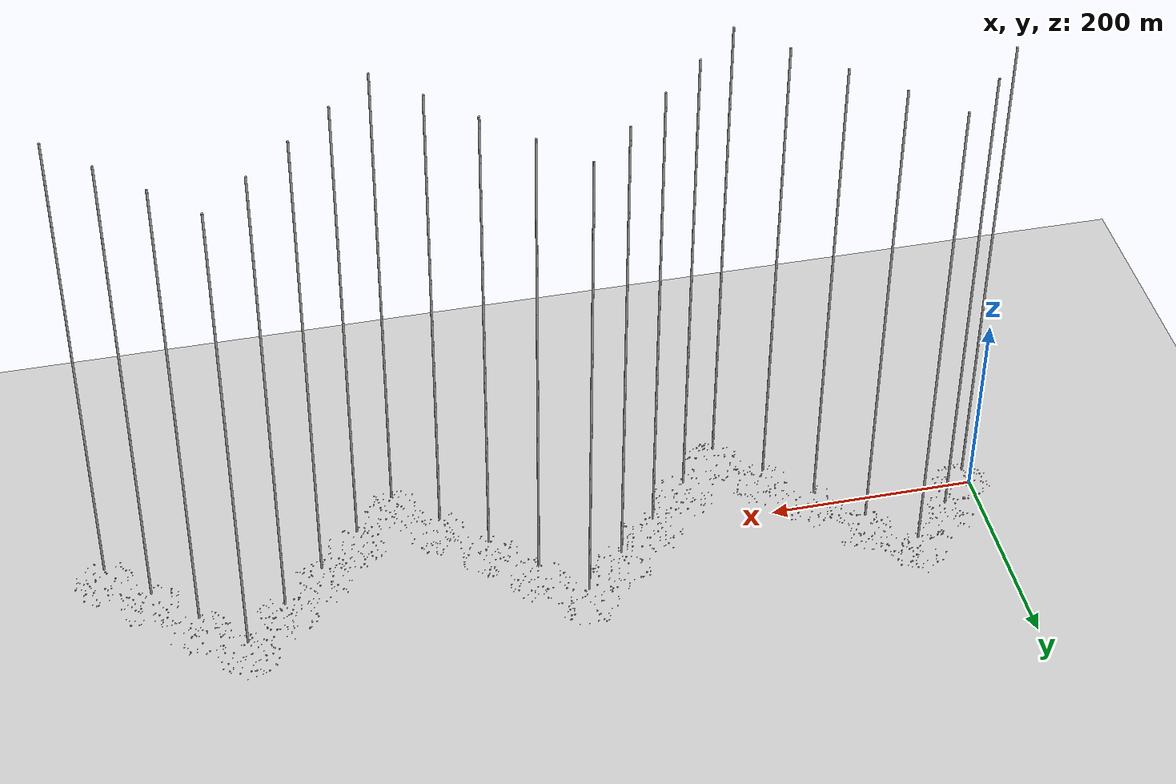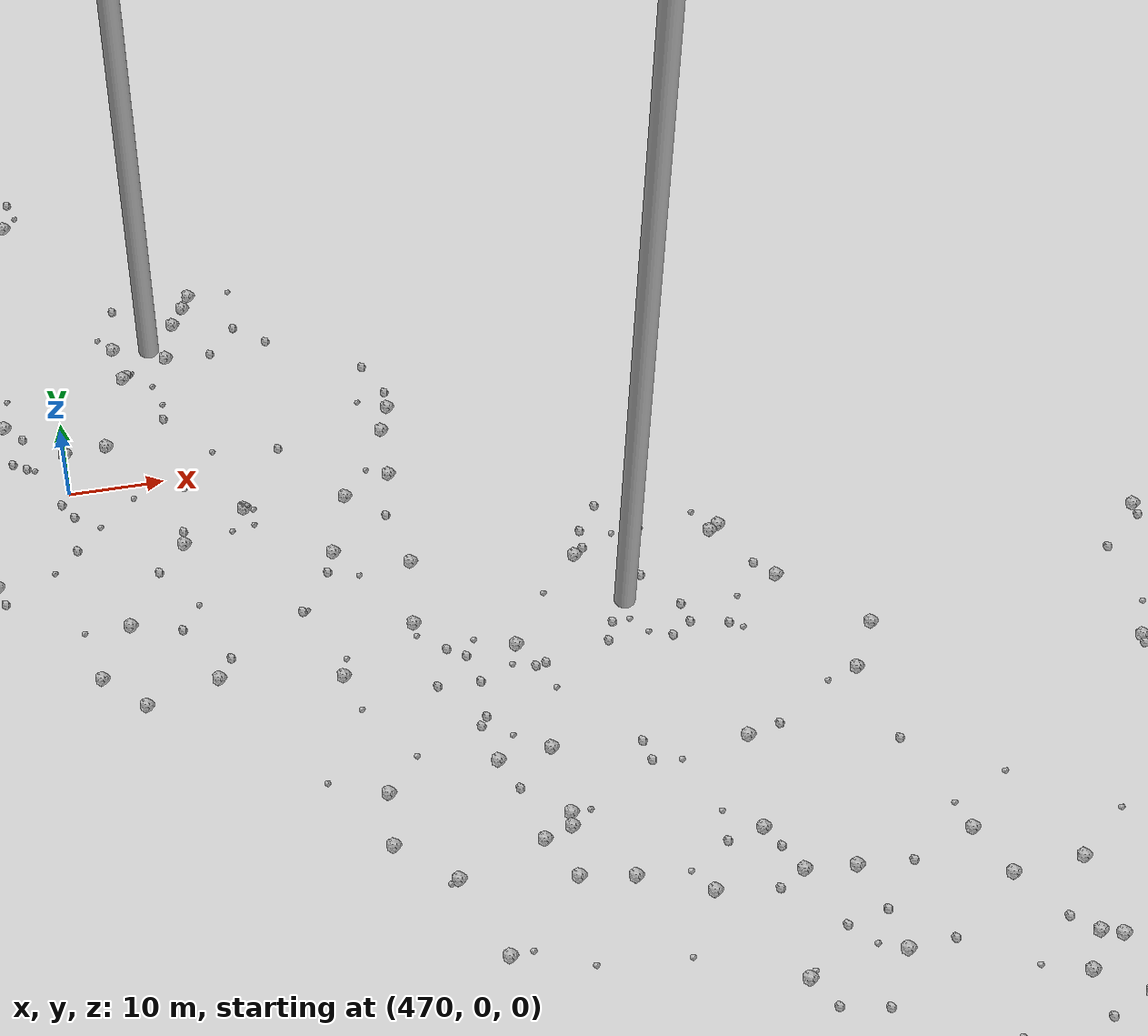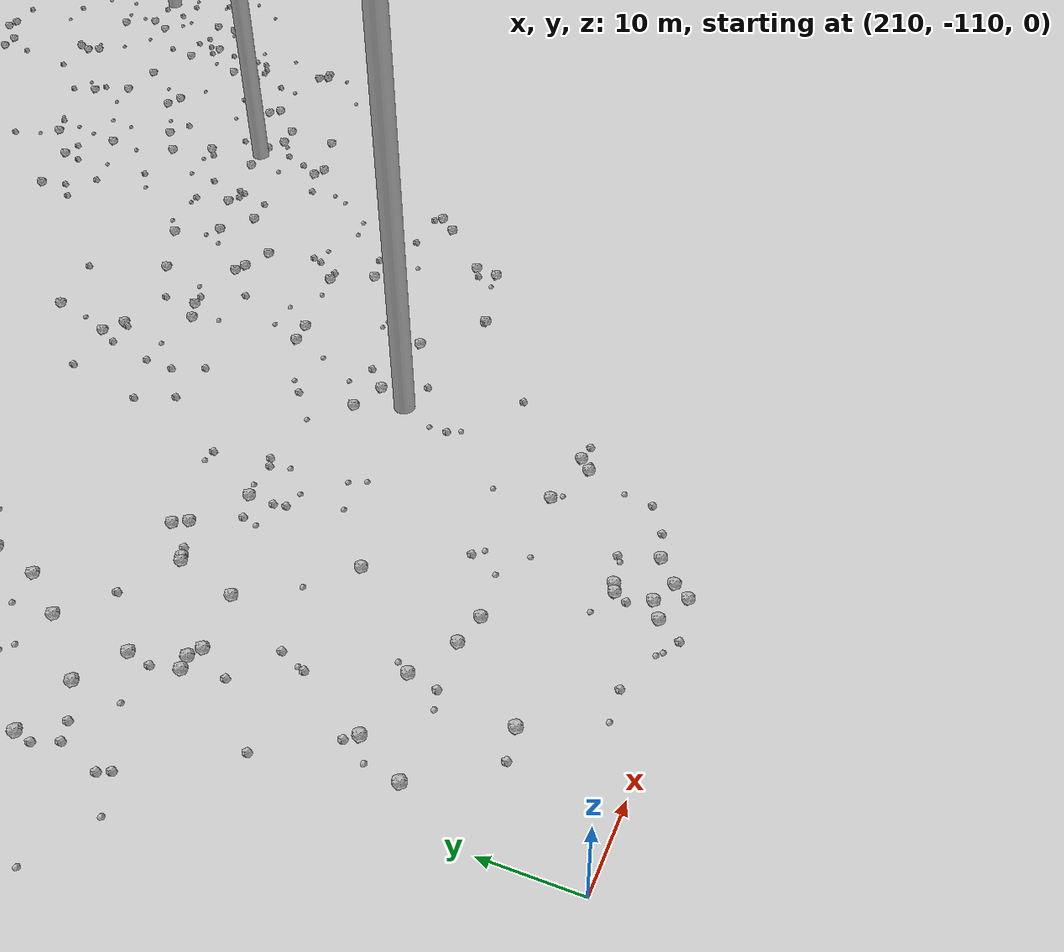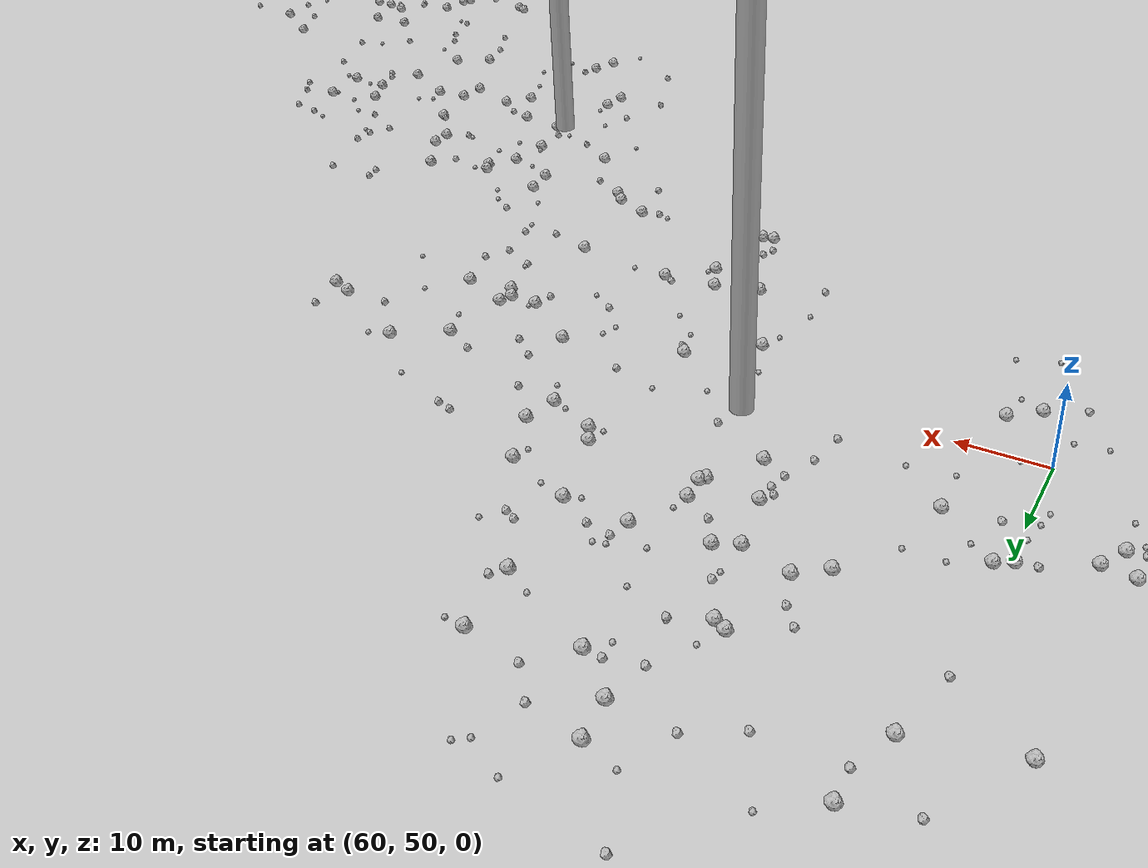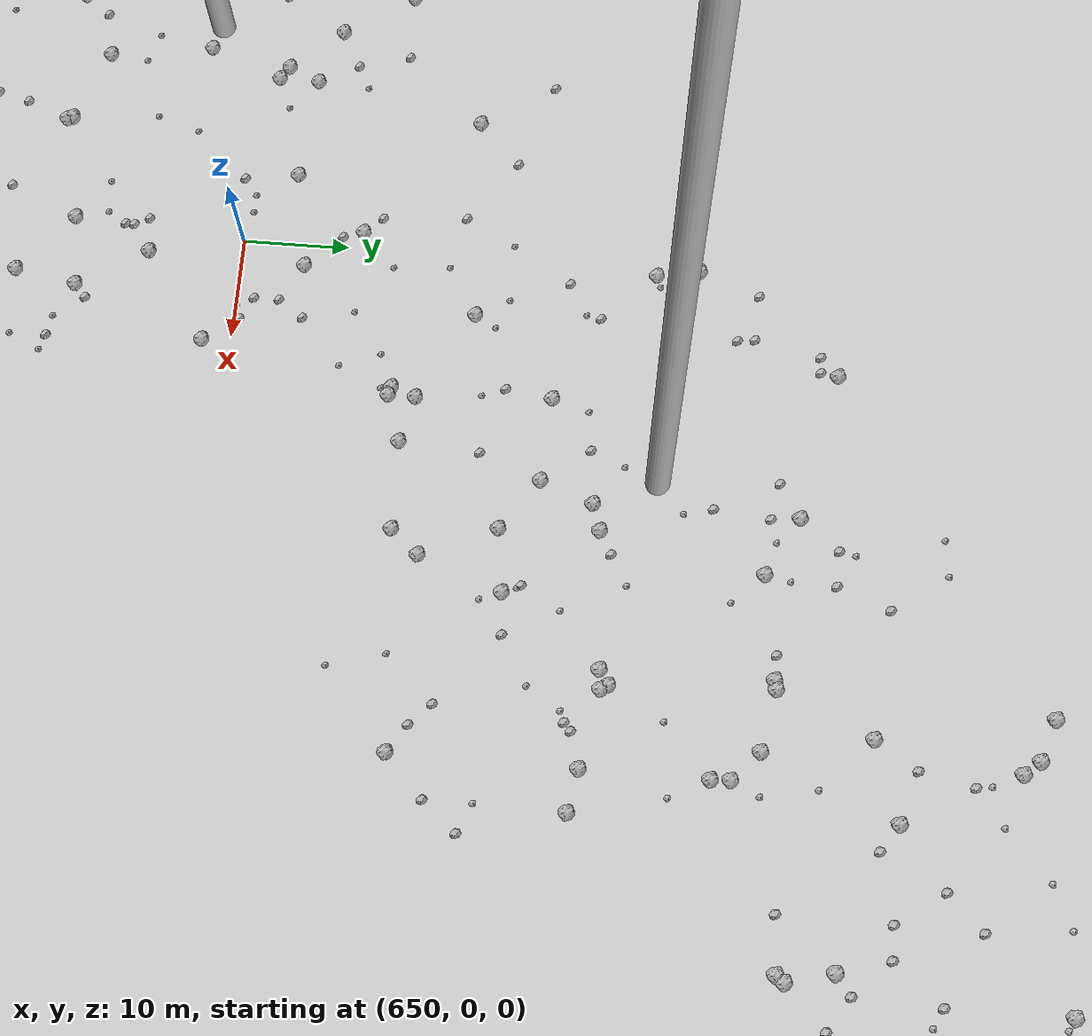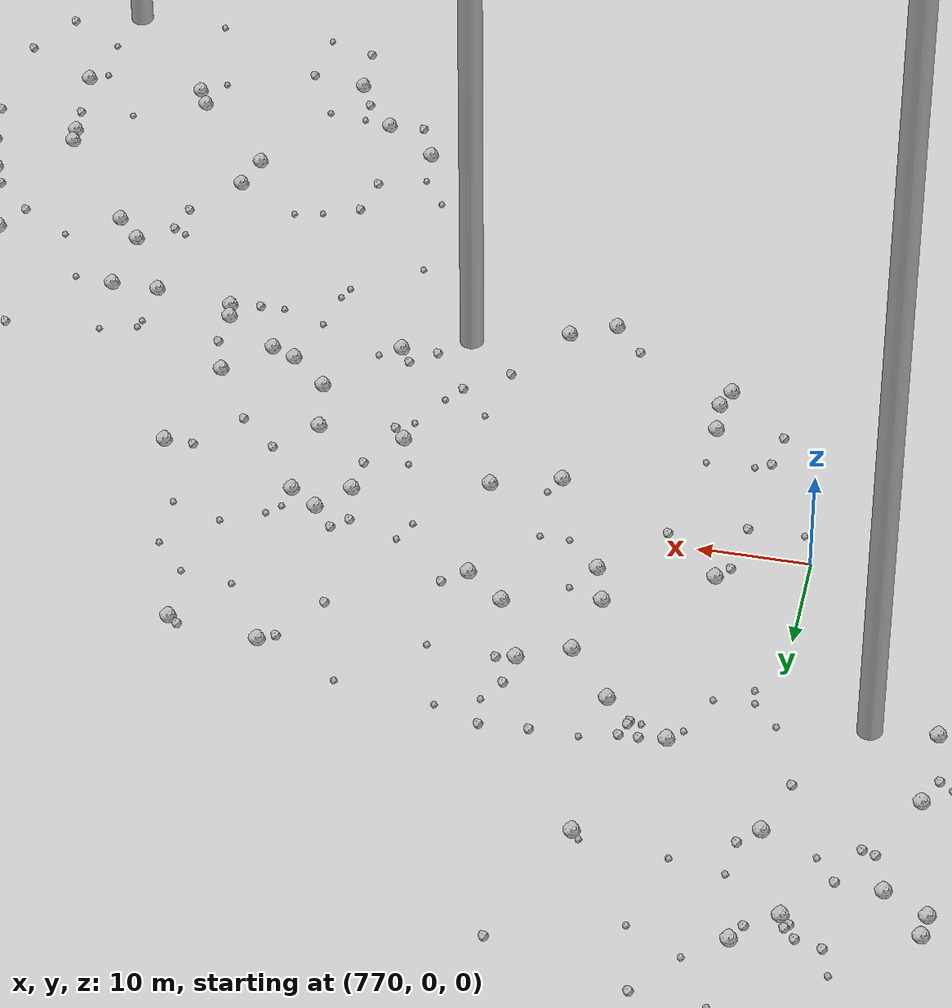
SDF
<sdf version="1.6">
 <world name="default">
  <include><uri>model://custom_ground</uri></include>
  <include><uri>model://sun</uri></include>
  <spherical_coordinates>
   <surface_model>EARTH_WGS84</surface_model>
   <latitude_deg>38.161479</latitude_deg>
   <longitude_deg>-122.454630</longitude_deg>
   <elevation>488.0</elevation>
   <heading_deg>90</heading_deg>
  </spherical_coordinates>
  <model name="rock1_0_0">
   <include><uri>model://rock1</uri><pose>33.18843018880962 -6.209308361919689 0.5 0 0 0</pose></include>
  </model>
  <model name="rock1_0_1">
   <include><uri>model://rock1</uri><pose>-13.818226750728527 -14.922664560404023 0.5 0 0 0</pose></include>
  </model>
  <model name="rock1_0_2">
   <include><uri>model://rock1</uri><pose>-8.044625321213648 -19.853205451162633 0.5 0 0 0</pose></include>
  </model>
  <model name="rock1_0_3">
   <include><uri>model://rock1</uri><pose>33.545585316809756 -12.24058555884341 0.5 0 0 0</pose></include>
  </model>
  <model name="rock1_0_4">
   <include><uri>model://rock1</uri><pose>17.066569713132658 -25.588061738076398 0.5 0 0 0</pose></include>
  </model>
  <model name="rock1_0_5">
   <include><uri>model://rock1</uri><pose>12.984274369637106 20.33690470726667 0.5 0 0 0</pose></include>
  </model>
  <model name="rock1_0_6">
   <include><uri>model://rock1</uri><pose>7.7945497626025855 -24.1708309257357 0.5 0 0 0</pose></include>
  </model>
  <model name="rock1_0_7">
   <include><uri>model://rock1</uri><pose>-8.217192282536065 -11.88883489107561 0.5 0 0 0</pose></include>
  </model>
  <model name="rock1_0_8">
   <include><uri>model://rock1</uri><pose>-13.917742807400426 -10.323790409336212 0.5 0 0 0</pose></include>
  </model>
  <model name="rock1_0_9">
   <include><uri>model://rock1</uri><pose>0.2561935281859036 27.315428272231358 0.5 0 0 0</pose></include>
  </model>
  <model name="rock1_0_10">
   <include><uri>model://rock1</uri><pose>23.825086590238556 11.756661908801227 0.5 0 0 0</pose></include>
  </model>
  <model name="rock1_0_11">
   <include><uri>model://rock1</uri><pose>11.50910151762195 21.010256561556027 0.5 0 0 0</pose></include>
  </model>
  <model name="rock1_0_12">
   <include><uri>model://rock1</uri><pose>-11.477563574429151 0.7142527435372088 0.5 0 0 0</pose></include>
  </model>
  <model name="rock1_0_13">
   <include><uri>model://rock1</uri><pose>8.041660791639384 20.81336013459042 0.5 0 0 0</pose></include>
  </model>
  <model name="rock1_0_14">
   <include><uri>model://rock1</uri><pose>32.638299697821296 5.668421329222873 0.5 0 0 0</pose></include>
  </model>
  <model name="rock1_0_15">
   <include><uri>model://rock1</uri><pose>-9.190683344652735 -17.552459785783704 0.5 0 0 0</pose></include>
  </model>
  <model name="rock1_0_16">
   <include><uri>model://rock1</uri><pose>-6.0270720531272985 -1.6813787993681792 0.5 0 0 0</pose></include>
  </model>
  <model name="rock1_0_17">
   <include><uri>model://rock1</uri><pose>27.09786636989797 -3.4538999677737223 0.5 0 0 0</pose></include>
  </model>
  <model name="rock1_0_18">
   <include><uri>model://rock1</uri><pose>4.229681809280862 2.9970650451227243 0.5 0 0 0</pose></include>
  </model>
  <model name="rock1_0_19">
   <include><uri>model://rock1</uri><pose>28.14985920143532 -13.490155751692654 0.5 0 0 0</pose></include>
  </model>
  <model name="rock1_0_20">
   <include><uri>model://rock1</uri><pose>-4.307919778452312 16.973841115639964 0.5 0 0 0</pose></include>
  </model>
  <model name="rock1_0_21">
   <include><uri>model://rock1</uri><pose>-13.02424937628475 2.430750445530535 0.5 0 0 0</pose></include>
  </model>
  <model name="rock1_0_22">
   <include><uri>model://rock1</uri><pose>11.590985986883602 19.631443638194156 0.5 0 0 0</pose></include>
  </model>
  <model name="rock1_0_23">
   <include><uri>model://rock1</uri><pose>1.883814013769399 -10.089778168220164 0.5 0 0 0</pose></include>
  </model>
  <model name="rock1_0_24">
   <include><uri>model://rock1</uri><pose>-3.561392172756907 -4.074029105330883 0.5 0 0 0</pose></include>
  </model>
  <model name="rock1_0_25">
   <include><uri>model://rock1</uri><pose>12.63543362349894 19.28834326476462 0.5 0 0 0</pose></include>
  </model>
  <model name="rock1_0_26">
   <include><uri>model://rock1</uri><pose>2.1100229102322743 -21.015520113940834 0.5 0 0 0</pose></include>
  </model>
  <model name="rock2_0_0">
   <include><uri>model://rock2</uri><pose>7.571767823053058 -26.918647552295052 0.3 0 0 0</pose></include>
  </model>
  <model name="rock2_0_1">
   <include><uri>model://rock2</uri><pose>-10.456085622241782 10.111228250264816 0.3 0 0 0</pose></include>
  </model>
  <model name="rock2_0_2">
   <include><uri>model://rock2</uri><pose>32.32982325989031 19.704424239629446 0.3 0 0 0</pose></include>
  </model>
  <model name="rock2_0_3">
   <include><uri>model://rock2</uri><pose>7.03157017586032 17.34447872069707 0.3 0 0 0</pose></include>
  </model>
  <model name="rock2_0_4">
   <include><uri>model://rock2</uri><pose>3.7250186324969157 -26.91922695886578 0.3 0 0 0</pose></include>
  </model>
  <model name="rock2_0_5">
   <include><uri>model://rock2</uri><pose>-10.650499630868095 -10.183060649703783 0.3 0 0 0</pose></include>
  </model>
  <model name="rock2_0_6">
   <include><uri>model://rock2</uri><pose>0.8705358546260129 -7.888187187701298 0.3 0 0 0</pose></include>
  </model>
  <model name="rock2_0_7">
   <include><uri>model://rock2</uri><pose>-0.041175397187668494 27.74520542396214 0.3 0 0 0</pose></include>
  </model>
  <model name="rock2_0_8">
   <include><uri>model://rock2</uri><pose>-8.836417397193665 15.272904537423713 0.3 0 0 0</pose></include>
  </model>
  <model name="rock2_0_9">
   <include><uri>model://rock2</uri><pose>20.766179338386117 -22.69681398126508 0.3 0 0 0</pose></include>
  </model>
  <model name="rock2_0_10">
   <include><uri>model://rock2</uri><pose>-0.6254044997881927 -14.559732879354058 0.3 0 0 0</pose></include>
  </model>
  <model name="rock2_0_11">
   <include><uri>model://rock2</uri><pose>31.188775450730766 17.376196531141353 0.3 0 0 0</pose></include>
  </model>
  <model name="rock2_0_12">
   <include><uri>model://rock2</uri><pose>24.063502566114202 -23.6152510549266 0.3 0 0 0</pose></include>
  </model>
  <model name="rock2_0_13">
   <include><uri>model://rock2</uri><pose>7.208458075998767 -23.364010192535005 0.3 0 0 0</pose></include>
  </model>
  <model name="rock2_0_14">
   <include><uri>model://rock2</uri><pose>27.712803851447397 -1.3602456941497891 0.3 0 0 0</pose></include>
  </model>
  <model name="rock2_0_15">
   <include><uri>model://rock2</uri><pose>17.423012207498807 -10.396868902778827 0.3 0 0 0</pose></include>
  </model>
  <model name="rock2_0_16">
   <include><uri>model://rock2</uri><pose>-1.8999836722767895 -4.824551277751048 0.3 0 0 0</pose></include>
  </model>
  <model name="rock2_0_17">
   <include><uri>model://rock2</uri><pose>20.463846874040115 -10.059039928782177 0.3 0 0 0</pose></include>
  </model>
  <model name="rock2_0_18">
   <include><uri>model://rock2</uri><pose>6.868870158689148 -7.530342257985222 0.3 0 0 0</pose></include>
  </model>
  <model name="rock2_0_19">
   <include><uri>model://rock2</uri><pose>20.35603481580724 4.537980738488827 0.3 0 0 0</pose></include>
  </model>
  <model name="rock2_0_20">
   <include><uri>model://rock2</uri><pose>26.836760503178382 -5.747236362371915 0.3 0 0 0</pose></include>
  </model>
  <model name="rock2_0_21">
   <include><uri>model://rock2</uri><pose>-14.854907927493429 13.279849013335522 0.3 0 0 0</pose></include>
  </model>
  <model name="rock2_0_22">
   <include><uri>model://rock2</uri><pose>-6.170380772417321 -15.463763879840544 0.3 0 0 0</pose></include>
  </model>
  <model name="rock2_0_23">
   <include><uri>model://rock2</uri><pose>-13.642323132002709 -9.773403739300335 0.3 0 0 0</pose></include>
  </model>
  <model name="rock2_0_24">
   <include><uri>model://rock2</uri><pose>-16.77875984917311 1.4254209667246869 0.3 0 0 0</pose></include>
  </model>
  <model name="rock2_0_25">
   <include><uri>model://rock2</uri><pose>-17.995424514960916 -9.596107025137062 0.3 0 0 0</pose></include>
  </model>
  <model name="rock2_0_26">
   <include><uri>model://rock2</uri><pose>24.258501213731485 -22.13357977781184 0.3 0 0 0</pose></include>
  </model>
  <model name="rock3_0_0">
   <include><uri>model://rock3</uri><pose>24.871913850439007 16.879472932919747 0.2 0 0 0</pose></include>
  </model>
  <model name="rock3_0_1">
   <include><uri>model://rock3</uri><pose>-4.177287822810936 -5.400244271432932 0.2 0 0 0</pose></include>
  </model>
  <model name="rock3_0_2">
   <include><uri>model://rock3</uri><pose>31.329949136679915 -16.61881772879588 0.2 0 0 0</pose></include>
  </model>
  <model name="rock3_0_3">
   <include><uri>model://rock3</uri><pose>14.875583323672025 28.490900848697585 0.2 0 0 0</pose></include>
  </model>
  <model name="rock3_0_4">
   <include><uri>model://rock3</uri><pose>-16.04861849649989 5.57630932477619 0.2 0 0 0</pose></include>
  </model>
  <model name="rock3_0_5">
   <include><uri>model://rock3</uri><pose>24.476492327686024 -9.952902431699723 0.2 0 0 0</pose></include>
  </model>
  <model name="rock3_0_6">
   <include><uri>model://rock3</uri><pose>-14.43925178503147 -6.041487707760197 0.2 0 0 0</pose></include>
  </model>
  <model name="rock3_0_7">
   <include><uri>model://rock3</uri><pose>-7.2882606303831174 -20.278748816978478 0.2 0 0 0</pose></include>
  </model>
  <model name="rock3_0_8">
   <include><uri>model://rock3</uri><pose>21.28753471096143 -13.019635894882637 0.2 0 0 0</pose></include>
  </model>
  <model name="rock3_0_9">
   <include><uri>model://rock3</uri><pose>14.461232884838111 -2.0836294785516607 0.2 0 0 0</pose></include>
  </model>
  <model name="rock3_0_10">
   <include><uri>model://rock3</uri><pose>-4.124668176494957 -21.664299803464353 0.2 0 0 0</pose></include>
  </model>
  <model name="rock3_0_11">
   <include><uri>model://rock3</uri><pose>-17.28555595973846 -11.103253528767475 0.2 0 0 0</pose></include>
  </model>
  <model name="rock3_0_12">
   <include><uri>model://rock3</uri><pose>16.54708249132357 -23.265345080588407 0.2 0 0 0</pose></include>
  </model>
  <model name="rock3_0_13">
   <include><uri>model://rock3</uri><pose>-4.958661949135816 -7.346405299673727 0.2 0 0 0</pose></include>
  </model>
  <model name="rock3_0_14">
   <include><uri>model://rock3</uri><pose>-17.77494374146558 8.43589524086407 0.2 0 0 0</pose></include>
  </model>
  <model name="rock3_0_15">
   <include><uri>model://rock3</uri><pose>6.745071481255113 8.334799913770539 0.2 0 0 0</pose></include>
  </model>
  <model name="rock3_0_16">
   <include><uri>model://rock3</uri><pose>34.69820215818299 -13.707795151709966 0.2 0 0 0</pose></include>
  </model>
  <model name="rock3_0_17">
   <include><uri>model://rock3</uri><pose>-11.581954887883485 -17.06242761922038 0.2 0 0 0</pose></include>
  </model>
  <model name="rock3_0_18">
   <include><uri>model://rock3</uri><pose>33.40918393283005 0.9009308756099301 0.2 0 0 0</pose></include>
  </model>
  <model name="rock3_0_19">
   <include><uri>model://rock3</uri><pose>-5.213474100517354 11.146969329536077 0.2 0 0 0</pose></include>
  </model>
  <model name="rock3_0_20">
   <include><uri>model://rock3</uri><pose>16.210275598789195 20.933466158084677 0.2 0 0 0</pose></include>
  </model>
  <model name="rock3_0_21">
   <include><uri>model://rock3</uri><pose>0.2951420281136379 -17.367872126715582 0.2 0 0 0</pose></include>
  </model>
  <model name="rock3_0_22">
   <include><uri>model://rock3</uri><pose>22.772019745854443 10.344828872805657 0.2 0 0 0</pose></include>
  </model>
  <model name="rock3_0_23">
   <include><uri>model://rock3</uri><pose>-14.116240596173919 -4.728429510081739 0.2 0 0 0</pose></include>
  </model>
  <model name="rock3_0_24">
   <include><uri>model://rock3</uri><pose>19.984020916166827 -12.29631711045257 0.2 0 0 0</pose></include>
  </model>
  <model name="rock3_0_25">
   <include><uri>model://rock3</uri><pose>-3.080343736355431 2.4093743786017754 0.2 0 0 0</pose></include>
  </model>
  <model name="rock3_0_26">
   <include><uri>model://rock3</uri><pose>7.658455452811836 -26.605896436617943 0.2 0 0 0</pose></include>
  </model>
  <model name="rock1_1_0">
   <include><uri>model://rock1</uri><pose>23.984710173195456 42.53382908354744 0.5 0 0 0</pose></include>
  </model>
  <model name="rock1_1_1">
   <include><uri>model://rock1</uri><pose>23.09436479974548 25.112064197767843 0.5 0 0 0</pose></include>
  </model>
  <model name="rock1_1_2">
   <include><uri>model://rock1</uri><pose>35.15149262200011 29.68842363185065 0.5 0 0 0</pose></include>
  </model>
  <model name="rock1_1_3">
   <include><uri>model://rock1</uri><pose>46.04167259209208 59.471917591840366 0.5 0 0 0</pose></include>
  </model>
  <model name="rock1_1_4">
   <include><uri>model://rock1</uri><pose>48.888404715821125 24.347766042577625 0.5 0 0 0</pose></include>
  </model>
  <model name="rock1_1_5">
   <include><uri>model://rock1</uri><pose>47.06192652782412 57.27263926905883 0.5 0 0 0</pose></include>
  </model>
  <model name="rock1_1_6">
   <include><uri>model://rock1</uri><pose>52.31854266877393 39.21192405362453 0.5 0 0 0</pose></include>
  </model>
  <model name="rock1_1_7">
   <include><uri>model://rock1</uri><pose>45.82593597659024 26.311730800441943 0.5 0 0 0</pose></include>
  </model>
  <model name="rock1_1_8">
   <include><uri>model://rock1</uri><pose>22.3684228491546 18.944287444508035 0.5 0 0 0</pose></include>
  </model>
  <model name="rock1_1_9">
   <include><uri>model://rock1</uri><pose>43.61038370758515 12.89670037436154 0.5 0 0 0</pose></include>
  </model>
  <model name="rock1_1_10">
   <include><uri>model://rock1</uri><pose>46.60871648896365 40.504888937627214 0.5 0 0 0</pose></include>
  </model>
  <model name="rock1_1_11">
   <include><uri>model://rock1</uri><pose>51.01042715041642 59.39091556478729 0.5 0 0 0</pose></include>
  </model>
  <model name="rock1_1_12">
   <include><uri>model://rock1</uri><pose>15.63369200435906 40.69824615133079 0.5 0 0 0</pose></include>
  </model>
  <model name="rock1_1_13">
   <include><uri>model://rock1</uri><pose>52.684797530881255 62.23166200457498 0.5 0 0 0</pose></include>
  </model>
  <model name="rock1_1_14">
   <include><uri>model://rock1</uri><pose>23.588484435296007 53.504026583386434 0.5 0 0 0</pose></include>
  </model>
  <model name="rock1_1_15">
   <include><uri>model://rock1</uri><pose>27.88703852532552 41.5412536290558 0.5 0 0 0</pose></include>
  </model>
  <model name="rock1_1_16">
   <include><uri>model://rock1</uri><pose>63.28717813811766 41.327013201264 0.5 0 0 0</pose></include>
  </model>
  <model name="rock1_1_17">
   <include><uri>model://rock1</uri><pose>47.370839204548 61.28326101680537 0.5 0 0 0</pose></include>
  </model>
  <model name="rock1_1_18">
   <include><uri>model://rock1</uri><pose>10.905343855411324 43.15546751776782 0.5 0 0 0</pose></include>
  </model>
  <model name="rock1_1_19">
   <include><uri>model://rock1</uri><pose>41.20600437113509 69.26276395237879 0.5 0 0 0</pose></include>
  </model>
  <model name="rock1_1_20">
   <include><uri>model://rock1</uri><pose>20.40847978618836 41.86908362039016 0.5 0 0 0</pose></include>
  </model>
  <model name="rock1_1_21">
   <include><uri>model://rock1</uri><pose>48.760319411488005 34.17107100048959 0.5 0 0 0</pose></include>
  </model>
  <model name="rock1_1_22">
   <include><uri>model://rock1</uri><pose>66.5021443779664 43.7655438868015 0.5 0 0 0</pose></include>
  </model>
  <model name="rock1_1_23">
   <include><uri>model://rock1</uri><pose>19.710383710248625 39.15990598769358 0.5 0 0 0</pose></include>
  </model>
  <model name="rock1_1_24">
   <include><uri>model://rock1</uri><pose>49.328218500312445 62.65715810037003 0.5 0 0 0</pose></include>
  </model>
  <model name="rock1_1_25">
   <include><uri>model://rock1</uri><pose>18.842616388785398 20.540387036831515 0.5 0 0 0</pose></include>
  </model>
  <model name="rock1_1_26">
   <include><uri>model://rock1</uri><pose>38.461029460107326 24.488953215263518 0.5 0 0 0</pose></include>
  </model>
  <model name="rock2_1_0">
   <include><uri>model://rock2</uri><pose>29.96221639626598 27.427036795244216 0.3 0 0 0</pose></include>
  </model>
  <model name="rock2_1_1">
   <include><uri>model://rock2</uri><pose>51.84191743860614 31.94001539640031 0.3 0 0 0</pose></include>
  </model>
  <model name="rock2_1_2">
   <include><uri>model://rock2</uri><pose>29.848347164098556 54.970796681234134 0.3 0 0 0</pose></include>
  </model>
  <model name="rock2_1_3">
   <include><uri>model://rock2</uri><pose>24.486636420631104 57.98887027856421 0.3 0 0 0</pose></include>
  </model>
  <model name="rock2_1_4">
   <include><uri>model://rock2</uri><pose>30.699926586615515 44.8727979658556 0.3 0 0 0</pose></include>
  </model>
  <model name="rock2_1_5">
   <include><uri>model://rock2</uri><pose>44.67248055789073 67.56453590548747 0.3 0 0 0</pose></include>
  </model>
  <model name="rock2_1_6">
   <include><uri>model://rock2</uri><pose>21.31269734386916 35.63004020146279 0.3 0 0 0</pose></include>
  </model>
  <model name="rock2_1_7">
   <include><uri>model://rock2</uri><pose>40.602042526303066 33.88916967499574 0.3 0 0 0</pose></include>
  </model>
  <model name="rock2_1_8">
   <include><uri>model://rock2</uri><pose>25.251461098575188 15.17604985990863 0.3 0 0 0</pose></include>
  </model>
  <model name="rock2_1_9">
   <include><uri>model://rock2</uri><pose>47.47305731100246 39.002453937740896 0.3 0 0 0</pose></include>
  </model>
  <model name="rock2_1_10">
   <include><uri>model://rock2</uri><pose>24.822540012804737 37.75525741979181 0.3 0 0 0</pose></include>
  </model>
  <model name="rock2_1_11">
   <include><uri>model://rock2</uri><pose>49.17610483497126 20.281100237860514 0.3 0 0 0</pose></include>
  </model>
  <model name="rock2_1_12">
   <include><uri>model://rock2</uri><pose>27.984906365962573 33.45344052053844 0.3 0 0 0</pose></include>
  </model>
  <model name="rock2_1_13">
   <include><uri>model://rock2</uri><pose>35.31194481299388 40.57972666663045 0.3 0 0 0</pose></include>
  </model>
  <model name="rock2_1_14">
   <include><uri>model://rock2</uri><pose>49.102907714608186 59.17350841935478 0.3 0 0 0</pose></include>
  </model>
  <model name="rock2_1_15">
   <include><uri>model://rock2</uri><pose>46.96905201155082 57.24436039317939 0.3 0 0 0</pose></include>
  </model>
  <model name="rock2_1_16">
   <include><uri>model://rock2</uri><pose>43.985380738741966 66.11380985098776 0.3 0 0 0</pose></include>
  </model>
  <model name="rock2_1_17">
   <include><uri>model://rock2</uri><pose>22.203893359400798 41.537961911380975 0.3 0 0 0</pose></include>
  </model>
  <model name="rock2_1_18">
   <include><uri>model://rock2</uri><pose>26.60539261085561 52.72072752536871 0.3 0 0 0</pose></include>
  </model>
  <model name="rock2_1_19">
   <include><uri>model://rock2</uri><pose>62.177111095693206 60.20073243722402 0.3 0 0 0</pose></include>
  </model>
  <model name="rock2_1_20">
   <include><uri>model://rock2</uri><pose>47.451039956934686 27.814505859364395 0.3 0 0 0</pose></include>
  </model>
  <model name="rock2_1_21">
   <include><uri>model://rock2</uri><pose>24.37317626672689 31.44104461122067 0.3 0 0 0</pose></include>
  </model>
  <model name="rock2_1_22">
   <include><uri>model://rock2</uri><pose>19.328815518581703 58.40262292915121 0.3 0 0 0</pose></include>
  </model>
  <model name="rock2_1_23">
   <include><uri>model://rock2</uri><pose>58.98731238219097 39.25513716164913 0.3 0 0 0</pose></include>
  </model>
  <model name="rock2_1_24">
   <include><uri>model://rock2</uri><pose>37.47631308230413 12.600295102763425 0.3 0 0 0</pose></include>
  </model>
  <model name="rock2_1_25">
   <include><uri>model://rock2</uri><pose>44.91830661707329 15.916554551789604 0.3 0 0 0</pose></include>
  </model>
  <model name="rock2_1_26">
   <include><uri>model://rock2</uri><pose>47.4396312602696 50.008143544643524 0.3 0 0 0</pose></include>
  </model>
  <model name="rock3_1_0">
   <include><uri>model://rock3</uri><pose>36.771113042230056 69.80414757044375 0.2 0 0 0</pose></include>
  </model>
  <model name="rock3_1_1">
   <include><uri>model://rock3</uri><pose>44.88682777177071 23.0842399520575 0.2 0 0 0</pose></include>
  </model>
  <model name="rock3_1_2">
   <include><uri>model://rock3</uri><pose>15.936746646583659 40.42938445168201 0.2 0 0 0</pose></include>
  </model>
  <model name="rock3_1_3">
   <include><uri>model://rock3</uri><pose>63.071016203561136 50.379255870415086 0.2 0 0 0</pose></include>
  </model>
  <model name="rock3_1_4">
   <include><uri>model://rock3</uri><pose>68.41425402169972 32.89286999149102 0.2 0 0 0</pose></include>
  </model>
  <model name="rock3_1_5">
   <include><uri>model://rock3</uri><pose>49.476134378199305 57.82306545991845 0.2 0 0 0</pose></include>
  </model>
  <model name="rock3_1_6">
   <include><uri>model://rock3</uri><pose>59.082454692413755 45.230433737241476 0.2 0 0 0</pose></include>
  </model>
  <model name="rock3_1_7">
   <include><uri>model://rock3</uri><pose>65.84575106703201 39.97641412486438 0.2 0 0 0</pose></include>
  </model>
  <model name="rock3_1_8">
   <include><uri>model://rock3</uri><pose>48.736651542199056 34.157903605053114 0.2 0 0 0</pose></include>
  </model>
  <model name="rock3_1_9">
   <include><uri>model://rock3</uri><pose>42.75701407526999 45.78193889978084 0.2 0 0 0</pose></include>
  </model>
  <model name="rock3_1_10">
   <include><uri>model://rock3</uri><pose>51.03743014672687 54.88060418163465 0.2 0 0 0</pose></include>
  </model>
  <model name="rock3_1_11">
   <include><uri>model://rock3</uri><pose>50.837979370741834 40.63025828213097 0.2 0 0 0</pose></include>
  </model>
  <model name="rock3_1_12">
   <include><uri>model://rock3</uri><pose>18.800594133570957 25.56279395470256 0.2 0 0 0</pose></include>
  </model>
  <model name="rock3_1_13">
   <include><uri>model://rock3</uri><pose>32.42482752175239 54.72993809049798 0.2 0 0 0</pose></include>
  </model>
  <model name="rock3_1_14">
   <include><uri>model://rock3</uri><pose>26.408509678668587 40.90702284670381 0.2 0 0 0</pose></include>
  </model>
  <model name="rock3_1_15">
   <include><uri>model://rock3</uri><pose>34.83381832459332 54.63730861804561 0.2 0 0 0</pose></include>
  </model>
  <model name="rock3_1_16">
   <include><uri>model://rock3</uri><pose>28.5442998503422 48.18317915086525 0.2 0 0 0</pose></include>
  </model>
  <model name="rock3_1_17">
   <include><uri>model://rock3</uri><pose>36.05465156695918 34.34474567108952 0.2 0 0 0</pose></include>
  </model>
  <model name="rock3_1_18">
   <include><uri>model://rock3</uri><pose>22.94314664354043 26.251284014796315 0.2 0 0 0</pose></include>
  </model>
  <model name="rock3_1_19">
   <include><uri>model://rock3</uri><pose>63.85473719111029 31.27624799220632 0.2 0 0 0</pose></include>
  </model>
  <model name="rock3_1_20">
   <include><uri>model://rock3</uri><pose>47.72557514188085 62.300141754763104 0.2 0 0 0</pose></include>
  </model>
  <model name="rock3_1_21">
   <include><uri>model://rock3</uri><pose>58.789567395955146 59.04451598563833 0.2 0 0 0</pose></include>
  </model>
  <model name="rock3_1_22">
   <include><uri>model://rock3</uri><pose>42.109852871989055 36.1401669620637 0.2 0 0 0</pose></include>
  </model>
  <model name="rock3_1_23">
   <include><uri>model://rock3</uri><pose>25.95891743940968 51.07132166348612 0.2 0 0 0</pose></include>
  </model>
  <model name="rock3_1_24">
   <include><uri>model://rock3</uri><pose>55.59164835949418 44.75421428733667 0.2 0 0 0</pose></include>
  </model>
  <model name="rock3_1_25">
   <include><uri>model://rock3</uri><pose>51.3972438778214 32.117847073122476 0.2 0 0 0</pose></include>
  </model>
  <model name="rock3_1_26">
   <include><uri>model://rock3</uri><pose>58.41635609116432 57.07575418441687 0.2 0 0 0</pose></include>
  </model>
  <model name="rock1_2_0">
   <include><uri>model://rock1</uri><pose>107.94450703773248 72.20828096778081 0.5 0 0 0</pose></include>
  </model>
  <model name="rock1_2_1">
   <include><uri>model://rock1</uri><pose>84.32160226534324 95.6554498979686 0.5 0 0 0</pose></include>
  </model>
  <model name="rock1_2_2">
   <include><uri>model://rock1</uri><pose>64.27666162626478 97.03200528014021 0.5 0 0 0</pose></include>
  </model>
  <model name="rock1_2_3">
   <include><uri>model://rock1</uri><pose>73.8266515115547 73.4051831843651 0.5 0 0 0</pose></include>
  </model>
  <model name="rock1_2_4">
   <include><uri>model://rock1</uri><pose>67.84653098962704 60.8977501770671 0.5 0 0 0</pose></include>
  </model>
  <model name="rock1_2_5">
   <include><uri>model://rock1</uri><pose>102.7313108901981 66.45844631635987 0.5 0 0 0</pose></include>
  </model>
  <model name="rock1_2_6">
   <include><uri>model://rock1</uri><pose>85.74011861394942 61.539598596388956 0.5 0 0 0</pose></include>
  </model>
  <model name="rock1_2_7">
   <include><uri>model://rock1</uri><pose>93.07042662767739 75.79570944766111 0.5 0 0 0</pose></include>
  </model>
  <model name="rock1_2_8">
   <include><uri>model://rock1</uri><pose>79.03627847929589 84.48468283826682 0.5 0 0 0</pose></include>
  </model>
  <model name="rock1_2_9">
   <include><uri>model://rock1</uri><pose>83.88359201573007 100.10592032559089 0.5 0 0 0</pose></include>
  </model>
  <model name="rock1_2_10">
   <include><uri>model://rock1</uri><pose>61.338592476449975 66.19660837098185 0.5 0 0 0</pose></include>
  </model>
  <model name="rock1_2_11">
   <include><uri>model://rock1</uri><pose>52.09212960337395 86.49865172900078 0.5 0 0 0</pose></include>
  </model>
  <model name="rock1_2_12">
   <include><uri>model://rock1</uri><pose>84.89268346296069 75.1055912505671 0.5 0 0 0</pose></include>
  </model>
  <model name="rock1_2_13">
   <include><uri>model://rock1</uri><pose>80.39573628777259 83.75810577370548 0.5 0 0 0</pose></include>
  </model>
  <model name="rock1_2_14">
   <include><uri>model://rock1</uri><pose>62.41999071377001 88.82514303873538 0.5 0 0 0</pose></include>
  </model>
  <model name="rock1_2_15">
   <include><uri>model://rock1</uri><pose>98.91853425904526 93.94430125529098 0.5 0 0 0</pose></include>
  </model>
  <model name="rock1_2_16">
   <include><uri>model://rock1</uri><pose>88.71339648229102 91.64089152320585 0.5 0 0 0</pose></include>
  </model>
  <model name="rock1_2_17">
   <include><uri>model://rock1</uri><pose>59.61035361630371 65.29979642168604 0.5 0 0 0</pose></include>
  </model>
  <model name="rock1_2_18">
   <include><uri>model://rock1</uri><pose>89.86632623970854 70.04073679726876 0.5 0 0 0</pose></include>
  </model>
  <model name="rock1_2_19">
   <include><uri>model://rock1</uri><pose>89.54221234009563 66.6901758098747 0.5 0 0 0</pose></include>
  </model>
  <model name="rock1_2_20">
   <include><uri>model://rock1</uri><pose>90.04594214890366 67.25950225048413 0.5 0 0 0</pose></include>
  </model>
  <model name="rock1_2_21">
   <include><uri>model://rock1</uri><pose>82.3936275066751 73.98854373919819 0.5 0 0 0</pose></include>
  </model>
  <model name="rock1_2_22">
   <include><uri>model://rock1</uri><pose>100.36590994600942 75.32927197427203 0.5 0 0 0</pose></include>
  </model>
  <model name="rock1_2_23">
   <include><uri>model://rock1</uri><pose>76.8909457381884 75.58131260774235 0.5 0 0 0</pose></include>
  </model>
  <model name="rock1_2_24">
   <include><uri>model://rock1</uri><pose>103.8150888799668 64.55602769977328 0.5 0 0 0</pose></include>
  </model>
  <model name="rock1_2_25">
   <include><uri>model://rock1</uri><pose>99.56283649603235 86.12757104666402 0.5 0 0 0</pose></include>
  </model>
  <model name="rock1_2_26">
   <include><uri>model://rock1</uri><pose>83.57110477525833 67.40160769480474 0.5 0 0 0</pose></include>
  </model>
  <model name="rock2_2_0">
   <include><uri>model://rock2</uri><pose>92.41500758734266 57.93640317782278 0.3 0 0 0</pose></include>
  </model>
  <model name="rock2_2_1">
   <include><uri>model://rock2</uri><pose>82.75893082306231 79.28245229980553 0.3 0 0 0</pose></include>
  </model>
  <model name="rock2_2_2">
   <include><uri>model://rock2</uri><pose>72.62674696480903 93.53788648207129 0.3 0 0 0</pose></include>
  </model>
  <model name="rock2_2_3">
   <include><uri>model://rock2</uri><pose>84.17508139049991 85.26886957969893 0.3 0 0 0</pose></include>
  </model>
  <model name="rock2_2_4">
   <include><uri>model://rock2</uri><pose>57.48653481736493 64.9513404528002 0.3 0 0 0</pose></include>
  </model>
  <model name="rock2_2_5">
   <include><uri>model://rock2</uri><pose>73.95537577889667 81.54821014434461 0.3 0 0 0</pose></include>
  </model>
  <model name="rock2_2_6">
   <include><uri>model://rock2</uri><pose>96.45831638328096 77.5629668876706 0.3 0 0 0</pose></include>
  </model>
  <model name="rock2_2_7">
   <include><uri>model://rock2</uri><pose>75.6066522666475 79.41023294861496 0.3 0 0 0</pose></include>
  </model>
  <model name="rock2_2_8">
   <include><uri>model://rock2</uri><pose>89.7613976422345 98.79113494225196 0.3 0 0 0</pose></include>
  </model>
  <model name="rock2_2_9">
   <include><uri>model://rock2</uri><pose>83.08774920560606 91.02637113011107 0.3 0 0 0</pose></include>
  </model>
  <model name="rock2_2_10">
   <include><uri>model://rock2</uri><pose>102.83146834325531 80.04784977649587 0.3 0 0 0</pose></include>
  </model>
  <model name="rock2_2_11">
   <include><uri>model://rock2</uri><pose>86.66761638656308 72.00784142426545 0.3 0 0 0</pose></include>
  </model>
  <model name="rock2_2_12">
   <include><uri>model://rock2</uri><pose>92.54156366108376 95.35896592184399 0.3 0 0 0</pose></include>
  </model>
  <model name="rock2_2_13">
   <include><uri>model://rock2</uri><pose>83.34136660447592 65.04415097616912 0.3 0 0 0</pose></include>
  </model>
  <model name="rock2_2_14">
   <include><uri>model://rock2</uri><pose>81.24601272869667 59.38739561725289 0.3 0 0 0</pose></include>
  </model>
  <model name="rock2_2_15">
   <include><uri>model://rock2</uri><pose>64.35159114590024 93.39862764771071 0.3 0 0 0</pose></include>
  </model>
  <model name="rock2_2_16">
   <include><uri>model://rock2</uri><pose>100.71762509400341 87.45101582945935 0.3 0 0 0</pose></include>
  </model>
  <model name="rock2_2_17">
   <include><uri>model://rock2</uri><pose>60.49274113846799 81.1082666608152 0.3 0 0 0</pose></include>
  </model>
  <model name="rock2_2_18">
   <include><uri>model://rock2</uri><pose>80.47928228047932 55.153345474550655 0.3 0 0 0</pose></include>
  </model>
  <model name="rock2_2_19">
   <include><uri>model://rock2</uri><pose>93.69617291786845 78.11755121375813 0.3 0 0 0</pose></include>
  </model>
  <model name="rock2_2_20">
   <include><uri>model://rock2</uri><pose>82.8578698586025 63.00386575872122 0.3 0 0 0</pose></include>
  </model>
  <model name="rock2_2_21">
   <include><uri>model://rock2</uri><pose>77.02993150429393 108.31267319387891 0.3 0 0 0</pose></include>
  </model>
  <model name="rock2_2_22">
   <include><uri>model://rock2</uri><pose>77.55319050180191 96.20620279676814 0.3 0 0 0</pose></include>
  </model>
  <model name="rock2_2_23">
   <include><uri>model://rock2</uri><pose>104.11341090881652 79.3540553128814 0.3 0 0 0</pose></include>
  </model>
  <model name="rock2_2_24">
   <include><uri>model://rock2</uri><pose>57.91018083481347 95.41468295854743 0.3 0 0 0</pose></include>
  </model>
  <model name="rock2_2_25">
   <include><uri>model://rock2</uri><pose>82.63926278673736 66.09911249871057 0.3 0 0 0</pose></include>
  </model>
  <model name="rock2_2_26">
   <include><uri>model://rock2</uri><pose>86.69456504907915 91.84458513201564 0.3 0 0 0</pose></include>
  </model>
  <model name="rock3_2_0">
   <include><uri>model://rock3</uri><pose>105.87280919610605 81.19203524113124 0.2 0 0 0</pose></include>
  </model>
  <model name="rock3_2_1">
   <include><uri>model://rock3</uri><pose>84.03955454353078 85.47467865425729 0.2 0 0 0</pose></include>
  </model>
  <model name="rock3_2_2">
   <include><uri>model://rock3</uri><pose>93.44187139202806 79.23423941690442 0.2 0 0 0</pose></include>
  </model>
  <model name="rock3_2_3">
   <include><uri>model://rock3</uri><pose>96.43000329852319 87.87693141839445 0.2 0 0 0</pose></include>
  </model>
  <model name="rock3_2_4">
   <include><uri>model://rock3</uri><pose>92.86792329828434 104.49718287554097 0.2 0 0 0</pose></include>
  </model>
  <model name="rock3_2_5">
   <include><uri>model://rock3</uri><pose>89.02150693674439 83.30738355032756 0.2 0 0 0</pose></include>
  </model>
  <model name="rock3_2_6">
   <include><uri>model://rock3</uri><pose>72.91892243692735 56.06379373035083 0.2 0 0 0</pose></include>
  </model>
  <model name="rock3_2_7">
   <include><uri>model://rock3</uri><pose>80.00274279457287 101.33924926078954 0.2 0 0 0</pose></include>
  </model>
  <model name="rock3_2_8">
   <include><uri>model://rock3</uri><pose>98.72509302547455 74.55624395358731 0.2 0 0 0</pose></include>
  </model>
  <model name="rock3_2_9">
   <include><uri>model://rock3</uri><pose>69.26850447822414 100.23799952875802 0.2 0 0 0</pose></include>
  </model>
  <model name="rock3_2_10">
   <include><uri>model://rock3</uri><pose>91.63427065981926 103.62022986539588 0.2 0 0 0</pose></include>
  </model>
  <model name="rock3_2_11">
   <include><uri>model://rock3</uri><pose>82.52300510001872 77.98858939408427 0.2 0 0 0</pose></include>
  </model>
  <model name="rock3_2_12">
   <include><uri>model://rock3</uri><pose>65.06479628784973 67.77227793138678 0.2 0 0 0</pose></include>
  </model>
  <model name="rock3_2_13">
   <include><uri>model://rock3</uri><pose>94.71005179961116 79.49871271812526 0.2 0 0 0</pose></include>
  </model>
  <model name="rock3_2_14">
   <include><uri>model://rock3</uri><pose>59.365006269944914 61.64262686381385 0.2 0 0 0</pose></include>
  </model>
  <model name="rock3_2_15">
   <include><uri>model://rock3</uri><pose>68.01241738659584 55.404903179249196 0.2 0 0 0</pose></include>
  </model>
  <model name="rock3_2_16">
   <include><uri>model://rock3</uri><pose>102.12568620790111 64.34729398365556 0.2 0 0 0</pose></include>
  </model>
  <model name="rock3_2_17">
   <include><uri>model://rock3</uri><pose>80.44704768372802 86.91107444513585 0.2 0 0 0</pose></include>
  </model>
  <model name="rock3_2_18">
   <include><uri>model://rock3</uri><pose>101.08148910756874 93.56211079927563 0.2 0 0 0</pose></include>
  </model>
  <model name="rock3_2_19">
   <include><uri>model://rock3</uri><pose>69.21433646942216 67.83042332860161 0.2 0 0 0</pose></include>
  </model>
  <model name="rock3_2_20">
   <include><uri>model://rock3</uri><pose>107.34274632574946 70.28196815693896 0.2 0 0 0</pose></include>
  </model>
  <model name="rock3_2_21">
   <include><uri>model://rock3</uri><pose>90.3203239204111 71.90668478388562 0.2 0 0 0</pose></include>
  </model>
  <model name="rock3_2_22">
   <include><uri>model://rock3</uri><pose>63.82275575955762 64.439027433764 0.2 0 0 0</pose></include>
  </model>
  <model name="rock3_2_23">
   <include><uri>model://rock3</uri><pose>86.83618240830988 89.79592811422856 0.2 0 0 0</pose></include>
  </model>
  <model name="rock3_2_24">
   <include><uri>model://rock3</uri><pose>87.6403849157947 105.9169870542659 0.2 0 0 0</pose></include>
  </model>
  <model name="rock3_2_25">
   <include><uri>model://rock3</uri><pose>89.83759573335587 78.08578498263887 0.2 0 0 0</pose></include>
  </model>
  <model name="rock3_2_26">
   <include><uri>model://rock3</uri><pose>103.38886812384116 74.26807727661158 0.2 0 0 0</pose></include>
  </model>
  <model name="rock1_3_0">
   <include><uri>model://rock1</uri><pose>97.40321404388965 39.370169131379676 0.5 0 0 0</pose></include>
  </model>
  <model name="rock1_3_1">
   <include><uri>model://rock1</uri><pose>109.30655771035345 62.16238432303779 0.5 0 0 0</pose></include>
  </model>
  <model name="rock1_3_2">
   <include><uri>model://rock1</uri><pose>110.99390103316992 33.873665092220705 0.5 0 0 0</pose></include>
  </model>
  <model name="rock1_3_3">
   <include><uri>model://rock1</uri><pose>131.3076981695207 45.08907190024925 0.5 0 0 0</pose></include>
  </model>
  <model name="rock1_3_4">
   <include><uri>model://rock1</uri><pose>104.71813150081144 33.3255215312235 0.5 0 0 0</pose></include>
  </model>
  <model name="rock1_3_5">
   <include><uri>model://rock1</uri><pose>126.60053436791554 17.345345532032844 0.5 0 0 0</pose></include>
  </model>
  <model name="rock1_3_6">
   <include><uri>model://rock1</uri><pose>121.48251727622797 46.29495759495259 0.5 0 0 0</pose></include>
  </model>
  <model name="rock1_3_7">
   <include><uri>model://rock1</uri><pose>145.18426886690204 52.66493408291181 0.5 0 0 0</pose></include>
  </model>
  <model name="rock1_3_8">
   <include><uri>model://rock1</uri><pose>94.32570439931723 42.75090668194718 0.5 0 0 0</pose></include>
  </model>
  <model name="rock1_3_9">
   <include><uri>model://rock1</uri><pose>142.6595189538505 53.72479749366995 0.5 0 0 0</pose></include>
  </model>
  <model name="rock1_3_10">
   <include><uri>model://rock1</uri><pose>99.46268238714453 31.927866830265582 0.5 0 0 0</pose></include>
  </model>
  <model name="rock1_3_11">
   <include><uri>model://rock1</uri><pose>103.06415613653137 19.679472505387356 0.5 0 0 0</pose></include>
  </model>
  <model name="rock1_3_12">
   <include><uri>model://rock1</uri><pose>138.0063655471861 17.10206440971117 0.5 0 0 0</pose></include>
  </model>
  <model name="rock1_3_13">
   <include><uri>model://rock1</uri><pose>114.8619938115519 51.270783109212786 0.5 0 0 0</pose></include>
  </model>
  <model name="rock1_3_14">
   <include><uri>model://rock1</uri><pose>125.8238694763669 44.6759386615479 0.5 0 0 0</pose></include>
  </model>
  <model name="rock1_3_15">
   <include><uri>model://rock1</uri><pose>106.25693809825714 29.71790031272356 0.5 0 0 0</pose></include>
  </model>
  <model name="rock1_3_16">
   <include><uri>model://rock1</uri><pose>125.51515430344045 47.62948739385488 0.5 0 0 0</pose></include>
  </model>
  <model name="rock1_3_17">
   <include><uri>model://rock1</uri><pose>137.6161067317003 20.856234984779253 0.5 0 0 0</pose></include>
  </model>
  <model name="rock1_3_18">
   <include><uri>model://rock1</uri><pose>124.85307409160194 46.088697719095684 0.5 0 0 0</pose></include>
  </model>
  <model name="rock1_3_19">
   <include><uri>model://rock1</uri><pose>125.31783933594008 18.809205070119408 0.5 0 0 0</pose></include>
  </model>
  <model name="rock1_3_20">
   <include><uri>model://rock1</uri><pose>101.39682490930562 47.85777788440853 0.5 0 0 0</pose></include>
  </model>
  <model name="rock1_3_21">
   <include><uri>model://rock1</uri><pose>110.38524284808932 65.92801997837132 0.5 0 0 0</pose></include>
  </model>
  <model name="rock1_3_22">
   <include><uri>model://rock1</uri><pose>121.18884873720543 20.767248516381855 0.5 0 0 0</pose></include>
  </model>
  <model name="rock1_3_23">
   <include><uri>model://rock1</uri><pose>123.06697657711484 32.262481304334216 0.5 0 0 0</pose></include>
  </model>
  <model name="rock1_3_24">
   <include><uri>model://rock1</uri><pose>104.45702009016667 19.93481365456092 0.5 0 0 0</pose></include>
  </model>
  <model name="rock1_3_25">
   <include><uri>model://rock1</uri><pose>126.8433297802668 55.63613555102133 0.5 0 0 0</pose></include>
  </model>
  <model name="rock1_3_26">
   <include><uri>model://rock1</uri><pose>132.59206152148977 59.10054977085927 0.5 0 0 0</pose></include>
  </model>
  <model name="rock2_3_0">
   <include><uri>model://rock2</uri><pose>106.52000229714127 53.847243551335815 0.3 0 0 0</pose></include>
  </model>
  <model name="rock2_3_1">
   <include><uri>model://rock2</uri><pose>122.18410182303343 14.198288058993123 0.3 0 0 0</pose></include>
  </model>
  <model name="rock2_3_2">
   <include><uri>model://rock2</uri><pose>102.57152591183949 23.889270229733555 0.3 0 0 0</pose></include>
  </model>
  <model name="rock2_3_3">
   <include><uri>model://rock2</uri><pose>130.59112377446286 15.094949057392807 0.3 0 0 0</pose></include>
  </model>
  <model name="rock2_3_4">
   <include><uri>model://rock2</uri><pose>118.91925141475554 20.179376241591694 0.3 0 0 0</pose></include>
  </model>
  <model name="rock2_3_5">
   <include><uri>model://rock2</uri><pose>131.0351938446589 36.865287525676415 0.3 0 0 0</pose></include>
  </model>
  <model name="rock2_3_6">
   <include><uri>model://rock2</uri><pose>102.17449389215676 46.66722253287853 0.3 0 0 0</pose></include>
  </model>
  <model name="rock2_3_7">
   <include><uri>model://rock2</uri><pose>127.21274506824217 38.76213715931458 0.3 0 0 0</pose></include>
  </model>
  <model name="rock2_3_8">
   <include><uri>model://rock2</uri><pose>113.36492406725279 43.27596789057909 0.3 0 0 0</pose></include>
  </model>
  <model name="rock2_3_9">
   <include><uri>model://rock2</uri><pose>116.3741308853817 55.867177517818654 0.3 0 0 0</pose></include>
  </model>
  <model name="rock2_3_10">
   <include><uri>model://rock2</uri><pose>92.35866431838055 28.941736779905717 0.3 0 0 0</pose></include>
  </model>
  <model name="rock2_3_11">
   <include><uri>model://rock2</uri><pose>101.89890593578379 46.85776449025198 0.3 0 0 0</pose></include>
  </model>
  <model name="rock2_3_12">
   <include><uri>model://rock2</uri><pose>132.81390211293407 39.49480828914203 0.3 0 0 0</pose></include>
  </model>
  <model name="rock2_3_13">
   <include><uri>model://rock2</uri><pose>123.17003941217803 57.640426735465 0.3 0 0 0</pose></include>
  </model>
  <model name="rock2_3_14">
   <include><uri>model://rock2</uri><pose>109.80845744374935 34.55165275595003 0.3 0 0 0</pose></include>
  </model>
  <model name="rock2_3_15">
   <include><uri>model://rock2</uri><pose>114.1448550361579 61.41555938428097 0.3 0 0 0</pose></include>
  </model>
  <model name="rock2_3_16">
   <include><uri>model://rock2</uri><pose>144.38235159576774 57.44622252644351 0.3 0 0 0</pose></include>
  </model>
  <model name="rock2_3_17">
   <include><uri>model://rock2</uri><pose>131.88102135284356 31.856112632332252 0.3 0 0 0</pose></include>
  </model>
  <model name="rock2_3_18">
   <include><uri>model://rock2</uri><pose>97.5851846885048 38.770420110023124 0.3 0 0 0</pose></include>
  </model>
  <model name="rock2_3_19">
   <include><uri>model://rock2</uri><pose>118.99983593614883 53.582771263906665 0.3 0 0 0</pose></include>
  </model>
  <model name="rock2_3_20">
   <include><uri>model://rock2</uri><pose>118.22663974310957 68.17115073082411 0.3 0 0 0</pose></include>
  </model>
  <model name="rock2_3_21">
   <include><uri>model://rock2</uri><pose>128.0623284264039 30.681694421731883 0.3 0 0 0</pose></include>
  </model>
  <model name="rock2_3_22">
   <include><uri>model://rock2</uri><pose>120.6989852902123 44.134156730564385 0.3 0 0 0</pose></include>
  </model>
  <model name="rock2_3_23">
   <include><uri>model://rock2</uri><pose>120.01524530400177 67.56917418428702 0.3 0 0 0</pose></include>
  </model>
  <model name="rock2_3_24">
   <include><uri>model://rock2</uri><pose>137.60788895012053 27.356139137170864 0.3 0 0 0</pose></include>
  </model>
  <model name="rock2_3_25">
   <include><uri>model://rock2</uri><pose>101.89800151539964 22.483789935486392 0.3 0 0 0</pose></include>
  </model>
  <model name="rock2_3_26">
   <include><uri>model://rock2</uri><pose>137.29598374363923 53.74887540797345 0.3 0 0 0</pose></include>
  </model>
  <model name="rock3_3_0">
   <include><uri>model://rock3</uri><pose>127.2527920485541 39.2114097440391 0.2 0 0 0</pose></include>
  </model>
  <model name="rock3_3_1">
   <include><uri>model://rock3</uri><pose>103.31602016353949 27.225284039062792 0.2 0 0 0</pose></include>
  </model>
  <model name="rock3_3_2">
   <include><uri>model://rock3</uri><pose>135.0089378781911 59.750665499120075 0.2 0 0 0</pose></include>
  </model>
  <model name="rock3_3_3">
   <include><uri>model://rock3</uri><pose>134.71805234435942 24.233761313868705 0.2 0 0 0</pose></include>
  </model>
  <model name="rock3_3_4">
   <include><uri>model://rock3</uri><pose>117.5086745517317 20.5442219325068 0.2 0 0 0</pose></include>
  </model>
  <model name="rock3_3_5">
   <include><uri>model://rock3</uri><pose>92.49602350578567 47.58410180437748 0.2 0 0 0</pose></include>
  </model>
  <model name="rock3_3_6">
   <include><uri>model://rock3</uri><pose>140.0256416723119 25.573740813417302 0.2 0 0 0</pose></include>
  </model>
  <model name="rock3_3_7">
   <include><uri>model://rock3</uri><pose>106.82979270237965 30.480190113206273 0.2 0 0 0</pose></include>
  </model>
  <model name="rock3_3_8">
   <include><uri>model://rock3</uri><pose>135.03117265018562 48.93871042165738 0.2 0 0 0</pose></include>
  </model>
  <model name="rock3_3_9">
   <include><uri>model://rock3</uri><pose>102.37543369417945 44.14214072119661 0.2 0 0 0</pose></include>
  </model>
  <model name="rock3_3_10">
   <include><uri>model://rock3</uri><pose>101.31403721668423 55.361040521140964 0.2 0 0 0</pose></include>
  </model>
  <model name="rock3_3_11">
   <include><uri>model://rock3</uri><pose>93.2266226831429 40.25094724048067 0.2 0 0 0</pose></include>
  </model>
  <model name="rock3_3_12">
   <include><uri>model://rock3</uri><pose>111.29649372118476 48.28058637681335 0.2 0 0 0</pose></include>
  </model>
  <model name="rock3_3_13">
   <include><uri>model://rock3</uri><pose>107.59584968966757 62.64100639668561 0.2 0 0 0</pose></include>
  </model>
  <model name="rock3_3_14">
   <include><uri>model://rock3</uri><pose>132.2102470874632 29.74707799550643 0.2 0 0 0</pose></include>
  </model>
  <model name="rock3_3_15">
   <include><uri>model://rock3</uri><pose>105.3134273271301 41.02730796953078 0.2 0 0 0</pose></include>
  </model>
  <model name="rock3_3_16">
   <include><uri>model://rock3</uri><pose>116.07769361518638 41.33847959780297 0.2 0 0 0</pose></include>
  </model>
  <model name="rock3_3_17">
   <include><uri>model://rock3</uri><pose>91.86874383501532 34.63983493732003 0.2 0 0 0</pose></include>
  </model>
  <model name="rock3_3_18">
   <include><uri>model://rock3</uri><pose>139.83843127027114 42.71034873806155 0.2 0 0 0</pose></include>
  </model>
  <model name="rock3_3_19">
   <include><uri>model://rock3</uri><pose>99.07758657548038 36.586630839653864 0.2 0 0 0</pose></include>
  </model>
  <model name="rock3_3_20">
   <include><uri>model://rock3</uri><pose>121.95407994817245 46.82167917303416 0.2 0 0 0</pose></include>
  </model>
  <model name="rock3_3_21">
   <include><uri>model://rock3</uri><pose>126.80222467285859 64.7369631229007 0.2 0 0 0</pose></include>
  </model>
  <model name="rock3_3_22">
   <include><uri>model://rock3</uri><pose>110.64224154864993 46.51204511741866 0.2 0 0 0</pose></include>
  </model>
  <model name="rock3_3_23">
   <include><uri>model://rock3</uri><pose>95.89187595894697 53.22859605329369 0.2 0 0 0</pose></include>
  </model>
  <model name="rock3_3_24">
   <include><uri>model://rock3</uri><pose>115.18403406682172 33.63052626374935 0.2 0 0 0</pose></include>
  </model>
  <model name="rock3_3_25">
   <include><uri>model://rock3</uri><pose>128.0816966419224 52.06844127629097 0.2 0 0 0</pose></include>
  </model>
  <model name="rock3_3_26">
   <include><uri>model://rock3</uri><pose>110.55994406545469 59.376346152399954 0.2 0 0 0</pose></include>
  </model>
  <model name="rock1_4_0">
   <include><uri>model://rock1</uri><pose>168.19876848883996 -15.006422110764122 0.5 0 0 0</pose></include>
  </model>
  <model name="rock1_4_1">
   <include><uri>model://rock1</uri><pose>144.29099031140396 14.55732658666011 0.5 0 0 0</pose></include>
  </model>
  <model name="rock1_4_2">
   <include><uri>model://rock1</uri><pose>182.2459384710096 6.936665937663079 0.5 0 0 0</pose></include>
  </model>
  <model name="rock1_4_3">
   <include><uri>model://rock1</uri><pose>157.64669995637593 12.100449961134245 0.5 0 0 0</pose></include>
  </model>
  <model name="rock1_4_4">
   <include><uri>model://rock1</uri><pose>162.89917458101948 -4.250903229017677 0.5 0 0 0</pose></include>
  </model>
  <model name="rock1_4_5">
   <include><uri>model://rock1</uri><pose>150.6444578688587 1.6527739368177912 0.5 0 0 0</pose></include>
  </model>
  <model name="rock1_4_6">
   <include><uri>model://rock1</uri><pose>144.91838922202538 2.66443308496185 0.5 0 0 0</pose></include>
  </model>
  <model name="rock1_4_7">
   <include><uri>model://rock1</uri><pose>167.71475413443224 -0.5998222587093665 0.5 0 0 0</pose></include>
  </model>
  <model name="rock1_4_8">
   <include><uri>model://rock1</uri><pose>150.98572521209664 -19.348907617592936 0.5 0 0 0</pose></include>
  </model>
  <model name="rock1_4_9">
   <include><uri>model://rock1</uri><pose>146.32460582312407 18.843050217641533 0.5 0 0 0</pose></include>
  </model>
  <model name="rock1_4_10">
   <include><uri>model://rock1</uri><pose>146.8661968163585 17.538926476817792 0.5 0 0 0</pose></include>
  </model>
  <model name="rock1_4_11">
   <include><uri>model://rock1</uri><pose>133.40206476208675 8.93641356513669 0.5 0 0 0</pose></include>
  </model>
  <model name="rock1_4_12">
   <include><uri>model://rock1</uri><pose>174.75073849252834 -4.644954964128669 0.5 0 0 0</pose></include>
  </model>
  <model name="rock1_4_13">
   <include><uri>model://rock1</uri><pose>156.43355233016652 -1.758961622819566 0.5 0 0 0</pose></include>
  </model>
  <model name="rock1_4_14">
   <include><uri>model://rock1</uri><pose>162.0432782292701 6.5694300274105615 0.5 0 0 0</pose></include>
  </model>
  <model name="rock1_4_15">
   <include><uri>model://rock1</uri><pose>172.68526430150334 -12.463085012794512 0.5 0 0 0</pose></include>
  </model>
  <model name="rock1_4_16">
   <include><uri>model://rock1</uri><pose>154.4551801974667 20.464539747356234 0.5 0 0 0</pose></include>
  </model>
  <model name="rock1_4_17">
   <include><uri>model://rock1</uri><pose>157.72174229713667 14.732230169371363 0.5 0 0 0</pose></include>
  </model>
  <model name="rock1_4_18">
   <include><uri>model://rock1</uri><pose>163.4939300003785 -0.7974495895788856 0.5 0 0 0</pose></include>
  </model>
  <model name="rock1_4_19">
   <include><uri>model://rock1</uri><pose>142.29869046604279 -7.641652273425482 0.5 0 0 0</pose></include>
  </model>
  <model name="rock1_4_20">
   <include><uri>model://rock1</uri><pose>175.4137811555077 5.393996520934515 0.5 0 0 0</pose></include>
  </model>
  <model name="rock1_4_21">
   <include><uri>model://rock1</uri><pose>141.74369223147178 -10.822418880896763 0.5 0 0 0</pose></include>
  </model>
  <model name="rock1_4_22">
   <include><uri>model://rock1</uri><pose>143.43502869906 9.303724516677775 0.5 0 0 0</pose></include>
  </model>
  <model name="rock1_4_23">
   <include><uri>model://rock1</uri><pose>182.46552153887822 0.743195182910565 0.5 0 0 0</pose></include>
  </model>
  <model name="rock1_4_24">
   <include><uri>model://rock1</uri><pose>177.1679100928933 1.2824945257978762 0.5 0 0 0</pose></include>
  </model>
  <model name="rock1_4_25">
   <include><uri>model://rock1</uri><pose>153.92507666658202 -4.712982104270168 0.5 0 0 0</pose></include>
  </model>
  <model name="rock1_4_26">
   <include><uri>model://rock1</uri><pose>149.65464966122104 -22.60178167160073 0.5 0 0 0</pose></include>
  </model>
  <model name="rock2_4_0">
   <include><uri>model://rock2</uri><pose>178.13697705484668 -19.621364842763665 0.3 0 0 0</pose></include>
  </model>
  <model name="rock2_4_1">
   <include><uri>model://rock2</uri><pose>178.00697165861325 -2.3069914407682752 0.3 0 0 0</pose></include>
  </model>
  <model name="rock2_4_2">
   <include><uri>model://rock2</uri><pose>161.37097255591894 7.0021521340236745 0.3 0 0 0</pose></include>
  </model>
  <model name="rock2_4_3">
   <include><uri>model://rock2</uri><pose>151.86485629729407 -17.528164427171827 0.3 0 0 0</pose></include>
  </model>
  <model name="rock2_4_4">
   <include><uri>model://rock2</uri><pose>151.91233315072765 18.06514389597806 0.3 0 0 0</pose></include>
  </model>
  <model name="rock2_4_5">
   <include><uri>model://rock2</uri><pose>165.8476675139446 27.380619200379982 0.3 0 0 0</pose></include>
  </model>
  <model name="rock2_4_6">
   <include><uri>model://rock2</uri><pose>188.78536381685217 -4.012795616446176 0.3 0 0 0</pose></include>
  </model>
  <model name="rock2_4_7">
   <include><uri>model://rock2</uri><pose>159.74816238466477 25.829084714491636 0.3 0 0 0</pose></include>
  </model>
  <model name="rock2_4_8">
   <include><uri>model://rock2</uri><pose>183.9920382452007 12.693128258838001 0.3 0 0 0</pose></include>
  </model>
  <model name="rock2_4_9">
   <include><uri>model://rock2</uri><pose>188.05737432660433 5.279124803357853 0.3 0 0 0</pose></include>
  </model>
  <model name="rock2_4_10">
   <include><uri>model://rock2</uri><pose>171.46606027403618 -24.59432100765937 0.3 0 0 0</pose></include>
  </model>
  <model name="rock2_4_11">
   <include><uri>model://rock2</uri><pose>168.37085837119355 18.743120294435784 0.3 0 0 0</pose></include>
  </model>
  <model name="rock2_4_12">
   <include><uri>model://rock2</uri><pose>159.46325220762094 27.685175621429565 0.3 0 0 0</pose></include>
  </model>
  <model name="rock2_4_13">
   <include><uri>model://rock2</uri><pose>154.74517775531626 10.68577707215897 0.3 0 0 0</pose></include>
  </model>
  <model name="rock2_4_14">
   <include><uri>model://rock2</uri><pose>138.03142387964436 5.847321803738112 0.3 0 0 0</pose></include>
  </model>
  <model name="rock2_4_15">
   <include><uri>model://rock2</uri><pose>168.09875020593074 16.250440560503066 0.3 0 0 0</pose></include>
  </model>
  <model name="rock2_4_16">
   <include><uri>model://rock2</uri><pose>178.85963542737645 -3.483496290761277 0.3 0 0 0</pose></include>
  </model>
  <model name="rock2_4_17">
   <include><uri>model://rock2</uri><pose>135.12908593651096 -11.182291316528548 0.3 0 0 0</pose></include>
  </model>
  <model name="rock2_4_18">
   <include><uri>model://rock2</uri><pose>171.3715084518119 10.734154792490813 0.3 0 0 0</pose></include>
  </model>
  <model name="rock2_4_19">
   <include><uri>model://rock2</uri><pose>137.41611937054938 -4.723181293423654 0.3 0 0 0</pose></include>
  </model>
  <model name="rock2_4_20">
   <include><uri>model://rock2</uri><pose>138.99189124292576 -20.983166318266633 0.3 0 0 0</pose></include>
  </model>
  <model name="rock2_4_21">
   <include><uri>model://rock2</uri><pose>180.3531488364147 13.648689364292395 0.3 0 0 0</pose></include>
  </model>
  <model name="rock2_4_22">
   <include><uri>model://rock2</uri><pose>169.11877153967953 -19.58721424848025 0.3 0 0 0</pose></include>
  </model>
  <model name="rock2_4_23">
   <include><uri>model://rock2</uri><pose>143.29640890520636 4.887672032709958 0.3 0 0 0</pose></include>
  </model>
  <model name="rock2_4_24">
   <include><uri>model://rock2</uri><pose>186.53643610108205 7.717864880872511 0.3 0 0 0</pose></include>
  </model>
  <model name="rock2_4_25">
   <include><uri>model://rock2</uri><pose>153.56638544143655 0.6073371045023848 0.3 0 0 0</pose></include>
  </model>
  <model name="rock2_4_26">
   <include><uri>model://rock2</uri><pose>166.46914631954235 13.772071714274112 0.3 0 0 0</pose></include>
  </model>
  <model name="rock3_4_0">
   <include><uri>model://rock3</uri><pose>153.94264706349438 10.856026774485493 0.2 0 0 0</pose></include>
  </model>
  <model name="rock3_4_1">
   <include><uri>model://rock3</uri><pose>155.58795929884172 -19.899062189318663 0.2 0 0 0</pose></include>
  </model>
  <model name="rock3_4_2">
   <include><uri>model://rock3</uri><pose>141.24492929068649 15.119510825235508 0.2 0 0 0</pose></include>
  </model>
  <model name="rock3_4_3">
   <include><uri>model://rock3</uri><pose>177.55849186453688 -15.92627119839915 0.2 0 0 0</pose></include>
  </model>
  <model name="rock3_4_4">
   <include><uri>model://rock3</uri><pose>131.20423928687165 3.6495448639970363 0.2 0 0 0</pose></include>
  </model>
  <model name="rock3_4_5">
   <include><uri>model://rock3</uri><pose>142.93847645295256 10.24134583533705 0.2 0 0 0</pose></include>
  </model>
  <model name="rock3_4_6">
   <include><uri>model://rock3</uri><pose>142.31732631286928 -5.573032922509313 0.2 0 0 0</pose></include>
  </model>
  <model name="rock3_4_7">
   <include><uri>model://rock3</uri><pose>177.70426999098132 7.4701324745986 0.2 0 0 0</pose></include>
  </model>
  <model name="rock3_4_8">
   <include><uri>model://rock3</uri><pose>138.97558130141348 -1.1277909429149133 0.2 0 0 0</pose></include>
  </model>
  <model name="rock3_4_9">
   <include><uri>model://rock3</uri><pose>167.20244824111322 1.8327565392689493 0.2 0 0 0</pose></include>
  </model>
  <model name="rock3_4_10">
   <include><uri>model://rock3</uri><pose>178.06988600925794 14.44883473183198 0.2 0 0 0</pose></include>
  </model>
  <model name="rock3_4_11">
   <include><uri>model://rock3</uri><pose>184.46445522743844 0.06915089905401217 0.2 0 0 0</pose></include>
  </model>
  <model name="rock3_4_12">
   <include><uri>model://rock3</uri><pose>183.35062002019163 -0.7715943125931659 0.2 0 0 0</pose></include>
  </model>
  <model name="rock3_4_13">
   <include><uri>model://rock3</uri><pose>148.08702820783228 12.940234084536243 0.2 0 0 0</pose></include>
  </model>
  <model name="rock3_4_14">
   <include><uri>model://rock3</uri><pose>179.45112584280741 1.2320027854140037 0.2 0 0 0</pose></include>
  </model>
  <model name="rock3_4_15">
   <include><uri>model://rock3</uri><pose>146.9093620563699 9.425146868318024 0.2 0 0 0</pose></include>
  </model>
  <model name="rock3_4_16">
   <include><uri>model://rock3</uri><pose>141.55096423823272 23.350320044571205 0.2 0 0 0</pose></include>
  </model>
  <model name="rock3_4_17">
   <include><uri>model://rock3</uri><pose>169.22292954828674 2.703164410515562 0.2 0 0 0</pose></include>
  </model>
  <model name="rock3_4_18">
   <include><uri>model://rock3</uri><pose>181.64836297576477 6.268807946361967 0.2 0 0 0</pose></include>
  </model>
  <model name="rock3_4_19">
   <include><uri>model://rock3</uri><pose>148.1413036717271 18.90073046480868 0.2 0 0 0</pose></include>
  </model>
  <model name="rock3_4_20">
   <include><uri>model://rock3</uri><pose>155.3734393741573 -9.606391670740827 0.2 0 0 0</pose></include>
  </model>
  <model name="rock3_4_21">
   <include><uri>model://rock3</uri><pose>169.39744436649073 15.422343849466031 0.2 0 0 0</pose></include>
  </model>
  <model name="rock3_4_22">
   <include><uri>model://rock3</uri><pose>157.77819762830413 -14.785027366138333 0.2 0 0 0</pose></include>
  </model>
  <model name="rock3_4_23">
   <include><uri>model://rock3</uri><pose>144.34634502032205 0.4779223681279561 0.2 0 0 0</pose></include>
  </model>
  <model name="rock3_4_24">
   <include><uri>model://rock3</uri><pose>174.6509605751922 10.378429422798 0.2 0 0 0</pose></include>
  </model>
  <model name="rock3_4_25">
   <include><uri>model://rock3</uri><pose>146.93980011900547 -26.712699702584455 0.2 0 0 0</pose></include>
  </model>
  <model name="rock3_4_26">
   <include><uri>model://rock3</uri><pose>141.80749012138034 4.209879226159934 0.2 0 0 0</pose></include>
  </model>
  <model name="rock1_5_0">
   <include><uri>model://rock1</uri><pose>195.40158441803536 -28.349979533812196 0.5 0 0 0</pose></include>
  </model>
  <model name="rock1_5_1">
   <include><uri>model://rock1</uri><pose>203.9659455610111 -12.51698521906652 0.5 0 0 0</pose></include>
  </model>
  <model name="rock1_5_2">
   <include><uri>model://rock1</uri><pose>219.27280281420158 -30.053082327428676 0.5 0 0 0</pose></include>
  </model>
  <model name="rock1_5_3">
   <include><uri>model://rock1</uri><pose>211.00667505626666 -17.49390803482379 0.5 0 0 0</pose></include>
  </model>
  <model name="rock1_5_4">
   <include><uri>model://rock1</uri><pose>175.88097077295063 -37.42446570315344 0.5 0 0 0</pose></include>
  </model>
  <model name="rock1_5_5">
   <include><uri>model://rock1</uri><pose>204.12891740734196 -54.91480901022251 0.5 0 0 0</pose></include>
  </model>
  <model name="rock1_5_6">
   <include><uri>model://rock1</uri><pose>212.61881254556587 -57.27847996140242 0.5 0 0 0</pose></include>
  </model>
  <model name="rock1_5_7">
   <include><uri>model://rock1</uri><pose>190.73241269785112 -22.852646259940407 0.5 0 0 0</pose></include>
  </model>
  <model name="rock1_5_8">
   <include><uri>model://rock1</uri><pose>198.23623944167826 -29.222518329475506 0.5 0 0 0</pose></include>
  </model>
  <model name="rock1_5_9">
   <include><uri>model://rock1</uri><pose>193.30026916796947 -48.18439459911215 0.5 0 0 0</pose></include>
  </model>
  <model name="rock1_5_10">
   <include><uri>model://rock1</uri><pose>196.26062886793343 -54.57922211337721 0.5 0 0 0</pose></include>
  </model>
  <model name="rock1_5_11">
   <include><uri>model://rock1</uri><pose>197.317951190568 -52.10084965738401 0.5 0 0 0</pose></include>
  </model>
  <model name="rock1_5_12">
   <include><uri>model://rock1</uri><pose>177.19998498953777 -38.082148147641064 0.5 0 0 0</pose></include>
  </model>
  <model name="rock1_5_13">
   <include><uri>model://rock1</uri><pose>224.02688376225302 -31.63175517584793 0.5 0 0 0</pose></include>
  </model>
  <model name="rock1_5_14">
   <include><uri>model://rock1</uri><pose>196.2326412415299 -22.757293157882096 0.5 0 0 0</pose></include>
  </model>
  <model name="rock1_5_15">
   <include><uri>model://rock1</uri><pose>205.84874182571372 -56.19579439621547 0.5 0 0 0</pose></include>
  </model>
  <model name="rock1_5_16">
   <include><uri>model://rock1</uri><pose>226.1484553242497 -34.784015924154566 0.5 0 0 0</pose></include>
  </model>
  <model name="rock1_5_17">
   <include><uri>model://rock1</uri><pose>187.71930761642267 -36.18300443359205 0.5 0 0 0</pose></include>
  </model>
  <model name="rock1_5_18">
   <include><uri>model://rock1</uri><pose>198.57256016475145 -51.403059621695206 0.5 0 0 0</pose></include>
  </model>
  <model name="rock1_5_19">
   <include><uri>model://rock1</uri><pose>218.8894403807965 -50.17380479885051 0.5 0 0 0</pose></include>
  </model>
  <model name="rock1_5_20">
   <include><uri>model://rock1</uri><pose>200.90226281845375 -29.376783741614375 0.5 0 0 0</pose></include>
  </model>
  <model name="rock1_5_21">
   <include><uri>model://rock1</uri><pose>223.3363448797002 -29.794822632061987 0.5 0 0 0</pose></include>
  </model>
  <model name="rock1_5_22">
   <include><uri>model://rock1</uri><pose>224.51192241325742 -38.51691034520749 0.5 0 0 0</pose></include>
  </model>
  <model name="rock1_5_23">
   <include><uri>model://rock1</uri><pose>188.49155122025917 -32.31404398205317 0.5 0 0 0</pose></include>
  </model>
  <model name="rock1_5_24">
   <include><uri>model://rock1</uri><pose>194.28599682797662 -59.18200798596065 0.5 0 0 0</pose></include>
  </model>
  <model name="rock1_5_25">
   <include><uri>model://rock1</uri><pose>222.7496347686975 -44.612757306990815 0.5 0 0 0</pose></include>
  </model>
  <model name="rock1_5_26">
   <include><uri>model://rock1</uri><pose>186.97384042385687 -37.31982041066595 0.5 0 0 0</pose></include>
  </model>
  <model name="rock2_5_0">
   <include><uri>model://rock2</uri><pose>206.4772986637202 -60.677026590530254 0.3 0 0 0</pose></include>
  </model>
  <model name="rock2_5_1">
   <include><uri>model://rock2</uri><pose>214.12163744764956 -42.634578310553174 0.3 0 0 0</pose></include>
  </model>
  <model name="rock2_5_2">
   <include><uri>model://rock2</uri><pose>203.77507535458776 -41.66920453836714 0.3 0 0 0</pose></include>
  </model>
  <model name="rock2_5_3">
   <include><uri>model://rock2</uri><pose>217.6895690063507 -26.92026307821091 0.3 0 0 0</pose></include>
  </model>
  <model name="rock2_5_4">
   <include><uri>model://rock2</uri><pose>194.11599881634416 -36.80583818300353 0.3 0 0 0</pose></include>
  </model>
  <model name="rock2_5_5">
   <include><uri>model://rock2</uri><pose>226.0047851738538 -30.957542195695915 0.3 0 0 0</pose></include>
  </model>
  <model name="rock2_5_6">
   <include><uri>model://rock2</uri><pose>205.81739008324735 -43.67453970171509 0.3 0 0 0</pose></include>
  </model>
  <model name="rock2_5_7">
   <include><uri>model://rock2</uri><pose>180.97171476550625 -27.445838296614838 0.3 0 0 0</pose></include>
  </model>
  <model name="rock2_5_8">
   <include><uri>model://rock2</uri><pose>189.76192165998447 -39.04865389281369 0.3 0 0 0</pose></include>
  </model>
  <model name="rock2_5_9">
   <include><uri>model://rock2</uri><pose>184.77324503230454 -16.25156686265251 0.3 0 0 0</pose></include>
  </model>
  <model name="rock2_5_10">
   <include><uri>model://rock2</uri><pose>205.3940338607849 -58.13228754717554 0.3 0 0 0</pose></include>
  </model>
  <model name="rock2_5_11">
   <include><uri>model://rock2</uri><pose>205.5291775377833 -66.90235972452099 0.3 0 0 0</pose></include>
  </model>
  <model name="rock2_5_12">
   <include><uri>model://rock2</uri><pose>179.75024732572393 -22.29076925807869 0.3 0 0 0</pose></include>
  </model>
  <model name="rock2_5_13">
   <include><uri>model://rock2</uri><pose>193.11723435826082 -31.897684263939546 0.3 0 0 0</pose></include>
  </model>
  <model name="rock2_5_14">
   <include><uri>model://rock2</uri><pose>185.53412002864042 -64.71839798357266 0.3 0 0 0</pose></include>
  </model>
  <model name="rock2_5_15">
   <include><uri>model://rock2</uri><pose>184.02939753407028 -57.30799899090165 0.3 0 0 0</pose></include>
  </model>
  <model name="rock2_5_16">
   <include><uri>model://rock2</uri><pose>183.2671328151565 -39.82869701676392 0.3 0 0 0</pose></include>
  </model>
  <model name="rock2_5_17">
   <include><uri>model://rock2</uri><pose>202.08984700036936 -46.04313669643685 0.3 0 0 0</pose></include>
  </model>
  <model name="rock2_5_18">
   <include><uri>model://rock2</uri><pose>208.61550530570508 -59.80686562284145 0.3 0 0 0</pose></include>
  </model>
  <model name="rock2_5_19">
   <include><uri>model://rock2</uri><pose>223.82534745369287 -54.14842927056372 0.3 0 0 0</pose></include>
  </model>
  <model name="rock2_5_20">
   <include><uri>model://rock2</uri><pose>204.9417141080824 -65.64160132079384 0.3 0 0 0</pose></include>
  </model>
  <model name="rock2_5_21">
   <include><uri>model://rock2</uri><pose>218.69666182688098 -18.662868206856146 0.3 0 0 0</pose></include>
  </model>
  <model name="rock2_5_22">
   <include><uri>model://rock2</uri><pose>191.42067350013133 -12.185281024630065 0.3 0 0 0</pose></include>
  </model>
  <model name="rock2_5_23">
   <include><uri>model://rock2</uri><pose>213.2370539545386 -26.590522517285805 0.3 0 0 0</pose></include>
  </model>
  <model name="rock2_5_24">
   <include><uri>model://rock2</uri><pose>211.35982902344276 -22.75431732465004 0.3 0 0 0</pose></include>
  </model>
  <model name="rock2_5_25">
   <include><uri>model://rock2</uri><pose>193.48804638810617 -32.734600373840216 0.3 0 0 0</pose></include>
  </model>
  <model name="rock2_5_26">
   <include><uri>model://rock2</uri><pose>206.59594141234098 -18.604716448656013 0.3 0 0 0</pose></include>
  </model>
  <model name="rock3_5_0">
   <include><uri>model://rock3</uri><pose>180.08339610997635 -61.00303003639638 0.2 0 0 0</pose></include>
  </model>
  <model name="rock3_5_1">
   <include><uri>model://rock3</uri><pose>213.1502715223076 -48.0913160039196 0.2 0 0 0</pose></include>
  </model>
  <model name="rock3_5_2">
   <include><uri>model://rock3</uri><pose>202.68280610077016 -36.17982346587746 0.2 0 0 0</pose></include>
  </model>
  <model name="rock3_5_3">
   <include><uri>model://rock3</uri><pose>229.4181026450473 -34.575157744144555 0.2 0 0 0</pose></include>
  </model>
  <model name="rock3_5_4">
   <include><uri>model://rock3</uri><pose>222.65741847452023 -30.090892223005575 0.2 0 0 0</pose></include>
  </model>
  <model name="rock3_5_5">
   <include><uri>model://rock3</uri><pose>214.30286627890376 -49.122122717750024 0.2 0 0 0</pose></include>
  </model>
  <model name="rock3_5_6">
   <include><uri>model://rock3</uri><pose>188.38573846224932 -60.24723779202796 0.2 0 0 0</pose></include>
  </model>
  <model name="rock3_5_7">
   <include><uri>model://rock3</uri><pose>185.2348497982239 -54.817834594409206 0.2 0 0 0</pose></include>
  </model>
  <model name="rock3_5_8">
   <include><uri>model://rock3</uri><pose>218.678514436709 -45.16519808721907 0.2 0 0 0</pose></include>
  </model>
  <model name="rock3_5_9">
   <include><uri>model://rock3</uri><pose>187.55738232674955 -48.25134366866797 0.2 0 0 0</pose></include>
  </model>
  <model name="rock3_5_10">
   <include><uri>model://rock3</uri><pose>209.95571325558547 -26.22179743457866 0.2 0 0 0</pose></include>
  </model>
  <model name="rock3_5_11">
   <include><uri>model://rock3</uri><pose>197.365794547073 -30.78592924442127 0.2 0 0 0</pose></include>
  </model>
  <model name="rock3_5_12">
   <include><uri>model://rock3</uri><pose>194.74268049145172 -65.37352148914874 0.2 0 0 0</pose></include>
  </model>
  <model name="rock3_5_13">
   <include><uri>model://rock3</uri><pose>174.12177299007666 -52.77035006755399 0.2 0 0 0</pose></include>
  </model>
  <model name="rock3_5_14">
   <include><uri>model://rock3</uri><pose>188.22683847072545 -13.479512634552975 0.2 0 0 0</pose></include>
  </model>
  <model name="rock3_5_15">
   <include><uri>model://rock3</uri><pose>197.68176005745352 -52.99758693337136 0.2 0 0 0</pose></include>
  </model>
  <model name="rock3_5_16">
   <include><uri>model://rock3</uri><pose>181.9010331382499 -57.56686114633682 0.2 0 0 0</pose></include>
  </model>
  <model name="rock3_5_17">
   <include><uri>model://rock3</uri><pose>213.5448524099068 -39.59901698960806 0.2 0 0 0</pose></include>
  </model>
  <model name="rock3_5_18">
   <include><uri>model://rock3</uri><pose>186.30175263053735 -59.11510803200039 0.2 0 0 0</pose></include>
  </model>
  <model name="rock3_5_19">
   <include><uri>model://rock3</uri><pose>206.18389303715338 -30.723066927649256 0.2 0 0 0</pose></include>
  </model>
  <model name="rock3_5_20">
   <include><uri>model://rock3</uri><pose>204.92167490609864 -51.776436517759535 0.2 0 0 0</pose></include>
  </model>
  <model name="rock3_5_21">
   <include><uri>model://rock3</uri><pose>201.36478249125796 -68.8889462055396 0.2 0 0 0</pose></include>
  </model>
  <model name="rock3_5_22">
   <include><uri>model://rock3</uri><pose>179.4394674659738 -52.14187444115174 0.2 0 0 0</pose></include>
  </model>
  <model name="rock3_5_23">
   <include><uri>model://rock3</uri><pose>182.56064435462162 -28.148889837025102 0.2 0 0 0</pose></include>
  </model>
  <model name="rock3_5_24">
   <include><uri>model://rock3</uri><pose>212.18531707016592 -63.039274131153384 0.2 0 0 0</pose></include>
  </model>
  <model name="rock3_5_25">
   <include><uri>model://rock3</uri><pose>175.95072660649006 -44.64226080938934 0.2 0 0 0</pose></include>
  </model>
  <model name="rock3_5_26">
   <include><uri>model://rock3</uri><pose>213.79344780118873 -28.80799431503081 0.2 0 0 0</pose></include>
  </model>
  <model name="rock1_6_0">
   <include><uri>model://rock1</uri><pose>217.66799138265063 -66.0203328186361 0.5 0 0 0</pose></include>
  </model>
  <model name="rock1_6_1">
   <include><uri>model://rock1</uri><pose>230.5767943836321 -57.44480220974664 0.5 0 0 0</pose></include>
  </model>
  <model name="rock1_6_2">
   <include><uri>model://rock1</uri><pose>230.0851076245044 -57.67915756237082 0.5 0 0 0</pose></include>
  </model>
  <model name="rock1_6_3">
   <include><uri>model://rock1</uri><pose>220.67877171073593 -66.49833802954525 0.5 0 0 0</pose></include>
  </model>
  <model name="rock1_6_4">
   <include><uri>model://rock1</uri><pose>246.22231167197657 -106.34140248621267 0.5 0 0 0</pose></include>
  </model>
  <model name="rock1_6_5">
   <include><uri>model://rock1</uri><pose>230.70733526772602 -89.07070766722998 0.5 0 0 0</pose></include>
  </model>
  <model name="rock1_6_6">
   <include><uri>model://rock1</uri><pose>261.30861418535824 -90.75488662380985 0.5 0 0 0</pose></include>
  </model>
  <model name="rock1_6_7">
   <include><uri>model://rock1</uri><pose>240.985392782023 -106.29052463241943 0.5 0 0 0</pose></include>
  </model>
  <model name="rock1_6_8">
   <include><uri>model://rock1</uri><pose>217.58902863657426 -60.084079217032944 0.5 0 0 0</pose></include>
  </model>
  <model name="rock1_6_9">
   <include><uri>model://rock1</uri><pose>241.58346502590038 -58.88278449155387 0.5 0 0 0</pose></include>
  </model>
  <model name="rock1_6_10">
   <include><uri>model://rock1</uri><pose>234.62474935275702 -89.80372660078936 0.5 0 0 0</pose></include>
  </model>
  <model name="rock1_6_11">
   <include><uri>model://rock1</uri><pose>217.22995995443858 -85.42208750361488 0.5 0 0 0</pose></include>
  </model>
  <model name="rock1_6_12">
   <include><uri>model://rock1</uri><pose>235.5339764322658 -55.07898235140905 0.5 0 0 0</pose></include>
  </model>
  <model name="rock1_6_13">
   <include><uri>model://rock1</uri><pose>243.2252922374206 -105.0347471947108 0.5 0 0 0</pose></include>
  </model>
  <model name="rock1_6_14">
   <include><uri>model://rock1</uri><pose>253.7461872867943 -89.897648047384 0.5 0 0 0</pose></include>
  </model>
  <model name="rock1_6_15">
   <include><uri>model://rock1</uri><pose>242.8377184349299 -101.02409010962617 0.5 0 0 0</pose></include>
  </model>
  <model name="rock1_6_16">
   <include><uri>model://rock1</uri><pose>244.01865547696997 -100.57757851164459 0.5 0 0 0</pose></include>
  </model>
  <model name="rock1_6_17">
   <include><uri>model://rock1</uri><pose>244.77381617530767 -108.23062409536638 0.5 0 0 0</pose></include>
  </model>
  <model name="rock1_6_18">
   <include><uri>model://rock1</uri><pose>214.05793407599154 -91.0315981916271 0.5 0 0 0</pose></include>
  </model>
  <model name="rock1_6_19">
   <include><uri>model://rock1</uri><pose>234.589247244246 -53.5081534399065 0.5 0 0 0</pose></include>
  </model>
  <model name="rock1_6_20">
   <include><uri>model://rock1</uri><pose>223.41841750923876 -98.18585806254974 0.5 0 0 0</pose></include>
  </model>
  <model name="rock1_6_21">
   <include><uri>model://rock1</uri><pose>225.39440933379458 -86.27779818552526 0.5 0 0 0</pose></include>
  </model>
  <model name="rock1_6_22">
   <include><uri>model://rock1</uri><pose>259.68425198750714 -92.24227356724627 0.5 0 0 0</pose></include>
  </model>
  <model name="rock1_6_23">
   <include><uri>model://rock1</uri><pose>219.30938272869042 -65.67106863937218 0.5 0 0 0</pose></include>
  </model>
  <model name="rock1_6_24">
   <include><uri>model://rock1</uri><pose>236.30840979499078 -75.54486886870785 0.5 0 0 0</pose></include>
  </model>
  <model name="rock1_6_25">
   <include><uri>model://rock1</uri><pose>249.3082428603746 -103.93876224836765 0.5 0 0 0</pose></include>
  </model>
  <model name="rock1_6_26">
   <include><uri>model://rock1</uri><pose>227.78417304249598 -65.24457830577171 0.5 0 0 0</pose></include>
  </model>
  <model name="rock2_6_0">
   <include><uri>model://rock2</uri><pose>246.79294959833396 -58.2590131257327 0.3 0 0 0</pose></include>
  </model>
  <model name="rock2_6_1">
   <include><uri>model://rock2</uri><pose>238.95650239609674 -109.01801340766401 0.3 0 0 0</pose></include>
  </model>
  <model name="rock2_6_2">
   <include><uri>model://rock2</uri><pose>266.9414496789811 -68.57713892455206 0.3 0 0 0</pose></include>
  </model>
  <model name="rock2_6_3">
   <include><uri>model://rock2</uri><pose>231.86680744550955 -56.75775089583465 0.3 0 0 0</pose></include>
  </model>
  <model name="rock2_6_4">
   <include><uri>model://rock2</uri><pose>224.6437381156521 -89.62644545060114 0.3 0 0 0</pose></include>
  </model>
  <model name="rock2_6_5">
   <include><uri>model://rock2</uri><pose>259.9965149683353 -74.32843526863756 0.3 0 0 0</pose></include>
  </model>
  <model name="rock2_6_6">
   <include><uri>model://rock2</uri><pose>216.26673393808238 -84.18614206194535 0.3 0 0 0</pose></include>
  </model>
  <model name="rock2_6_7">
   <include><uri>model://rock2</uri><pose>241.5942924122759 -63.435440523571316 0.3 0 0 0</pose></include>
  </model>
  <model name="rock2_6_8">
   <include><uri>model://rock2</uri><pose>219.64412987339762 -98.80375885295035 0.3 0 0 0</pose></include>
  </model>
  <model name="rock2_6_9">
   <include><uri>model://rock2</uri><pose>242.01229919543965 -102.52522913512729 0.3 0 0 0</pose></include>
  </model>
  <model name="rock2_6_10">
   <include><uri>model://rock2</uri><pose>246.56509603075287 -50.913288463595485 0.3 0 0 0</pose></include>
  </model>
  <model name="rock2_6_11">
   <include><uri>model://rock2</uri><pose>241.35221863872488 -61.95957521836504 0.3 0 0 0</pose></include>
  </model>
  <model name="rock2_6_12">
   <include><uri>model://rock2</uri><pose>252.8910071704726 -102.95158606428161 0.3 0 0 0</pose></include>
  </model>
  <model name="rock2_6_13">
   <include><uri>model://rock2</uri><pose>242.4194388033764 -85.32163881797102 0.3 0 0 0</pose></include>
  </model>
  <model name="rock2_6_14">
   <include><uri>model://rock2</uri><pose>256.75540600940116 -100.65655557941163 0.3 0 0 0</pose></include>
  </model>
  <model name="rock2_6_15">
   <include><uri>model://rock2</uri><pose>216.95514232207003 -62.8320305219438 0.3 0 0 0</pose></include>
  </model>
  <model name="rock2_6_16">
   <include><uri>model://rock2</uri><pose>211.77824871081594 -76.92344946741565 0.3 0 0 0</pose></include>
  </model>
  <model name="rock2_6_17">
   <include><uri>model://rock2</uri><pose>238.28567822480503 -60.04012893652573 0.3 0 0 0</pose></include>
  </model>
  <model name="rock2_6_18">
   <include><uri>model://rock2</uri><pose>263.6284031139572 -91.02360976972042 0.3 0 0 0</pose></include>
  </model>
  <model name="rock2_6_19">
   <include><uri>model://rock2</uri><pose>266.24497320181405 -66.004592650207 0.3 0 0 0</pose></include>
  </model>
  <model name="rock2_6_20">
   <include><uri>model://rock2</uri><pose>231.1669712221148 -105.53368268214507 0.3 0 0 0</pose></include>
  </model>
  <model name="rock2_6_21">
   <include><uri>model://rock2</uri><pose>218.31889562926125 -70.4964188118908 0.3 0 0 0</pose></include>
  </model>
  <model name="rock2_6_22">
   <include><uri>model://rock2</uri><pose>268.7211615496292 -80.5471132028355 0.3 0 0 0</pose></include>
  </model>
  <model name="rock2_6_23">
   <include><uri>model://rock2</uri><pose>247.96168017892873 -99.62017321406107 0.3 0 0 0</pose></include>
  </model>
  <model name="rock2_6_24">
   <include><uri>model://rock2</uri><pose>223.27841313965007 -73.68699389219526 0.3 0 0 0</pose></include>
  </model>
  <model name="rock2_6_25">
   <include><uri>model://rock2</uri><pose>221.94049611084327 -76.89776553114739 0.3 0 0 0</pose></include>
  </model>
  <model name="rock2_6_26">
   <include><uri>model://rock2</uri><pose>248.04672798289903 -57.62365750005421 0.3 0 0 0</pose></include>
  </model>
  <model name="rock3_6_0">
   <include><uri>model://rock3</uri><pose>260.8330713604058 -92.03129556112394 0.2 0 0 0</pose></include>
  </model>
  <model name="rock3_6_1">
   <include><uri>model://rock3</uri><pose>260.79373025331154 -75.87479844529487 0.2 0 0 0</pose></include>
  </model>
  <model name="rock3_6_2">
   <include><uri>model://rock3</uri><pose>236.48937151931355 -107.43596731734448 0.2 0 0 0</pose></include>
  </model>
  <model name="rock3_6_3">
   <include><uri>model://rock3</uri><pose>247.72694286591607 -67.84849732689267 0.2 0 0 0</pose></include>
  </model>
  <model name="rock3_6_4">
   <include><uri>model://rock3</uri><pose>243.9939670276842 -63.86147860467271 0.2 0 0 0</pose></include>
  </model>
  <model name="rock3_6_5">
   <include><uri>model://rock3</uri><pose>260.1477939530576 -72.06201637249669 0.2 0 0 0</pose></include>
  </model>
  <model name="rock3_6_6">
   <include><uri>model://rock3</uri><pose>231.62788558299036 -71.25772231404235 0.2 0 0 0</pose></include>
  </model>
  <model name="rock3_6_7">
   <include><uri>model://rock3</uri><pose>247.27192250371115 -100.13029534796458 0.2 0 0 0</pose></include>
  </model>
  <model name="rock3_6_8">
   <include><uri>model://rock3</uri><pose>252.90022617946028 -83.32251247316545 0.2 0 0 0</pose></include>
  </model>
  <model name="rock3_6_9">
   <include><uri>model://rock3</uri><pose>222.4676476107834 -90.40120614842866 0.2 0 0 0</pose></include>
  </model>
  <model name="rock3_6_10">
   <include><uri>model://rock3</uri><pose>240.67247238245906 -88.83540063249804 0.2 0 0 0</pose></include>
  </model>
  <model name="rock3_6_11">
   <include><uri>model://rock3</uri><pose>257.52431527801826 -97.21716598303799 0.2 0 0 0</pose></include>
  </model>
  <model name="rock3_6_12">
   <include><uri>model://rock3</uri><pose>237.72969563892613 -61.97663689498118 0.2 0 0 0</pose></include>
  </model>
  <model name="rock3_6_13">
   <include><uri>model://rock3</uri><pose>243.4842792559166 -86.43131315630364 0.2 0 0 0</pose></include>
  </model>
  <model name="rock3_6_14">
   <include><uri>model://rock3</uri><pose>243.42092552886376 -58.26019594732522 0.2 0 0 0</pose></include>
  </model>
  <model name="rock3_6_15">
   <include><uri>model://rock3</uri><pose>243.57834674877586 -69.54070249680733 0.2 0 0 0</pose></include>
  </model>
  <model name="rock3_6_16">
   <include><uri>model://rock3</uri><pose>237.08079712614398 -107.98908676502315 0.2 0 0 0</pose></include>
  </model>
  <model name="rock3_6_17">
   <include><uri>model://rock3</uri><pose>222.23630743103314 -76.10309933077983 0.2 0 0 0</pose></include>
  </model>
  <model name="rock3_6_18">
   <include><uri>model://rock3</uri><pose>239.4793350145084 -99.64610073392353 0.2 0 0 0</pose></include>
  </model>
  <model name="rock3_6_19">
   <include><uri>model://rock3</uri><pose>247.39231099179463 -60.6464788740478 0.2 0 0 0</pose></include>
  </model>
  <model name="rock3_6_20">
   <include><uri>model://rock3</uri><pose>244.41566363955386 -91.22591951652697 0.2 0 0 0</pose></include>
  </model>
  <model name="rock3_6_21">
   <include><uri>model://rock3</uri><pose>214.6966214889648 -87.13919094094881 0.2 0 0 0</pose></include>
  </model>
  <model name="rock3_6_22">
   <include><uri>model://rock3</uri><pose>227.2251163428117 -105.88856456599319 0.2 0 0 0</pose></include>
  </model>
  <model name="rock3_6_23">
   <include><uri>model://rock3</uri><pose>254.6028160900255 -90.99560875116438 0.2 0 0 0</pose></include>
  </model>
  <model name="rock3_6_24">
   <include><uri>model://rock3</uri><pose>244.9681252150648 -50.82593307923327 0.2 0 0 0</pose></include>
  </model>
  <model name="rock3_6_25">
   <include><uri>model://rock3</uri><pose>226.3788868669244 -84.7571413413049 0.2 0 0 0</pose></include>
  </model>
  <model name="rock3_6_26">
   <include><uri>model://rock3</uri><pose>248.6334468338699 -69.794197611149 0.2 0 0 0</pose></include>
  </model>
  <model name="rock1_7_0">
   <include><uri>model://rock1</uri><pose>294.5617992866573 -63.071715837207286 0.5 0 0 0</pose></include>
  </model>
  <model name="rock1_7_1">
   <include><uri>model://rock1</uri><pose>283.0123315287231 -32.71223456893479 0.5 0 0 0</pose></include>
  </model>
  <model name="rock1_7_2">
   <include><uri>model://rock1</uri><pose>260.34622999163935 -61.88010905753993 0.5 0 0 0</pose></include>
  </model>
  <model name="rock1_7_3">
   <include><uri>model://rock1</uri><pose>301.56140682549494 -45.8016335656323 0.5 0 0 0</pose></include>
  </model>
  <model name="rock1_7_4">
   <include><uri>model://rock1</uri><pose>262.2228161835638 -24.008611081633624 0.5 0 0 0</pose></include>
  </model>
  <model name="rock1_7_5">
   <include><uri>model://rock1</uri><pose>269.8340503440065 -48.49840436650739 0.5 0 0 0</pose></include>
  </model>
  <model name="rock1_7_6">
   <include><uri>model://rock1</uri><pose>265.4572973463781 -14.860951375225959 0.5 0 0 0</pose></include>
  </model>
  <model name="rock1_7_7">
   <include><uri>model://rock1</uri><pose>282.8787986935129 -69.49324564681602 0.5 0 0 0</pose></include>
  </model>
  <model name="rock1_7_8">
   <include><uri>model://rock1</uri><pose>287.10628460581734 -34.034547034815745 0.5 0 0 0</pose></include>
  </model>
  <model name="rock1_7_9">
   <include><uri>model://rock1</uri><pose>264.8511064710446 -25.536004780540708 0.5 0 0 0</pose></include>
  </model>
  <model name="rock1_7_10">
   <include><uri>model://rock1</uri><pose>274.9975925677535 -63.7056436034752 0.5 0 0 0</pose></include>
  </model>
  <model name="rock1_7_11">
   <include><uri>model://rock1</uri><pose>284.3237074638349 -45.48568172461864 0.5 0 0 0</pose></include>
  </model>
  <model name="rock1_7_12">
   <include><uri>model://rock1</uri><pose>305.3235134425065 -43.18728095960969 0.5 0 0 0</pose></include>
  </model>
  <model name="rock1_7_13">
   <include><uri>model://rock1</uri><pose>278.63595462940555 -22.66593370232797 0.5 0 0 0</pose></include>
  </model>
  <model name="rock1_7_14">
   <include><uri>model://rock1</uri><pose>269.2008196716921 -33.1115184563753 0.5 0 0 0</pose></include>
  </model>
  <model name="rock1_7_15">
   <include><uri>model://rock1</uri><pose>273.015325947838 -48.03990923625479 0.5 0 0 0</pose></include>
  </model>
  <model name="rock1_7_16">
   <include><uri>model://rock1</uri><pose>264.69698729684603 -63.391134866759764 0.5 0 0 0</pose></include>
  </model>
  <model name="rock1_7_17">
   <include><uri>model://rock1</uri><pose>287.363827865411 -18.111966717607075 0.5 0 0 0</pose></include>
  </model>
  <model name="rock1_7_18">
   <include><uri>model://rock1</uri><pose>290.4345358290056 -23.816076502206883 0.5 0 0 0</pose></include>
  </model>
  <model name="rock1_7_19">
   <include><uri>model://rock1</uri><pose>287.1885049254144 -50.87433479034705 0.5 0 0 0</pose></include>
  </model>
  <model name="rock1_7_20">
   <include><uri>model://rock1</uri><pose>302.84698876532923 -55.552795074787696 0.5 0 0 0</pose></include>
  </model>
  <model name="rock1_7_21">
   <include><uri>model://rock1</uri><pose>272.0786083477246 -31.644714407502505 0.5 0 0 0</pose></include>
  </model>
  <model name="rock1_7_22">
   <include><uri>model://rock1</uri><pose>298.1572635175793 -20.38937690541927 0.5 0 0 0</pose></include>
  </model>
  <model name="rock1_7_23">
   <include><uri>model://rock1</uri><pose>305.35401946397053 -52.872278361810764 0.5 0 0 0</pose></include>
  </model>
  <model name="rock1_7_24">
   <include><uri>model://rock1</uri><pose>293.8854159221242 -66.34165135537448 0.5 0 0 0</pose></include>
  </model>
  <model name="rock1_7_25">
   <include><uri>model://rock1</uri><pose>281.4795490637486 -32.09266591932601 0.5 0 0 0</pose></include>
  </model>
  <model name="rock1_7_26">
   <include><uri>model://rock1</uri><pose>294.8422631466724 -26.939141799982956 0.5 0 0 0</pose></include>
  </model>
  <model name="rock2_7_0">
   <include><uri>model://rock2</uri><pose>299.32372870397137 -25.85988008539052 0.3 0 0 0</pose></include>
  </model>
  <model name="rock2_7_1">
   <include><uri>model://rock2</uri><pose>291.3829204547377 -49.38964179843312 0.3 0 0 0</pose></include>
  </model>
  <model name="rock2_7_2">
   <include><uri>model://rock2</uri><pose>258.87673818383155 -33.05871831357117 0.3 0 0 0</pose></include>
  </model>
  <model name="rock2_7_3">
   <include><uri>model://rock2</uri><pose>260.6143977033929 -26.66287340344344 0.3 0 0 0</pose></include>
  </model>
  <model name="rock2_7_4">
   <include><uri>model://rock2</uri><pose>288.48951975953787 -40.5392750415221 0.3 0 0 0</pose></include>
  </model>
  <model name="rock2_7_5">
   <include><uri>model://rock2</uri><pose>282.4833957800406 -69.40010219789004 0.3 0 0 0</pose></include>
  </model>
  <model name="rock2_7_6">
   <include><uri>model://rock2</uri><pose>301.12022136890886 -21.26235039886786 0.3 0 0 0</pose></include>
  </model>
  <model name="rock2_7_7">
   <include><uri>model://rock2</uri><pose>267.840521025277 -60.461434616351255 0.3 0 0 0</pose></include>
  </model>
  <model name="rock2_7_8">
   <include><uri>model://rock2</uri><pose>286.0348018204489 -45.180095390266985 0.3 0 0 0</pose></include>
  </model>
  <model name="rock2_7_9">
   <include><uri>model://rock2</uri><pose>305.60010607595365 -30.560596445999273 0.3 0 0 0</pose></include>
  </model>
  <model name="rock2_7_10">
   <include><uri>model://rock2</uri><pose>297.82580612188383 -52.08073575236503 0.3 0 0 0</pose></include>
  </model>
  <model name="rock2_7_11">
   <include><uri>model://rock2</uri><pose>287.8664330208174 -41.928994162535986 0.3 0 0 0</pose></include>
  </model>
  <model name="rock2_7_12">
   <include><uri>model://rock2</uri><pose>301.5782236258201 -20.22342479917088 0.3 0 0 0</pose></include>
  </model>
  <model name="rock2_7_13">
   <include><uri>model://rock2</uri><pose>276.39009014368406 -36.802126843153026 0.3 0 0 0</pose></include>
  </model>
  <model name="rock2_7_14">
   <include><uri>model://rock2</uri><pose>292.7409803167482 -64.07300676535738 0.3 0 0 0</pose></include>
  </model>
  <model name="rock2_7_15">
   <include><uri>model://rock2</uri><pose>304.69370281813076 -43.38495336282321 0.3 0 0 0</pose></include>
  </model>
  <model name="rock2_7_16">
   <include><uri>model://rock2</uri><pose>251.63668380903562 -36.30173786614033 0.3 0 0 0</pose></include>
  </model>
  <model name="rock2_7_17">
   <include><uri>model://rock2</uri><pose>273.8805280934466 -31.246596349102944 0.3 0 0 0</pose></include>
  </model>
  <model name="rock2_7_18">
   <include><uri>model://rock2</uri><pose>272.08693835765996 -26.897422735908656 0.3 0 0 0</pose></include>
  </model>
  <model name="rock2_7_19">
   <include><uri>model://rock2</uri><pose>253.68048444200554 -40.97314232329998 0.3 0 0 0</pose></include>
  </model>
  <model name="rock2_7_20">
   <include><uri>model://rock2</uri><pose>304.61046772119613 -51.77174995776993 0.3 0 0 0</pose></include>
  </model>
  <model name="rock2_7_21">
   <include><uri>model://rock2</uri><pose>274.7641404215144 -12.287102049030963 0.3 0 0 0</pose></include>
  </model>
  <model name="rock2_7_22">
   <include><uri>model://rock2</uri><pose>260.180637746544 -54.36487629998458 0.3 0 0 0</pose></include>
  </model>
  <model name="rock2_7_23">
   <include><uri>model://rock2</uri><pose>254.59495325452554 -25.10076680493546 0.3 0 0 0</pose></include>
  </model>
  <model name="rock2_7_24">
   <include><uri>model://rock2</uri><pose>258.4651997365516 -37.05834548522214 0.3 0 0 0</pose></include>
  </model>
  <model name="rock2_7_25">
   <include><uri>model://rock2</uri><pose>264.2766756987007 -26.26033143214967 0.3 0 0 0</pose></include>
  </model>
  <model name="rock2_7_26">
   <include><uri>model://rock2</uri><pose>260.1197134670527 -40.97429145884372 0.3 0 0 0</pose></include>
  </model>
  <model name="rock3_7_0">
   <include><uri>model://rock3</uri><pose>267.77724602131866 -53.52831538536525 0.2 0 0 0</pose></include>
  </model>
  <model name="rock3_7_1">
   <include><uri>model://rock3</uri><pose>300.0765581459007 -42.36036400041077 0.2 0 0 0</pose></include>
  </model>
  <model name="rock3_7_2">
   <include><uri>model://rock3</uri><pose>304.4055858246753 -36.96288962148987 0.2 0 0 0</pose></include>
  </model>
  <model name="rock3_7_3">
   <include><uri>model://rock3</uri><pose>295.8740198264039 -15.11403299598259 0.2 0 0 0</pose></include>
  </model>
  <model name="rock3_7_4">
   <include><uri>model://rock3</uri><pose>262.2130980398499 -52.59454408251847 0.2 0 0 0</pose></include>
  </model>
  <model name="rock3_7_5">
   <include><uri>model://rock3</uri><pose>291.6673462840092 -55.346096200020845 0.2 0 0 0</pose></include>
  </model>
  <model name="rock3_7_6">
   <include><uri>model://rock3</uri><pose>264.6310257835645 -58.92455662949973 0.2 0 0 0</pose></include>
  </model>
  <model name="rock3_7_7">
   <include><uri>model://rock3</uri><pose>305.8056097289714 -34.48868977191121 0.2 0 0 0</pose></include>
  </model>
  <model name="rock3_7_8">
   <include><uri>model://rock3</uri><pose>264.13090465185775 -19.798506299505064 0.2 0 0 0</pose></include>
  </model>
  <model name="rock3_7_9">
   <include><uri>model://rock3</uri><pose>276.77777903688553 -57.37231441451341 0.2 0 0 0</pose></include>
  </model>
  <model name="rock3_7_10">
   <include><uri>model://rock3</uri><pose>270.021765542354 -36.61891919559059 0.2 0 0 0</pose></include>
  </model>
  <model name="rock3_7_11">
   <include><uri>model://rock3</uri><pose>269.39555657586783 -62.6943472596147 0.2 0 0 0</pose></include>
  </model>
  <model name="rock3_7_12">
   <include><uri>model://rock3</uri><pose>276.61163099713883 -36.38602120814107 0.2 0 0 0</pose></include>
  </model>
  <model name="rock3_7_13">
   <include><uri>model://rock3</uri><pose>296.730663904671 -43.2364252739412 0.2 0 0 0</pose></include>
  </model>
  <model name="rock3_7_14">
   <include><uri>model://rock3</uri><pose>276.3525936699766 -43.73628351243575 0.2 0 0 0</pose></include>
  </model>
  <model name="rock3_7_15">
   <include><uri>model://rock3</uri><pose>276.1492077228172 -29.604299917448394 0.2 0 0 0</pose></include>
  </model>
  <model name="rock3_7_16">
   <include><uri>model://rock3</uri><pose>262.7323489318463 -32.625890205548394 0.2 0 0 0</pose></include>
  </model>
  <model name="rock3_7_17">
   <include><uri>model://rock3</uri><pose>272.06368792411115 -43.92797507323389 0.2 0 0 0</pose></include>
  </model>
  <model name="rock3_7_18">
   <include><uri>model://rock3</uri><pose>287.0464473495559 -25.584549315038295 0.2 0 0 0</pose></include>
  </model>
  <model name="rock3_7_19">
   <include><uri>model://rock3</uri><pose>278.16963607623114 -57.49344754927061 0.2 0 0 0</pose></include>
  </model>
  <model name="rock3_7_20">
   <include><uri>model://rock3</uri><pose>290.9895716938896 -41.48017857143644 0.2 0 0 0</pose></include>
  </model>
  <model name="rock3_7_21">
   <include><uri>model://rock3</uri><pose>291.13669023951246 -66.70862326038645 0.2 0 0 0</pose></include>
  </model>
  <model name="rock3_7_22">
   <include><uri>model://rock3</uri><pose>288.4763009020385 -22.621496581151035 0.2 0 0 0</pose></include>
  </model>
  <model name="rock3_7_23">
   <include><uri>model://rock3</uri><pose>290.1658972472324 -15.66610223194344 0.2 0 0 0</pose></include>
  </model>
  <model name="rock3_7_24">
   <include><uri>model://rock3</uri><pose>309.3010909094313 -43.659941923790214 0.2 0 0 0</pose></include>
  </model>
  <model name="rock3_7_25">
   <include><uri>model://rock3</uri><pose>255.95529007151745 -57.90184712944041 0.2 0 0 0</pose></include>
  </model>
  <model name="rock3_7_26">
   <include><uri>model://rock3</uri><pose>280.5599124015698 -46.230883901956645 0.2 0 0 0</pose></include>
  </model>
  <model name="rock1_8_0">
   <include><uri>model://rock1</uri><pose>312.3648384665753 -28.97359167219896 0.5 0 0 0</pose></include>
  </model>
  <model name="rock1_8_1">
   <include><uri>model://rock1</uri><pose>310.5401167170827 -28.229989835976706 0.5 0 0 0</pose></include>
  </model>
  <model name="rock1_8_2">
   <include><uri>model://rock1</uri><pose>322.3881858372628 -17.363338552996396 0.5 0 0 0</pose></include>
  </model>
  <model name="rock1_8_3">
   <include><uri>model://rock1</uri><pose>308.21411046616066 18.79982313461135 0.5 0 0 0</pose></include>
  </model>
  <model name="rock1_8_4">
   <include><uri>model://rock1</uri><pose>326.32758972528075 18.03628005883032 0.5 0 0 0</pose></include>
  </model>
  <model name="rock1_8_5">
   <include><uri>model://rock1</uri><pose>328.58365358784897 -11.505863879425867 0.5 0 0 0</pose></include>
  </model>
  <model name="rock1_8_6">
   <include><uri>model://rock1</uri><pose>344.9081800579876 -12.087689738807917 0.5 0 0 0</pose></include>
  </model>
  <model name="rock1_8_7">
   <include><uri>model://rock1</uri><pose>326.4444260036232 7.272819186052793 0.5 0 0 0</pose></include>
  </model>
  <model name="rock1_8_8">
   <include><uri>model://rock1</uri><pose>343.62933315140475 -12.43053204508901 0.5 0 0 0</pose></include>
  </model>
  <model name="rock1_8_9">
   <include><uri>model://rock1</uri><pose>315.66568448871186 -16.774440545885643 0.5 0 0 0</pose></include>
  </model>
  <model name="rock1_8_10">
   <include><uri>model://rock1</uri><pose>323.9131245794771 23.330353361631843 0.5 0 0 0</pose></include>
  </model>
  <model name="rock1_8_11">
   <include><uri>model://rock1</uri><pose>327.2438856695867 -10.178898052998452 0.5 0 0 0</pose></include>
  </model>
  <model name="rock1_8_12">
   <include><uri>model://rock1</uri><pose>343.0217325717754 16.073692433107915 0.5 0 0 0</pose></include>
  </model>
  <model name="rock1_8_13">
   <include><uri>model://rock1</uri><pose>322.89569726955426 -10.351027604951405 0.5 0 0 0</pose></include>
  </model>
  <model name="rock1_8_14">
   <include><uri>model://rock1</uri><pose>333.95645095448066 18.059812263979666 0.5 0 0 0</pose></include>
  </model>
  <model name="rock1_8_15">
   <include><uri>model://rock1</uri><pose>321.0301155654157 -25.56255528881987 0.5 0 0 0</pose></include>
  </model>
  <model name="rock1_8_16">
   <include><uri>model://rock1</uri><pose>309.50777521205356 -17.417042891577776 0.5 0 0 0</pose></include>
  </model>
  <model name="rock1_8_17">
   <include><uri>model://rock1</uri><pose>308.295343158714 8.036107080886609 0.5 0 0 0</pose></include>
  </model>
  <model name="rock1_8_18">
   <include><uri>model://rock1</uri><pose>339.63927645361184 4.757187191295337 0.5 0 0 0</pose></include>
  </model>
  <model name="rock1_8_19">
   <include><uri>model://rock1</uri><pose>311.95783449449874 -8.516104030374137 0.5 0 0 0</pose></include>
  </model>
  <model name="rock1_8_20">
   <include><uri>model://rock1</uri><pose>301.7813084481072 12.582128076085716 0.5 0 0 0</pose></include>
  </model>
  <model name="rock1_8_21">
   <include><uri>model://rock1</uri><pose>314.4566912447344 1.2392190583760687 0.5 0 0 0</pose></include>
  </model>
  <model name="rock1_8_22">
   <include><uri>model://rock1</uri><pose>292.3644756104756 9.732483309554723 0.5 0 0 0</pose></include>
  </model>
  <model name="rock1_8_23">
   <include><uri>model://rock1</uri><pose>309.3497277078175 -2.7811041571063484 0.5 0 0 0</pose></include>
  </model>
  <model name="rock1_8_24">
   <include><uri>model://rock1</uri><pose>318.46995951269736 -18.178663086581718 0.5 0 0 0</pose></include>
  </model>
  <model name="rock1_8_25">
   <include><uri>model://rock1</uri><pose>323.8493339853332 8.078233534072034 0.5 0 0 0</pose></include>
  </model>
  <model name="rock1_8_26">
   <include><uri>model://rock1</uri><pose>342.95790756409275 -11.005297563365154 0.5 0 0 0</pose></include>
  </model>
  <model name="rock2_8_0">
   <include><uri>model://rock2</uri><pose>345.5729335324597 13.161946475388753 0.3 0 0 0</pose></include>
  </model>
  <model name="rock2_8_1">
   <include><uri>model://rock2</uri><pose>302.8275144525574 -14.720033217121378 0.3 0 0 0</pose></include>
  </model>
  <model name="rock2_8_2">
   <include><uri>model://rock2</uri><pose>344.77719819354326 1.1567819046150092 0.3 0 0 0</pose></include>
  </model>
  <model name="rock2_8_3">
   <include><uri>model://rock2</uri><pose>345.1189062686816 3.2389404686538086 0.3 0 0 0</pose></include>
  </model>
  <model name="rock2_8_4">
   <include><uri>model://rock2</uri><pose>323.00659986998255 27.343127327818443 0.3 0 0 0</pose></include>
  </model>
  <model name="rock2_8_5">
   <include><uri>model://rock2</uri><pose>297.3552479707532 -15.084658180727237 0.3 0 0 0</pose></include>
  </model>
  <model name="rock2_8_6">
   <include><uri>model://rock2</uri><pose>293.2556734767106 6.138906541534297 0.3 0 0 0</pose></include>
  </model>
  <model name="rock2_8_7">
   <include><uri>model://rock2</uri><pose>311.77893683465044 20.73480319685644 0.3 0 0 0</pose></include>
  </model>
  <model name="rock2_8_8">
   <include><uri>model://rock2</uri><pose>305.1791254052076 25.51058608096389 0.3 0 0 0</pose></include>
  </model>
  <model name="rock2_8_9">
   <include><uri>model://rock2</uri><pose>310.28663271311143 -9.810648735510231 0.3 0 0 0</pose></include>
  </model>
  <model name="rock2_8_10">
   <include><uri>model://rock2</uri><pose>317.9490745527323 -0.04902474246131305 0.3 0 0 0</pose></include>
  </model>
  <model name="rock2_8_11">
   <include><uri>model://rock2</uri><pose>330.2077051388358 -3.3300084719165 0.3 0 0 0</pose></include>
  </model>
  <model name="rock2_8_12">
   <include><uri>model://rock2</uri><pose>296.26766790555604 2.539256380854731 0.3 0 0 0</pose></include>
  </model>
  <model name="rock2_8_13">
   <include><uri>model://rock2</uri><pose>325.6092197966127 22.426168442419744 0.3 0 0 0</pose></include>
  </model>
  <model name="rock2_8_14">
   <include><uri>model://rock2</uri><pose>328.20539634871517 -6.70447789830429 0.3 0 0 0</pose></include>
  </model>
  <model name="rock2_8_15">
   <include><uri>model://rock2</uri><pose>316.5096304999743 -11.862646815253417 0.3 0 0 0</pose></include>
  </model>
  <model name="rock2_8_16">
   <include><uri>model://rock2</uri><pose>312.6307343850694 -25.008699843453385 0.3 0 0 0</pose></include>
  </model>
  <model name="rock2_8_17">
   <include><uri>model://rock2</uri><pose>314.52479983648584 -21.299878789294624 0.3 0 0 0</pose></include>
  </model>
  <model name="rock2_8_18">
   <include><uri>model://rock2</uri><pose>346.0293505819293 8.82709725725195 0.3 0 0 0</pose></include>
  </model>
  <model name="rock2_8_19">
   <include><uri>model://rock2</uri><pose>290.40723411349904 3.51077739804024 0.3 0 0 0</pose></include>
  </model>
  <model name="rock2_8_20">
   <include><uri>model://rock2</uri><pose>341.28900912800185 -0.5095670532938037 0.3 0 0 0</pose></include>
  </model>
  <model name="rock2_8_21">
   <include><uri>model://rock2</uri><pose>300.78636991073074 -3.2646796495893966 0.3 0 0 0</pose></include>
  </model>
  <model name="rock2_8_22">
   <include><uri>model://rock2</uri><pose>300.9009058367778 9.599977580632732 0.3 0 0 0</pose></include>
  </model>
  <model name="rock2_8_23">
   <include><uri>model://rock2</uri><pose>304.840937509221 12.578823661550949 0.3 0 0 0</pose></include>
  </model>
  <model name="rock2_8_24">
   <include><uri>model://rock2</uri><pose>337.03232790795244 -6.489458718040716 0.3 0 0 0</pose></include>
  </model>
  <model name="rock2_8_25">
   <include><uri>model://rock2</uri><pose>299.7572789616315 -21.120507212629654 0.3 0 0 0</pose></include>
  </model>
  <model name="rock2_8_26">
   <include><uri>model://rock2</uri><pose>342.7612555555567 -0.17724608481060855 0.3 0 0 0</pose></include>
  </model>
  <model name="rock3_8_0">
   <include><uri>model://rock3</uri><pose>297.20268034460145 -5.926754568030685 0.2 0 0 0</pose></include>
  </model>
  <model name="rock3_8_1">
   <include><uri>model://rock3</uri><pose>301.4010401855717 4.274796674533697 0.2 0 0 0</pose></include>
  </model>
  <model name="rock3_8_2">
   <include><uri>model://rock3</uri><pose>323.49040744638125 -5.780016137850737 0.2 0 0 0</pose></include>
  </model>
  <model name="rock3_8_3">
   <include><uri>model://rock3</uri><pose>339.0018053740887 -0.6214781223156365 0.2 0 0 0</pose></include>
  </model>
  <model name="rock3_8_4">
   <include><uri>model://rock3</uri><pose>310.8782716862927 16.941658575358026 0.2 0 0 0</pose></include>
  </model>
  <model name="rock3_8_5">
   <include><uri>model://rock3</uri><pose>329.33451083673435 11.790407905473174 0.2 0 0 0</pose></include>
  </model>
  <model name="rock3_8_6">
   <include><uri>model://rock3</uri><pose>309.73371442893273 13.162584660097686 0.2 0 0 0</pose></include>
  </model>
  <model name="rock3_8_7">
   <include><uri>model://rock3</uri><pose>321.4405857741987 17.091971052926283 0.2 0 0 0</pose></include>
  </model>
  <model name="rock3_8_8">
   <include><uri>model://rock3</uri><pose>309.40366660282933 -22.365122788033702 0.2 0 0 0</pose></include>
  </model>
  <model name="rock3_8_9">
   <include><uri>model://rock3</uri><pose>342.06751415160466 10.030441759534419 0.2 0 0 0</pose></include>
  </model>
  <model name="rock3_8_10">
   <include><uri>model://rock3</uri><pose>303.8452615315107 -9.94823604136607 0.2 0 0 0</pose></include>
  </model>
  <model name="rock3_8_11">
   <include><uri>model://rock3</uri><pose>330.8303160012779 5.123045717388521 0.2 0 0 0</pose></include>
  </model>
  <model name="rock3_8_12">
   <include><uri>model://rock3</uri><pose>314.06963122748675 8.847752345700478 0.2 0 0 0</pose></include>
  </model>
  <model name="rock3_8_13">
   <include><uri>model://rock3</uri><pose>313.0033924801671 21.69913756466257 0.2 0 0 0</pose></include>
  </model>
  <model name="rock3_8_14">
   <include><uri>model://rock3</uri><pose>317.38892545861034 -19.32520696768708 0.2 0 0 0</pose></include>
  </model>
  <model name="rock3_8_15">
   <include><uri>model://rock3</uri><pose>308.83277016760485 -8.899277014358816 0.2 0 0 0</pose></include>
  </model>
  <model name="rock3_8_16">
   <include><uri>model://rock3</uri><pose>348.12648175896095 -3.150996543157415 0.2 0 0 0</pose></include>
  </model>
  <model name="rock3_8_17">
   <include><uri>model://rock3</uri><pose>318.48106740056517 3.957260713247287 0.2 0 0 0</pose></include>
  </model>
  <model name="rock3_8_18">
   <include><uri>model://rock3</uri><pose>315.0402416140277 13.137034589991785 0.2 0 0 0</pose></include>
  </model>
  <model name="rock3_8_19">
   <include><uri>model://rock3</uri><pose>307.31058164321587 2.9722230258081623 0.2 0 0 0</pose></include>
  </model>
  <model name="rock3_8_20">
   <include><uri>model://rock3</uri><pose>306.5022316429269 21.440631544929012 0.2 0 0 0</pose></include>
  </model>
  <model name="rock3_8_21">
   <include><uri>model://rock3</uri><pose>343.84878311142313 -16.068667097742708 0.2 0 0 0</pose></include>
  </model>
  <model name="rock3_8_22">
   <include><uri>model://rock3</uri><pose>309.6873248123297 -2.3987827643946034 0.2 0 0 0</pose></include>
  </model>
  <model name="rock3_8_23">
   <include><uri>model://rock3</uri><pose>336.17516258962866 -21.989001728124727 0.2 0 0 0</pose></include>
  </model>
  <model name="rock3_8_24">
   <include><uri>model://rock3</uri><pose>349.2225256332945 4.0895493995946595 0.2 0 0 0</pose></include>
  </model>
  <model name="rock3_8_25">
   <include><uri>model://rock3</uri><pose>336.2212033098618 -9.83829762513977 0.2 0 0 0</pose></include>
  </model>
  <model name="rock3_8_26">
   <include><uri>model://rock3</uri><pose>326.5207439675067 26.21575808758722 0.2 0 0 0</pose></include>
  </model>
  <model name="rock1_9_0">
   <include><uri>model://rock1</uri><pose>356.9672001359972 19.12118412509279 0.5 0 0 0</pose></include>
  </model>
  <model name="rock1_9_1">
   <include><uri>model://rock1</uri><pose>347.5325504098695 12.829484892682615 0.5 0 0 0</pose></include>
  </model>
  <model name="rock1_9_2">
   <include><uri>model://rock1</uri><pose>373.0994050769489 24.733496312442135 0.5 0 0 0</pose></include>
  </model>
  <model name="rock1_9_3">
   <include><uri>model://rock1</uri><pose>377.4551686120253 22.54545937825815 0.5 0 0 0</pose></include>
  </model>
  <model name="rock1_9_4">
   <include><uri>model://rock1</uri><pose>352.22913646213516 37.10057439053849 0.5 0 0 0</pose></include>
  </model>
  <model name="rock1_9_5">
   <include><uri>model://rock1</uri><pose>389.07898640001036 37.299140318636006 0.5 0 0 0</pose></include>
  </model>
  <model name="rock1_9_6">
   <include><uri>model://rock1</uri><pose>339.31404271791575 37.93359810544747 0.5 0 0 0</pose></include>
  </model>
  <model name="rock1_9_7">
   <include><uri>model://rock1</uri><pose>342.1799287426696 57.17219712959046 0.5 0 0 0</pose></include>
  </model>
  <model name="rock1_9_8">
   <include><uri>model://rock1</uri><pose>333.97866348395456 51.40562205780546 0.5 0 0 0</pose></include>
  </model>
  <model name="rock1_9_9">
   <include><uri>model://rock1</uri><pose>373.6254355319732 66.06945134275684 0.5 0 0 0</pose></include>
  </model>
  <model name="rock1_9_10">
   <include><uri>model://rock1</uri><pose>339.1926124126105 33.85864834413723 0.5 0 0 0</pose></include>
  </model>
  <model name="rock1_9_11">
   <include><uri>model://rock1</uri><pose>354.9124058702218 32.27039552046539 0.5 0 0 0</pose></include>
  </model>
  <model name="rock1_9_12">
   <include><uri>model://rock1</uri><pose>344.36651517908786 57.174773464471386 0.5 0 0 0</pose></include>
  </model>
  <model name="rock1_9_13">
   <include><uri>model://rock1</uri><pose>386.52533294788554 37.300080689725384 0.5 0 0 0</pose></include>
  </model>
  <model name="rock1_9_14">
   <include><uri>model://rock1</uri><pose>357.0512382451712 63.08472840168971 0.5 0 0 0</pose></include>
  </model>
  <model name="rock1_9_15">
   <include><uri>model://rock1</uri><pose>370.3373423017971 43.64412668460462 0.5 0 0 0</pose></include>
  </model>
  <model name="rock1_9_16">
   <include><uri>model://rock1</uri><pose>337.41453051681015 52.09242411086907 0.5 0 0 0</pose></include>
  </model>
  <model name="rock1_9_17">
   <include><uri>model://rock1</uri><pose>335.2902755608766 56.32747788953135 0.5 0 0 0</pose></include>
  </model>
  <model name="rock1_9_18">
   <include><uri>model://rock1</uri><pose>352.3564514744039 28.257511540034912 0.5 0 0 0</pose></include>
  </model>
  <model name="rock1_9_19">
   <include><uri>model://rock1</uri><pose>383.25673120858204 47.64232737328733 0.5 0 0 0</pose></include>
  </model>
  <model name="rock1_9_20">
   <include><uri>model://rock1</uri><pose>369.30857321491857 65.40992670969734 0.5 0 0 0</pose></include>
  </model>
  <model name="rock1_9_21">
   <include><uri>model://rock1</uri><pose>381.3122219028275 35.88174777362737 0.5 0 0 0</pose></include>
  </model>
  <model name="rock1_9_22">
   <include><uri>model://rock1</uri><pose>360.65120886338946 57.46119757006959 0.5 0 0 0</pose></include>
  </model>
  <model name="rock1_9_23">
   <include><uri>model://rock1</uri><pose>387.1244793957273 40.86515651366226 0.5 0 0 0</pose></include>
  </model>
  <model name="rock1_9_24">
   <include><uri>model://rock1</uri><pose>356.58292011951323 15.284777168257659 0.5 0 0 0</pose></include>
  </model>
  <model name="rock1_9_25">
   <include><uri>model://rock1</uri><pose>375.50701175347365 63.511696500682184 0.5 0 0 0</pose></include>
  </model>
  <model name="rock1_9_26">
   <include><uri>model://rock1</uri><pose>338.3028264964889 35.65539822604107 0.5 0 0 0</pose></include>
  </model>
  <model name="rock2_9_0">
   <include><uri>model://rock2</uri><pose>348.107774188344 15.110387865061185 0.3 0 0 0</pose></include>
  </model>
  <model name="rock2_9_1">
   <include><uri>model://rock2</uri><pose>350.97574281489307 58.864706484951704 0.3 0 0 0</pose></include>
  </model>
  <model name="rock2_9_2">
   <include><uri>model://rock2</uri><pose>361.2647755497621 33.838054660019154 0.3 0 0 0</pose></include>
  </model>
  <model name="rock2_9_3">
   <include><uri>model://rock2</uri><pose>367.1193252732546 23.231528205204064 0.3 0 0 0</pose></include>
  </model>
  <model name="rock2_9_4">
   <include><uri>model://rock2</uri><pose>383.59078417445846 41.04974114489903 0.3 0 0 0</pose></include>
  </model>
  <model name="rock2_9_5">
   <include><uri>model://rock2</uri><pose>373.805758713196 51.911617838580064 0.3 0 0 0</pose></include>
  </model>
  <model name="rock2_9_6">
   <include><uri>model://rock2</uri><pose>364.26519923956243 29.031851404014198 0.3 0 0 0</pose></include>
  </model>
  <model name="rock2_9_7">
   <include><uri>model://rock2</uri><pose>364.31508692358204 57.81097604181958 0.3 0 0 0</pose></include>
  </model>
  <model name="rock2_9_8">
   <include><uri>model://rock2</uri><pose>375.05348049515936 18.809420358651817 0.3 0 0 0</pose></include>
  </model>
  <model name="rock2_9_9">
   <include><uri>model://rock2</uri><pose>348.73867207469686 18.14059005609556 0.3 0 0 0</pose></include>
  </model>
  <model name="rock2_9_10">
   <include><uri>model://rock2</uri><pose>381.9557003473873 21.67143136182448 0.3 0 0 0</pose></include>
  </model>
  <model name="rock2_9_11">
   <include><uri>model://rock2</uri><pose>355.4287615060181 49.923944186909786 0.3 0 0 0</pose></include>
  </model>
  <model name="rock2_9_12">
   <include><uri>model://rock2</uri><pose>351.2744193072065 17.453900420713854 0.3 0 0 0</pose></include>
  </model>
  <model name="rock2_9_13">
   <include><uri>model://rock2</uri><pose>330.98751128912653 35.84103930316702 0.3 0 0 0</pose></include>
  </model>
  <model name="rock2_9_14">
   <include><uri>model://rock2</uri><pose>333.7126183660509 46.27896060260683 0.3 0 0 0</pose></include>
  </model>
  <model name="rock2_9_15">
   <include><uri>model://rock2</uri><pose>359.0089699970288 68.70729113843194 0.3 0 0 0</pose></include>
  </model>
  <model name="rock2_9_16">
   <include><uri>model://rock2</uri><pose>387.11357026507295 41.862040621905294 0.3 0 0 0</pose></include>
  </model>
  <model name="rock2_9_17">
   <include><uri>model://rock2</uri><pose>363.54979743112744 47.860095182999196 0.3 0 0 0</pose></include>
  </model>
  <model name="rock2_9_18">
   <include><uri>model://rock2</uri><pose>384.20655610809547 36.733798775526594 0.3 0 0 0</pose></include>
  </model>
  <model name="rock2_9_19">
   <include><uri>model://rock2</uri><pose>344.6301634853702 21.36910116102054 0.3 0 0 0</pose></include>
  </model>
  <model name="rock2_9_20">
   <include><uri>model://rock2</uri><pose>379.47642851843653 27.150111315127784 0.3 0 0 0</pose></include>
  </model>
  <model name="rock2_9_21">
   <include><uri>model://rock2</uri><pose>357.66637813272587 66.39625551799602 0.3 0 0 0</pose></include>
  </model>
  <model name="rock2_9_22">
   <include><uri>model://rock2</uri><pose>340.5619892949565 39.20280979858251 0.3 0 0 0</pose></include>
  </model>
  <model name="rock2_9_23">
   <include><uri>model://rock2</uri><pose>377.3073860793725 20.246365292352216 0.3 0 0 0</pose></include>
  </model>
  <model name="rock2_9_24">
   <include><uri>model://rock2</uri><pose>370.38400193427435 57.49859640552362 0.3 0 0 0</pose></include>
  </model>
  <model name="rock2_9_25">
   <include><uri>model://rock2</uri><pose>359.3419673196872 28.918588366079184 0.3 0 0 0</pose></include>
  </model>
  <model name="rock2_9_26">
   <include><uri>model://rock2</uri><pose>369.5903622809264 42.16237561330825 0.3 0 0 0</pose></include>
  </model>
  <model name="rock3_9_0">
   <include><uri>model://rock3</uri><pose>365.3394795490302 11.502906675380157 0.2 0 0 0</pose></include>
  </model>
  <model name="rock3_9_1">
   <include><uri>model://rock3</uri><pose>373.26924844337856 46.68748484157686 0.2 0 0 0</pose></include>
  </model>
  <model name="rock3_9_2">
   <include><uri>model://rock3</uri><pose>355.2747823330163 26.265792153553708 0.2 0 0 0</pose></include>
  </model>
  <model name="rock3_9_3">
   <include><uri>model://rock3</uri><pose>361.8082481116488 41.76135353381194 0.2 0 0 0</pose></include>
  </model>
  <model name="rock3_9_4">
   <include><uri>model://rock3</uri><pose>374.63498932541233 40.876534770061 0.2 0 0 0</pose></include>
  </model>
  <model name="rock3_9_5">
   <include><uri>model://rock3</uri><pose>389.22090507886253 34.115309097734176 0.2 0 0 0</pose></include>
  </model>
  <model name="rock3_9_6">
   <include><uri>model://rock3</uri><pose>366.1573103678198 23.233712631149025 0.2 0 0 0</pose></include>
  </model>
  <model name="rock3_9_7">
   <include><uri>model://rock3</uri><pose>382.6052600323263 32.928027913613555 0.2 0 0 0</pose></include>
  </model>
  <model name="rock3_9_8">
   <include><uri>model://rock3</uri><pose>342.35517157017773 30.50955332117244 0.2 0 0 0</pose></include>
  </model>
  <model name="rock3_9_9">
   <include><uri>model://rock3</uri><pose>375.1596602022588 53.88805946271217 0.2 0 0 0</pose></include>
  </model>
  <model name="rock3_9_10">
   <include><uri>model://rock3</uri><pose>361.34716594972383 47.41565371604957 0.2 0 0 0</pose></include>
  </model>
  <model name="rock3_9_11">
   <include><uri>model://rock3</uri><pose>356.23029222141867 38.97457702654357 0.2 0 0 0</pose></include>
  </model>
  <model name="rock3_9_12">
   <include><uri>model://rock3</uri><pose>357.1753809825484 25.572786226760453 0.2 0 0 0</pose></include>
  </model>
  <model name="rock3_9_13">
   <include><uri>model://rock3</uri><pose>370.4214470159484 18.262356260373398 0.2 0 0 0</pose></include>
  </model>
  <model name="rock3_9_14">
   <include><uri>model://rock3</uri><pose>382.9568455931891 39.40342153285078 0.2 0 0 0</pose></include>
  </model>
  <model name="rock3_9_15">
   <include><uri>model://rock3</uri><pose>347.08145597760006 28.131823285476646 0.2 0 0 0</pose></include>
  </model>
  <model name="rock3_9_16">
   <include><uri>model://rock3</uri><pose>378.488788961895 29.683030339964297 0.2 0 0 0</pose></include>
  </model>
  <model name="rock3_9_17">
   <include><uri>model://rock3</uri><pose>370.60596711262195 57.019818531881356 0.2 0 0 0</pose></include>
  </model>
  <model name="rock3_9_18">
   <include><uri>model://rock3</uri><pose>354.6227312359984 14.171508047829647 0.2 0 0 0</pose></include>
  </model>
  <model name="rock3_9_19">
   <include><uri>model://rock3</uri><pose>349.87186852654906 48.782812181966044 0.2 0 0 0</pose></include>
  </model>
  <model name="rock3_9_20">
   <include><uri>model://rock3</uri><pose>365.0310596586436 54.80057743381003 0.2 0 0 0</pose></include>
  </model>
  <model name="rock3_9_21">
   <include><uri>model://rock3</uri><pose>341.47149081251445 35.3690007968309 0.2 0 0 0</pose></include>
  </model>
  <model name="rock3_9_22">
   <include><uri>model://rock3</uri><pose>367.27065755879676 30.49250275768015 0.2 0 0 0</pose></include>
  </model>
  <model name="rock3_9_23">
   <include><uri>model://rock3</uri><pose>365.56840658180937 46.802703785224836 0.2 0 0 0</pose></include>
  </model>
  <model name="rock3_9_24">
   <include><uri>model://rock3</uri><pose>368.7754629207086 37.67169509484031 0.2 0 0 0</pose></include>
  </model>
  <model name="rock3_9_25">
   <include><uri>model://rock3</uri><pose>384.44102378737006 33.88764076387659 0.2 0 0 0</pose></include>
  </model>
  <model name="rock3_9_26">
   <include><uri>model://rock3</uri><pose>355.52785609915696 35.19961529290595 0.2 0 0 0</pose></include>
  </model>
  <model name="rock1_10_0">
   <include><uri>model://rock1</uri><pose>414.4284220657547 76.65426807990289 0.5 0 0 0</pose></include>
  </model>
  <model name="rock1_10_1">
   <include><uri>model://rock1</uri><pose>390.81164364905004 102.72220684864271 0.5 0 0 0</pose></include>
  </model>
  <model name="rock1_10_2">
   <include><uri>model://rock1</uri><pose>394.89708143294047 90.96558198900085 0.5 0 0 0</pose></include>
  </model>
  <model name="rock1_10_3">
   <include><uri>model://rock1</uri><pose>396.2901562763579 103.90683715555846 0.5 0 0 0</pose></include>
  </model>
  <model name="rock1_10_4">
   <include><uri>model://rock1</uri><pose>419.1647958499332 79.95198285065996 0.5 0 0 0</pose></include>
  </model>
  <model name="rock1_10_5">
   <include><uri>model://rock1</uri><pose>420.5465648574707 96.86444497209884 0.5 0 0 0</pose></include>
  </model>
  <model name="rock1_10_6">
   <include><uri>model://rock1</uri><pose>428.1603423031243 74.69109491025974 0.5 0 0 0</pose></include>
  </model>
  <model name="rock1_10_7">
   <include><uri>model://rock1</uri><pose>404.6555265432469 71.81106310537582 0.5 0 0 0</pose></include>
  </model>
  <model name="rock1_10_8">
   <include><uri>model://rock1</uri><pose>399.3604214366979 68.90776116687532 0.5 0 0 0</pose></include>
  </model>
  <model name="rock1_10_9">
   <include><uri>model://rock1</uri><pose>415.6815773227365 73.95010365174532 0.5 0 0 0</pose></include>
  </model>
  <model name="rock1_10_10">
   <include><uri>model://rock1</uri><pose>415.1343473272918 84.38361141947922 0.5 0 0 0</pose></include>
  </model>
  <model name="rock1_10_11">
   <include><uri>model://rock1</uri><pose>375.29411339730444 69.96228248009137 0.5 0 0 0</pose></include>
  </model>
  <model name="rock1_10_12">
   <include><uri>model://rock1</uri><pose>392.18118308457247 95.2415285801122 0.5 0 0 0</pose></include>
  </model>
  <model name="rock1_10_13">
   <include><uri>model://rock1</uri><pose>389.18145056990267 105.72940568388051 0.5 0 0 0</pose></include>
  </model>
  <model name="rock1_10_14">
   <include><uri>model://rock1</uri><pose>419.43207070614835 91.92939129480479 0.5 0 0 0</pose></include>
  </model>
  <model name="rock1_10_15">
   <include><uri>model://rock1</uri><pose>410.8612074155537 59.24812374918812 0.5 0 0 0</pose></include>
  </model>
  <model name="rock1_10_16">
   <include><uri>model://rock1</uri><pose>416.2579600689191 91.37260955663217 0.5 0 0 0</pose></include>
  </model>
  <model name="rock1_10_17">
   <include><uri>model://rock1</uri><pose>387.211322581214 58.48720850647568 0.5 0 0 0</pose></include>
  </model>
  <model name="rock1_10_18">
   <include><uri>model://rock1</uri><pose>385.92456359478786 79.47562397083509 0.5 0 0 0</pose></include>
  </model>
  <model name="rock1_10_19">
   <include><uri>model://rock1</uri><pose>394.5058729058789 57.98926211195915 0.5 0 0 0</pose></include>
  </model>
  <model name="rock1_10_20">
   <include><uri>model://rock1</uri><pose>401.57676723808197 70.6296877939653 0.5 0 0 0</pose></include>
  </model>
  <model name="rock1_10_21">
   <include><uri>model://rock1</uri><pose>387.7859046412185 79.56349094470411 0.5 0 0 0</pose></include>
  </model>
  <model name="rock1_10_22">
   <include><uri>model://rock1</uri><pose>386.09525344541504 104.58603761969886 0.5 0 0 0</pose></include>
  </model>
  <model name="rock1_10_23">
   <include><uri>model://rock1</uri><pose>399.7882152966542 63.10591441622387 0.5 0 0 0</pose></include>
  </model>
  <model name="rock1_10_24">
   <include><uri>model://rock1</uri><pose>374.54596747052847 88.81152957291715 0.5 0 0 0</pose></include>
  </model>
  <model name="rock1_10_25">
   <include><uri>model://rock1</uri><pose>424.45678917225746 74.45551810237217 0.5 0 0 0</pose></include>
  </model>
  <model name="rock1_10_26">
   <include><uri>model://rock1</uri><pose>419.1950659788325 84.17226757382882 0.5 0 0 0</pose></include>
  </model>
  <model name="rock2_10_0">
   <include><uri>model://rock2</uri><pose>421.44608816732614 85.88604775449815 0.3 0 0 0</pose></include>
  </model>
  <model name="rock2_10_1">
   <include><uri>model://rock2</uri><pose>380.4473105048243 90.99284008431509 0.3 0 0 0</pose></include>
  </model>
  <model name="rock2_10_2">
   <include><uri>model://rock2</uri><pose>411.1679395672905 60.88003492258112 0.3 0 0 0</pose></include>
  </model>
  <model name="rock2_10_3">
   <include><uri>model://rock2</uri><pose>371.0327266976612 80.91286932839188 0.3 0 0 0</pose></include>
  </model>
  <model name="rock2_10_4">
   <include><uri>model://rock2</uri><pose>382.84554873890994 68.7219412601018 0.3 0 0 0</pose></include>
  </model>
  <model name="rock2_10_5">
   <include><uri>model://rock2</uri><pose>416.0798672791042 83.08802034065226 0.3 0 0 0</pose></include>
  </model>
  <model name="rock2_10_6">
   <include><uri>model://rock2</uri><pose>406.1168895749345 51.956074458823394 0.3 0 0 0</pose></include>
  </model>
  <model name="rock2_10_7">
   <include><uri>model://rock2</uri><pose>393.8528714830584 95.96488683889544 0.3 0 0 0</pose></include>
  </model>
  <model name="rock2_10_8">
   <include><uri>model://rock2</uri><pose>387.9977580674363 85.65003233303139 0.3 0 0 0</pose></include>
  </model>
  <model name="rock2_10_9">
   <include><uri>model://rock2</uri><pose>405.6440651823786 105.70123848794346 0.3 0 0 0</pose></include>
  </model>
  <model name="rock2_10_10">
   <include><uri>model://rock2</uri><pose>419.03092360501773 69.44361625833756 0.3 0 0 0</pose></include>
  </model>
  <model name="rock2_10_11">
   <include><uri>model://rock2</uri><pose>395.5152565674385 82.34855371265738 0.3 0 0 0</pose></include>
  </model>
  <model name="rock2_10_12">
   <include><uri>model://rock2</uri><pose>415.22019380034925 86.35495087104366 0.3 0 0 0</pose></include>
  </model>
  <model name="rock2_10_13">
   <include><uri>model://rock2</uri><pose>377.9358086033691 71.02758777706 0.3 0 0 0</pose></include>
  </model>
  <model name="rock2_10_14">
   <include><uri>model://rock2</uri><pose>416.3015578851408 76.8482453372215 0.3 0 0 0</pose></include>
  </model>
  <model name="rock2_10_15">
   <include><uri>model://rock2</uri><pose>429.0937932176879 81.02640109646048 0.3 0 0 0</pose></include>
  </model>
  <model name="rock2_10_16">
   <include><uri>model://rock2</uri><pose>410.2556185718784 60.55566479275147 0.3 0 0 0</pose></include>
  </model>
  <model name="rock2_10_17">
   <include><uri>model://rock2</uri><pose>426.25350749127034 92.61827836124458 0.3 0 0 0</pose></include>
  </model>
  <model name="rock2_10_18">
   <include><uri>model://rock2</uri><pose>399.167220302537 64.63811559800111 0.3 0 0 0</pose></include>
  </model>
  <model name="rock2_10_19">
   <include><uri>model://rock2</uri><pose>374.96062305599 67.56956925476811 0.3 0 0 0</pose></include>
  </model>
  <model name="rock2_10_20">
   <include><uri>model://rock2</uri><pose>386.42406061884856 71.97827218192589 0.3 0 0 0</pose></include>
  </model>
  <model name="rock2_10_21">
   <include><uri>model://rock2</uri><pose>421.44366735615966 96.92075343728467 0.3 0 0 0</pose></include>
  </model>
  <model name="rock2_10_22">
   <include><uri>model://rock2</uri><pose>423.0279538579712 94.87860036807723 0.3 0 0 0</pose></include>
  </model>
  <model name="rock2_10_23">
   <include><uri>model://rock2</uri><pose>410.25416623681326 72.58688368628093 0.3 0 0 0</pose></include>
  </model>
  <model name="rock2_10_24">
   <include><uri>model://rock2</uri><pose>414.9298086438395 68.77182348916133 0.3 0 0 0</pose></include>
  </model>
  <model name="rock2_10_25">
   <include><uri>model://rock2</uri><pose>382.4983065522024 94.28815878702312 0.3 0 0 0</pose></include>
  </model>
  <model name="rock2_10_26">
   <include><uri>model://rock2</uri><pose>370.74842765545975 76.92310691188752 0.3 0 0 0</pose></include>
  </model>
  <model name="rock3_10_0">
   <include><uri>model://rock3</uri><pose>401.2954461232499 82.81419687469031 0.2 0 0 0</pose></include>
  </model>
  <model name="rock3_10_1">
   <include><uri>model://rock3</uri><pose>379.8416672527197 60.80013184888226 0.2 0 0 0</pose></include>
  </model>
  <model name="rock3_10_2">
   <include><uri>model://rock3</uri><pose>372.6277459368528 91.84992632440458 0.2 0 0 0</pose></include>
  </model>
  <model name="rock3_10_3">
   <include><uri>model://rock3</uri><pose>373.93340826220805 71.519238146685 0.2 0 0 0</pose></include>
  </model>
  <model name="rock3_10_4">
   <include><uri>model://rock3</uri><pose>425.7984869408231 79.35623006251717 0.2 0 0 0</pose></include>
  </model>
  <model name="rock3_10_5">
   <include><uri>model://rock3</uri><pose>385.04507986047906 96.12484447808873 0.2 0 0 0</pose></include>
  </model>
  <model name="rock3_10_6">
   <include><uri>model://rock3</uri><pose>397.60754023354303 101.39674179051056 0.2 0 0 0</pose></include>
  </model>
  <model name="rock3_10_7">
   <include><uri>model://rock3</uri><pose>398.3832901626992 78.60261250870636 0.2 0 0 0</pose></include>
  </model>
  <model name="rock3_10_8">
   <include><uri>model://rock3</uri><pose>410.5962474871381 62.97426455050565 0.2 0 0 0</pose></include>
  </model>
  <model name="rock3_10_9">
   <include><uri>model://rock3</uri><pose>392.3036007638593 96.15902054961889 0.2 0 0 0</pose></include>
  </model>
  <model name="rock3_10_10">
   <include><uri>model://rock3</uri><pose>399.12629318686714 83.81695402833046 0.2 0 0 0</pose></include>
  </model>
  <model name="rock3_10_11">
   <include><uri>model://rock3</uri><pose>412.4499864954197 72.80256619906102 0.2 0 0 0</pose></include>
  </model>
  <model name="rock3_10_12">
   <include><uri>model://rock3</uri><pose>414.6192047482291 92.38648997245711 0.2 0 0 0</pose></include>
  </model>
  <model name="rock3_10_13">
   <include><uri>model://rock3</uri><pose>423.426111551039 85.37448108328492 0.2 0 0 0</pose></include>
  </model>
  <model name="rock3_10_14">
   <include><uri>model://rock3</uri><pose>408.43656065341867 56.57696939455636 0.2 0 0 0</pose></include>
  </model>
  <model name="rock3_10_15">
   <include><uri>model://rock3</uri><pose>421.310956554082 98.36044723340352 0.2 0 0 0</pose></include>
  </model>
  <model name="rock3_10_16">
   <include><uri>model://rock3</uri><pose>376.5394730125504 67.50911638738019 0.2 0 0 0</pose></include>
  </model>
  <model name="rock3_10_17">
   <include><uri>model://rock3</uri><pose>384.16689823069436 99.42061116852128 0.2 0 0 0</pose></include>
  </model>
  <model name="rock3_10_18">
   <include><uri>model://rock3</uri><pose>416.09792058795614 103.63300827476755 0.2 0 0 0</pose></include>
  </model>
  <model name="rock3_10_19">
   <include><uri>model://rock3</uri><pose>414.3539163215224 104.40426216965753 0.2 0 0 0</pose></include>
  </model>
  <model name="rock3_10_20">
   <include><uri>model://rock3</uri><pose>390.69675527674684 93.6966693695418 0.2 0 0 0</pose></include>
  </model>
  <model name="rock3_10_21">
   <include><uri>model://rock3</uri><pose>398.8493848435541 82.8087460786335 0.2 0 0 0</pose></include>
  </model>
  <model name="rock3_10_22">
   <include><uri>model://rock3</uri><pose>421.2502352246337 75.6226487394733 0.2 0 0 0</pose></include>
  </model>
  <model name="rock3_10_23">
   <include><uri>model://rock3</uri><pose>381.8000064489918 65.0236273207359 0.2 0 0 0</pose></include>
  </model>
  <model name="rock3_10_24">
   <include><uri>model://rock3</uri><pose>392.5086698858805 72.71850031463609 0.2 0 0 0</pose></include>
  </model>
  <model name="rock3_10_25">
   <include><uri>model://rock3</uri><pose>378.68006631462475 95.69739819467614 0.2 0 0 0</pose></include>
  </model>
  <model name="rock3_10_26">
   <include><uri>model://rock3</uri><pose>425.020978303819 86.58968329909999 0.2 0 0 0</pose></include>
  </model>
  <model name="rock1_11_0">
   <include><uri>model://rock1</uri><pose>433.9987840433535 22.86714660768029 0.5 0 0 0</pose></include>
  </model>
  <model name="rock1_11_1">
   <include><uri>model://rock1</uri><pose>418.9245142401802 38.8685642588895 0.5 0 0 0</pose></include>
  </model>
  <model name="rock1_11_2">
   <include><uri>model://rock1</uri><pose>466.54116611282825 40.97754062925297 0.5 0 0 0</pose></include>
  </model>
  <model name="rock1_11_3">
   <include><uri>model://rock1</uri><pose>449.3798647467113 41.388751140412104 0.5 0 0 0</pose></include>
  </model>
  <model name="rock1_11_4">
   <include><uri>model://rock1</uri><pose>438.0983073062613 17.018900391415634 0.5 0 0 0</pose></include>
  </model>
  <model name="rock1_11_5">
   <include><uri>model://rock1</uri><pose>432.9936136686258 40.78182116240744 0.5 0 0 0</pose></include>
  </model>
  <model name="rock1_11_6">
   <include><uri>model://rock1</uri><pose>416.145731451946 56.421238512739095 0.5 0 0 0</pose></include>
  </model>
  <model name="rock1_11_7">
   <include><uri>model://rock1</uri><pose>453.80426199473385 57.54095621882696 0.5 0 0 0</pose></include>
  </model>
  <model name="rock1_11_8">
   <include><uri>model://rock1</uri><pose>437.87819735165647 49.9617586763643 0.5 0 0 0</pose></include>
  </model>
  <model name="rock1_11_9">
   <include><uri>model://rock1</uri><pose>449.70290391338204 52.883126088390725 0.5 0 0 0</pose></include>
  </model>
  <model name="rock1_11_10">
   <include><uri>model://rock1</uri><pose>460.9370203560122 49.76614236425525 0.5 0 0 0</pose></include>
  </model>
  <model name="rock1_11_11">
   <include><uri>model://rock1</uri><pose>440.18427144312165 36.835709823410554 0.5 0 0 0</pose></include>
  </model>
  <model name="rock1_11_12">
   <include><uri>model://rock1</uri><pose>445.2400582966577 27.806171567840387 0.5 0 0 0</pose></include>
  </model>
  <model name="rock1_11_13">
   <include><uri>model://rock1</uri><pose>451.67191202358293 13.056046729139121 0.5 0 0 0</pose></include>
  </model>
  <model name="rock1_11_14">
   <include><uri>model://rock1</uri><pose>436.0423537951496 57.087930141435834 0.5 0 0 0</pose></include>
  </model>
  <model name="rock1_11_15">
   <include><uri>model://rock1</uri><pose>421.02180673027834 21.767668364671977 0.5 0 0 0</pose></include>
  </model>
  <model name="rock1_11_16">
   <include><uri>model://rock1</uri><pose>458.89918804500655 44.702404629033786 0.5 0 0 0</pose></include>
  </model>
  <model name="rock1_11_17">
   <include><uri>model://rock1</uri><pose>436.12263407726005 65.19810148125836 0.5 0 0 0</pose></include>
  </model>
  <model name="rock1_11_18">
   <include><uri>model://rock1</uri><pose>438.75606631922994 13.617013604072643 0.5 0 0 0</pose></include>
  </model>
  <model name="rock1_11_19">
   <include><uri>model://rock1</uri><pose>452.03979576762435 66.73145584231456 0.5 0 0 0</pose></include>
  </model>
  <model name="rock1_11_20">
   <include><uri>model://rock1</uri><pose>459.13824155355826 36.826866786682174 0.5 0 0 0</pose></include>
  </model>
  <model name="rock1_11_21">
   <include><uri>model://rock1</uri><pose>415.10779752787346 36.64819561515367 0.5 0 0 0</pose></include>
  </model>
  <model name="rock1_11_22">
   <include><uri>model://rock1</uri><pose>413.27737203135763 50.04498577904237 0.5 0 0 0</pose></include>
  </model>
  <model name="rock1_11_23">
   <include><uri>model://rock1</uri><pose>444.14961078135275 12.097650968137064 0.5 0 0 0</pose></include>
  </model>
  <model name="rock1_11_24">
   <include><uri>model://rock1</uri><pose>434.06986355803843 53.77496687615474 0.5 0 0 0</pose></include>
  </model>
  <model name="rock1_11_25">
   <include><uri>model://rock1</uri><pose>451.81568194612066 33.242749755124684 0.5 0 0 0</pose></include>
  </model>
  <model name="rock1_11_26">
   <include><uri>model://rock1</uri><pose>442.4153397219345 49.263682586452994 0.5 0 0 0</pose></include>
  </model>
  <model name="rock2_11_0">
   <include><uri>model://rock2</uri><pose>413.47181318791485 36.34291760838758 0.3 0 0 0</pose></include>
  </model>
  <model name="rock2_11_1">
   <include><uri>model://rock2</uri><pose>433.3139247494524 54.25346995789871 0.3 0 0 0</pose></include>
  </model>
  <model name="rock2_11_2">
   <include><uri>model://rock2</uri><pose>428.6669260379266 53.21578141105415 0.3 0 0 0</pose></include>
  </model>
  <model name="rock2_11_3">
   <include><uri>model://rock2</uri><pose>446.8459505542728 38.07377431524495 0.3 0 0 0</pose></include>
  </model>
  <model name="rock2_11_4">
   <include><uri>model://rock2</uri><pose>414.43312194119073 42.263621839936995 0.3 0 0 0</pose></include>
  </model>
  <model name="rock2_11_5">
   <include><uri>model://rock2</uri><pose>443.8603108896082 58.675107781927395 0.3 0 0 0</pose></include>
  </model>
  <model name="rock2_11_6">
   <include><uri>model://rock2</uri><pose>436.4616086020235 23.18755180978352 0.3 0 0 0</pose></include>
  </model>
  <model name="rock2_11_7">
   <include><uri>model://rock2</uri><pose>462.2485545667031 35.14074837450569 0.3 0 0 0</pose></include>
  </model>
  <model name="rock2_11_8">
   <include><uri>model://rock2</uri><pose>427.8783306548999 41.19111538181669 0.3 0 0 0</pose></include>
  </model>
  <model name="rock2_11_9">
   <include><uri>model://rock2</uri><pose>428.6384399914927 16.94336693785525 0.3 0 0 0</pose></include>
  </model>
  <model name="rock2_11_10">
   <include><uri>model://rock2</uri><pose>434.6965757092098 52.473804484111064 0.3 0 0 0</pose></include>
  </model>
  <model name="rock2_11_11">
   <include><uri>model://rock2</uri><pose>436.5449167779908 54.751308347695165 0.3 0 0 0</pose></include>
  </model>
  <model name="rock2_11_12">
   <include><uri>model://rock2</uri><pose>458.6201526863028 60.40913399456761 0.3 0 0 0</pose></include>
  </model>
  <model name="rock2_11_13">
   <include><uri>model://rock2</uri><pose>417.6232388353089 24.220459525165186 0.3 0 0 0</pose></include>
  </model>
  <model name="rock2_11_14">
   <include><uri>model://rock2</uri><pose>444.07018210126614 39.548508522765246 0.3 0 0 0</pose></include>
  </model>
  <model name="rock2_11_15">
   <include><uri>model://rock2</uri><pose>446.3765682340904 55.24157505870113 0.3 0 0 0</pose></include>
  </model>
  <model name="rock2_11_16">
   <include><uri>model://rock2</uri><pose>420.5338836069163 47.54922683985081 0.3 0 0 0</pose></include>
  </model>
  <model name="rock2_11_17">
   <include><uri>model://rock2</uri><pose>433.1608253399531 65.67221872958434 0.3 0 0 0</pose></include>
  </model>
  <model name="rock2_11_18">
   <include><uri>model://rock2</uri><pose>456.43197285040895 17.32533991794849 0.3 0 0 0</pose></include>
  </model>
  <model name="rock2_11_19">
   <include><uri>model://rock2</uri><pose>442.93481508421655 24.599875045031386 0.3 0 0 0</pose></include>
  </model>
  <model name="rock2_11_20">
   <include><uri>model://rock2</uri><pose>438.11251024358967 28.440991888928913 0.3 0 0 0</pose></include>
  </model>
  <model name="rock2_11_21">
   <include><uri>model://rock2</uri><pose>449.53827223204496 14.89751423045493 0.3 0 0 0</pose></include>
  </model>
  <model name="rock2_11_22">
   <include><uri>model://rock2</uri><pose>466.0775999893941 50.04397639227628 0.3 0 0 0</pose></include>
  </model>
  <model name="rock2_11_23">
   <include><uri>model://rock2</uri><pose>417.0808911322209 52.1921977227855 0.3 0 0 0</pose></include>
  </model>
  <model name="rock2_11_24">
   <include><uri>model://rock2</uri><pose>467.18214059107316 44.99611472237624 0.3 0 0 0</pose></include>
  </model>
  <model name="rock2_11_25">
   <include><uri>model://rock2</uri><pose>417.83257389623157 32.94611935898839 0.3 0 0 0</pose></include>
  </model>
  <model name="rock2_11_26">
   <include><uri>model://rock2</uri><pose>436.70933893158355 11.729445628929753 0.3 0 0 0</pose></include>
  </model>
  <model name="rock3_11_0">
   <include><uri>model://rock3</uri><pose>446.1665480869036 53.50782365901988 0.2 0 0 0</pose></include>
  </model>
  <model name="rock3_11_1">
   <include><uri>model://rock3</uri><pose>452.4902063461508 29.363343700749034 0.2 0 0 0</pose></include>
  </model>
  <model name="rock3_11_2">
   <include><uri>model://rock3</uri><pose>419.7626128038118 18.977428784413824 0.2 0 0 0</pose></include>
  </model>
  <model name="rock3_11_3">
   <include><uri>model://rock3</uri><pose>439.4184460156515 37.02815387773866 0.2 0 0 0</pose></include>
  </model>
  <model name="rock3_11_4">
   <include><uri>model://rock3</uri><pose>410.6492808414646 42.847564747698634 0.2 0 0 0</pose></include>
  </model>
  <model name="rock3_11_5">
   <include><uri>model://rock3</uri><pose>454.5351160268218 37.97068977214324 0.2 0 0 0</pose></include>
  </model>
  <model name="rock3_11_6">
   <include><uri>model://rock3</uri><pose>455.47725975611894 33.71308338844096 0.2 0 0 0</pose></include>
  </model>
  <model name="rock3_11_7">
   <include><uri>model://rock3</uri><pose>461.2827121086075 54.35079946322457 0.2 0 0 0</pose></include>
  </model>
  <model name="rock3_11_8">
   <include><uri>model://rock3</uri><pose>424.6867386748086 23.83538720784535 0.2 0 0 0</pose></include>
  </model>
  <model name="rock3_11_9">
   <include><uri>model://rock3</uri><pose>464.05114196635566 29.477091030750284 0.2 0 0 0</pose></include>
  </model>
  <model name="rock3_11_10">
   <include><uri>model://rock3</uri><pose>444.43650948131113 61.84632277230474 0.2 0 0 0</pose></include>
  </model>
  <model name="rock3_11_11">
   <include><uri>model://rock3</uri><pose>438.0366554056515 22.14632939091146 0.2 0 0 0</pose></include>
  </model>
  <model name="rock3_11_12">
   <include><uri>model://rock3</uri><pose>430.99543893841945 64.47828234191043 0.2 0 0 0</pose></include>
  </model>
  <model name="rock3_11_13">
   <include><uri>model://rock3</uri><pose>461.1764102291516 35.37850042920492 0.2 0 0 0</pose></include>
  </model>
  <model name="rock3_11_14">
   <include><uri>model://rock3</uri><pose>413.82081129782676 54.51508040251868 0.2 0 0 0</pose></include>
  </model>
  <model name="rock3_11_15">
   <include><uri>model://rock3</uri><pose>463.96355131010085 47.672371038427556 0.2 0 0 0</pose></include>
  </model>
  <model name="rock3_11_16">
   <include><uri>model://rock3</uri><pose>451.5585166087274 14.598474020381174 0.2 0 0 0</pose></include>
  </model>
  <model name="rock3_11_17">
   <include><uri>model://rock3</uri><pose>448.14259224172235 15.681521668040991 0.2 0 0 0</pose></include>
  </model>
  <model name="rock3_11_18">
   <include><uri>model://rock3</uri><pose>450.0221386296853 43.67011307166004 0.2 0 0 0</pose></include>
  </model>
  <model name="rock3_11_19">
   <include><uri>model://rock3</uri><pose>467.84324169371547 42.6259441001516 0.2 0 0 0</pose></include>
  </model>
  <model name="rock3_11_20">
   <include><uri>model://rock3</uri><pose>457.13667895799233 41.300916515195084 0.2 0 0 0</pose></include>
  </model>
  <model name="rock3_11_21">
   <include><uri>model://rock3</uri><pose>430.1278230513112 19.658009304991864 0.2 0 0 0</pose></include>
  </model>
  <model name="rock3_11_22">
   <include><uri>model://rock3</uri><pose>457.13237320947155 17.436902044516795 0.2 0 0 0</pose></include>
  </model>
  <model name="rock3_11_23">
   <include><uri>model://rock3</uri><pose>447.79385731037934 62.574026082925826 0.2 0 0 0</pose></include>
  </model>
  <model name="rock3_11_24">
   <include><uri>model://rock3</uri><pose>413.01430675975445 48.70419181980388 0.2 0 0 0</pose></include>
  </model>
  <model name="rock3_11_25">
   <include><uri>model://rock3</uri><pose>440.25658901728417 20.26969956788178 0.2 0 0 0</pose></include>
  </model>
  <model name="rock3_11_26">
   <include><uri>model://rock3</uri><pose>438.93034755549087 59.197411750157386 0.2 0 0 0</pose></include>
  </model>
  <model name="rock1_12_0">
   <include><uri>model://rock1</uri><pose>498.5482800108218 -5.9801969863413476 0.5 0 0 0</pose></include>
  </model>
  <model name="rock1_12_1">
   <include><uri>model://rock1</uri><pose>496.1437290126843 -13.31226723059541 0.5 0 0 0</pose></include>
  </model>
  <model name="rock1_12_2">
   <include><uri>model://rock1</uri><pose>480.988126347116 26.192548740119037 0.5 0 0 0</pose></include>
  </model>
  <model name="rock1_12_3">
   <include><uri>model://rock1</uri><pose>477.3728134326108 15.119232975683843 0.5 0 0 0</pose></include>
  </model>
  <model name="rock1_12_4">
   <include><uri>model://rock1</uri><pose>476.76711177980457 19.63096105596844 0.5 0 0 0</pose></include>
  </model>
  <model name="rock1_12_5">
   <include><uri>model://rock1</uri><pose>453.0692391126634 0.8527198752653966 0.5 0 0 0</pose></include>
  </model>
  <model name="rock1_12_6">
   <include><uri>model://rock1</uri><pose>464.02762683422617 10.170348019190662 0.5 0 0 0</pose></include>
  </model>
  <model name="rock1_12_7">
   <include><uri>model://rock1</uri><pose>474.8815153822069 -29.443700746621676 0.5 0 0 0</pose></include>
  </model>
  <model name="rock1_12_8">
   <include><uri>model://rock1</uri><pose>470.09020688729237 5.289922172063626 0.5 0 0 0</pose></include>
  </model>
  <model name="rock1_12_9">
   <include><uri>model://rock1</uri><pose>487.86659278127684 -5.7102288391581055 0.5 0 0 0</pose></include>
  </model>
  <model name="rock1_12_10">
   <include><uri>model://rock1</uri><pose>460.7651801694068 4.774068033061283 0.5 0 0 0</pose></include>
  </model>
  <model name="rock1_12_11">
   <include><uri>model://rock1</uri><pose>458.180762823154 -7.301973463998479 0.5 0 0 0</pose></include>
  </model>
  <model name="rock1_12_12">
   <include><uri>model://rock1</uri><pose>482.3543641687114 17.375482948363548 0.5 0 0 0</pose></include>
  </model>
  <model name="rock1_12_13">
   <include><uri>model://rock1</uri><pose>470.88897918762007 -25.35895961262616 0.5 0 0 0</pose></include>
  </model>
  <model name="rock1_12_14">
   <include><uri>model://rock1</uri><pose>483.6916557112603 22.247629498813545 0.5 0 0 0</pose></include>
  </model>
  <model name="rock1_12_15">
   <include><uri>model://rock1</uri><pose>503.59807993425443 -3.7453128298928853 0.5 0 0 0</pose></include>
  </model>
  <model name="rock1_12_16">
   <include><uri>model://rock1</uri><pose>482.36898717789313 -27.40381406633096 0.5 0 0 0</pose></include>
  </model>
  <model name="rock1_12_17">
   <include><uri>model://rock1</uri><pose>481.1005014271725 -9.397551568724896 0.5 0 0 0</pose></include>
  </model>
  <model name="rock1_12_18">
   <include><uri>model://rock1</uri><pose>503.8801812795537 2.5601469673632806 0.5 0 0 0</pose></include>
  </model>
  <model name="rock1_12_19">
   <include><uri>model://rock1</uri><pose>485.07691635741384 24.57894468149378 0.5 0 0 0</pose></include>
  </model>
  <model name="rock1_12_20">
   <include><uri>model://rock1</uri><pose>505.07148494250197 5.744920986469246 0.5 0 0 0</pose></include>
  </model>
  <model name="rock1_12_21">
   <include><uri>model://rock1</uri><pose>474.41860288412414 -19.163585469880033 0.5 0 0 0</pose></include>
  </model>
  <model name="rock1_12_22">
   <include><uri>model://rock1</uri><pose>485.95186898542204 26.356228248943424 0.5 0 0 0</pose></include>
  </model>
  <model name="rock1_12_23">
   <include><uri>model://rock1</uri><pose>461.53245212636585 -11.70275183103244 0.5 0 0 0</pose></include>
  </model>
  <model name="rock1_12_24">
   <include><uri>model://rock1</uri><pose>487.87213941460675 -5.693116669845484 0.5 0 0 0</pose></include>
  </model>
  <model name="rock1_12_25">
   <include><uri>model://rock1</uri><pose>474.54280264587584 5.594834738135944 0.5 0 0 0</pose></include>
  </model>
  <model name="rock1_12_26">
   <include><uri>model://rock1</uri><pose>454.9766528232186 -15.025621006163083 0.5 0 0 0</pose></include>
  </model>
  <model name="rock2_12_0">
   <include><uri>model://rock2</uri><pose>477.977321960538 15.827063564846839 0.3 0 0 0</pose></include>
  </model>
  <model name="rock2_12_1">
   <include><uri>model://rock2</uri><pose>495.13392398301255 -15.666729571781534 0.3 0 0 0</pose></include>
  </model>
  <model name="rock2_12_2">
   <include><uri>model://rock2</uri><pose>462.13843066372135 -13.926281084510691 0.3 0 0 0</pose></include>
  </model>
  <model name="rock2_12_3">
   <include><uri>model://rock2</uri><pose>470.19533833149103 -3.546989347462258 0.3 0 0 0</pose></include>
  </model>
  <model name="rock2_12_4">
   <include><uri>model://rock2</uri><pose>465.87632929599215 4.106468792096919 0.3 0 0 0</pose></include>
  </model>
  <model name="rock2_12_5">
   <include><uri>model://rock2</uri><pose>477.2937593549121 25.668402178396114 0.3 0 0 0</pose></include>
  </model>
  <model name="rock2_12_6">
   <include><uri>model://rock2</uri><pose>490.23416159030336 20.752039945541163 0.3 0 0 0</pose></include>
  </model>
  <model name="rock2_12_7">
   <include><uri>model://rock2</uri><pose>502.33560338960376 -9.133920700482932 0.3 0 0 0</pose></include>
  </model>
  <model name="rock2_12_8">
   <include><uri>model://rock2</uri><pose>469.05656175742234 -1.6090460085229878 0.3 0 0 0</pose></include>
  </model>
  <model name="rock2_12_9">
   <include><uri>model://rock2</uri><pose>464.47812967187764 4.96636954169108 0.3 0 0 0</pose></include>
  </model>
  <model name="rock2_12_10">
   <include><uri>model://rock2</uri><pose>470.04679940541547 -8.12480267380987 0.3 0 0 0</pose></include>
  </model>
  <model name="rock2_12_11">
   <include><uri>model://rock2</uri><pose>451.1767178258861 -7.070052602105857 0.3 0 0 0</pose></include>
  </model>
  <model name="rock2_12_12">
   <include><uri>model://rock2</uri><pose>482.0050805893636 -1.4069639857610667 0.3 0 0 0</pose></include>
  </model>
  <model name="rock2_12_13">
   <include><uri>model://rock2</uri><pose>479.5219060288753 -20.462174615028747 0.3 0 0 0</pose></include>
  </model>
  <model name="rock2_12_14">
   <include><uri>model://rock2</uri><pose>503.31953121442046 12.324975090846308 0.3 0 0 0</pose></include>
  </model>
  <model name="rock2_12_15">
   <include><uri>model://rock2</uri><pose>465.7898532548648 8.37422767446622 0.3 0 0 0</pose></include>
  </model>
  <model name="rock2_12_16">
   <include><uri>model://rock2</uri><pose>483.8672370392993 -24.935856342726094 0.3 0 0 0</pose></include>
  </model>
  <model name="rock2_12_17">
   <include><uri>model://rock2</uri><pose>493.4783823369655 18.09076126116983 0.3 0 0 0</pose></include>
  </model>
  <model name="rock2_12_18">
   <include><uri>model://rock2</uri><pose>491.8342277461239 -20.327055816617495 0.3 0 0 0</pose></include>
  </model>
  <model name="rock2_12_19">
   <include><uri>model://rock2</uri><pose>481.1880255631506 -7.564327330127874 0.3 0 0 0</pose></include>
  </model>
  <model name="rock2_12_20">
   <include><uri>model://rock2</uri><pose>487.19809849962894 17.288681677666425 0.3 0 0 0</pose></include>
  </model>
  <model name="rock2_12_21">
   <include><uri>model://rock2</uri><pose>478.0631162453731 -12.551203721717531 0.3 0 0 0</pose></include>
  </model>
  <model name="rock2_12_22">
   <include><uri>model://rock2</uri><pose>456.7695767904487 -11.447783743240333 0.3 0 0 0</pose></include>
  </model>
  <model name="rock2_12_23">
   <include><uri>model://rock2</uri><pose>461.92998866488176 2.738857285416337 0.3 0 0 0</pose></include>
  </model>
  <model name="rock2_12_24">
   <include><uri>model://rock2</uri><pose>480.9861217066949 8.633603259098109 0.3 0 0 0</pose></include>
  </model>
  <model name="rock2_12_25">
   <include><uri>model://rock2</uri><pose>505.12627832154254 8.152409298366706 0.3 0 0 0</pose></include>
  </model>
  <model name="rock2_12_26">
   <include><uri>model://rock2</uri><pose>492.5548672297977 2.1422821845172564 0.3 0 0 0</pose></include>
  </model>
  <model name="rock3_12_0">
   <include><uri>model://rock3</uri><pose>456.675506423596 16.08649599876224 0.2 0 0 0</pose></include>
  </model>
  <model name="rock3_12_1">
   <include><uri>model://rock3</uri><pose>459.3595536830034 -6.517280267265331 0.2 0 0 0</pose></include>
  </model>
  <model name="rock3_12_2">
   <include><uri>model://rock3</uri><pose>457.5356476771568 -4.865778762864046 0.2 0 0 0</pose></include>
  </model>
  <model name="rock3_12_3">
   <include><uri>model://rock3</uri><pose>478.3340337135465 15.908461265236433 0.2 0 0 0</pose></include>
  </model>
  <model name="rock3_12_4">
   <include><uri>model://rock3</uri><pose>498.28477510970487 -5.234348450903681 0.2 0 0 0</pose></include>
  </model>
  <model name="rock3_12_5">
   <include><uri>model://rock3</uri><pose>501.3165995979697 -2.573503463835845 0.2 0 0 0</pose></include>
  </model>
  <model name="rock3_12_6">
   <include><uri>model://rock3</uri><pose>481.5594046864873 -17.53843538479798 0.2 0 0 0</pose></include>
  </model>
  <model name="rock3_12_7">
   <include><uri>model://rock3</uri><pose>467.4670310613759 -10.741434783329844 0.2 0 0 0</pose></include>
  </model>
  <model name="rock3_12_8">
   <include><uri>model://rock3</uri><pose>491.75580759903596 -20.37490978565123 0.2 0 0 0</pose></include>
  </model>
  <model name="rock3_12_9">
   <include><uri>model://rock3</uri><pose>502.01152427759195 7.246256257655261 0.2 0 0 0</pose></include>
  </model>
  <model name="rock3_12_10">
   <include><uri>model://rock3</uri><pose>481.16902537578443 10.758598838283973 0.2 0 0 0</pose></include>
  </model>
  <model name="rock3_12_11">
   <include><uri>model://rock3</uri><pose>469.6741890221723 -19.127756841231125 0.2 0 0 0</pose></include>
  </model>
  <model name="rock3_12_12">
   <include><uri>model://rock3</uri><pose>488.6058492124152 -7.891130786886439 0.2 0 0 0</pose></include>
  </model>
  <model name="rock3_12_13">
   <include><uri>model://rock3</uri><pose>475.2207622807929 21.542984153925353 0.2 0 0 0</pose></include>
  </model>
  <model name="rock3_12_14">
   <include><uri>model://rock3</uri><pose>498.2885598380963 -16.665623250073907 0.2 0 0 0</pose></include>
  </model>
  <model name="rock3_12_15">
   <include><uri>model://rock3</uri><pose>464.60212730681366 14.164133168423199 0.2 0 0 0</pose></include>
  </model>
  <model name="rock3_12_16">
   <include><uri>model://rock3</uri><pose>492.3406237348247 -20.292277149290193 0.2 0 0 0</pose></include>
  </model>
  <model name="rock3_12_17">
   <include><uri>model://rock3</uri><pose>490.3968070324919 26.48652407107943 0.2 0 0 0</pose></include>
  </model>
  <model name="rock3_12_18">
   <include><uri>model://rock3</uri><pose>476.58561724855247 -2.0314364563228473 0.2 0 0 0</pose></include>
  </model>
  <model name="rock3_12_19">
   <include><uri>model://rock3</uri><pose>480.4165837545017 13.625713144242852 0.2 0 0 0</pose></include>
  </model>
  <model name="rock3_12_20">
   <include><uri>model://rock3</uri><pose>472.75320769695657 -5.375720192886149 0.2 0 0 0</pose></include>
  </model>
  <model name="rock3_12_21">
   <include><uri>model://rock3</uri><pose>485.5842552448014 2.960643568927587 0.2 0 0 0</pose></include>
  </model>
  <model name="rock3_12_22">
   <include><uri>model://rock3</uri><pose>480.84886958486345 -9.127851612660798 0.2 0 0 0</pose></include>
  </model>
  <model name="rock3_12_23">
   <include><uri>model://rock3</uri><pose>488.8043950974527 -5.825502601101022 0.2 0 0 0</pose></include>
  </model>
  <model name="rock3_12_24">
   <include><uri>model://rock3</uri><pose>466.6856074547951 3.6855436178330976 0.2 0 0 0</pose></include>
  </model>
  <model name="rock3_12_25">
   <include><uri>model://rock3</uri><pose>477.73484365379795 16.239874542839253 0.2 0 0 0</pose></include>
  </model>
  <model name="rock3_12_26">
   <include><uri>model://rock3</uri><pose>486.22118602829033 -8.398259837637294 0.2 0 0 0</pose></include>
  </model>
  <model name="rock1_13_0">
   <include><uri>model://rock1</uri><pose>513.38199234675 -51.108612924976256 0.5 0 0 0</pose></include>
  </model>
  <model name="rock1_13_1">
   <include><uri>model://rock1</uri><pose>525.0983198768259 -60.6871224740635 0.5 0 0 0</pose></include>
  </model>
  <model name="rock1_13_2">
   <include><uri>model://rock1</uri><pose>548.4503282706098 -32.29135632417444 0.5 0 0 0</pose></include>
  </model>
  <model name="rock1_13_3">
   <include><uri>model://rock1</uri><pose>520.6607893063698 -18.223359756190455 0.5 0 0 0</pose></include>
  </model>
  <model name="rock1_13_4">
   <include><uri>model://rock1</uri><pose>535.2665812422579 -17.507349353658185 0.5 0 0 0</pose></include>
  </model>
  <model name="rock1_13_5">
   <include><uri>model://rock1</uri><pose>494.6772014348001 -29.349189638490827 0.5 0 0 0</pose></include>
  </model>
  <model name="rock1_13_6">
   <include><uri>model://rock1</uri><pose>503.80262738487556 -16.027706263228183 0.5 0 0 0</pose></include>
  </model>
  <model name="rock1_13_7">
   <include><uri>model://rock1</uri><pose>536.2940206469848 -16.87670249221064 0.5 0 0 0</pose></include>
  </model>
  <model name="rock1_13_8">
   <include><uri>model://rock1</uri><pose>539.0568673296256 -60.38287039439715 0.5 0 0 0</pose></include>
  </model>
  <model name="rock1_13_9">
   <include><uri>model://rock1</uri><pose>507.88426850580765 -42.2635852330839 0.5 0 0 0</pose></include>
  </model>
  <model name="rock1_13_10">
   <include><uri>model://rock1</uri><pose>534.0187646906168 -59.91268084488631 0.5 0 0 0</pose></include>
  </model>
  <model name="rock1_13_11">
   <include><uri>model://rock1</uri><pose>527.6242709180949 -15.982722438797296 0.5 0 0 0</pose></include>
  </model>
  <model name="rock1_13_12">
   <include><uri>model://rock1</uri><pose>496.6861246441949 -44.164042313112276 0.5 0 0 0</pose></include>
  </model>
  <model name="rock1_13_13">
   <include><uri>model://rock1</uri><pose>532.6759721483477 -43.73161283048576 0.5 0 0 0</pose></include>
  </model>
  <model name="rock1_13_14">
   <include><uri>model://rock1</uri><pose>513.6058755959053 -49.569454198784626 0.5 0 0 0</pose></include>
  </model>
  <model name="rock1_13_15">
   <include><uri>model://rock1</uri><pose>502.7217617957771 -24.039675966981214 0.5 0 0 0</pose></include>
  </model>
  <model name="rock1_13_16">
   <include><uri>model://rock1</uri><pose>540.5384834371235 -24.541216670144756 0.5 0 0 0</pose></include>
  </model>
  <model name="rock1_13_17">
   <include><uri>model://rock1</uri><pose>531.4133150884898 -54.59967602743953 0.5 0 0 0</pose></include>
  </model>
  <model name="rock1_13_18">
   <include><uri>model://rock1</uri><pose>513.3190048600276 -41.69567943770111 0.5 0 0 0</pose></include>
  </model>
  <model name="rock1_13_19">
   <include><uri>model://rock1</uri><pose>504.6654408987516 -64.22098579258335 0.5 0 0 0</pose></include>
  </model>
  <model name="rock1_13_20">
   <include><uri>model://rock1</uri><pose>510.4872155635036 -52.1095261930766 0.5 0 0 0</pose></include>
  </model>
  <model name="rock1_13_21">
   <include><uri>model://rock1</uri><pose>512.8053019835521 -56.77560427298268 0.5 0 0 0</pose></include>
  </model>
  <model name="rock1_13_22">
   <include><uri>model://rock1</uri><pose>501.55920171723216 -55.0769280532699 0.5 0 0 0</pose></include>
  </model>
  <model name="rock1_13_23">
   <include><uri>model://rock1</uri><pose>496.1236639209035 -50.233367933399336 0.5 0 0 0</pose></include>
  </model>
  <model name="rock1_13_24">
   <include><uri>model://rock1</uri><pose>545.4846466580159 -37.57048433378133 0.5 0 0 0</pose></include>
  </model>
  <model name="rock1_13_25">
   <include><uri>model://rock1</uri><pose>512.4313451256859 -28.563656880436042 0.5 0 0 0</pose></include>
  </model>
  <model name="rock1_13_26">
   <include><uri>model://rock1</uri><pose>518.139675393036 -57.74399868932569 0.5 0 0 0</pose></include>
  </model>
  <model name="rock2_13_0">
   <include><uri>model://rock2</uri><pose>521.8524890041261 -14.968194825185947 0.3 0 0 0</pose></include>
  </model>
  <model name="rock2_13_1">
   <include><uri>model://rock2</uri><pose>522.6788071712759 -44.79131926868354 0.3 0 0 0</pose></include>
  </model>
  <model name="rock2_13_2">
   <include><uri>model://rock2</uri><pose>524.1073800238565 -11.882781034165632 0.3 0 0 0</pose></include>
  </model>
  <model name="rock2_13_3">
   <include><uri>model://rock2</uri><pose>531.2243104321402 -61.414438721681066 0.3 0 0 0</pose></include>
  </model>
  <model name="rock2_13_4">
   <include><uri>model://rock2</uri><pose>547.2510007315138 -46.65604851082117 0.3 0 0 0</pose></include>
  </model>
  <model name="rock2_13_5">
   <include><uri>model://rock2</uri><pose>503.66571569235856 -32.171686951663965 0.3 0 0 0</pose></include>
  </model>
  <model name="rock2_13_6">
   <include><uri>model://rock2</uri><pose>534.2586498145325 -29.585519389708423 0.3 0 0 0</pose></include>
  </model>
  <model name="rock2_13_7">
   <include><uri>model://rock2</uri><pose>532.5671000508081 -56.82512234696878 0.3 0 0 0</pose></include>
  </model>
  <model name="rock2_13_8">
   <include><uri>model://rock2</uri><pose>536.0920298963829 -42.753014121710066 0.3 0 0 0</pose></include>
  </model>
  <model name="rock2_13_9">
   <include><uri>model://rock2</uri><pose>507.745354134674 -36.724756430794045 0.3 0 0 0</pose></include>
  </model>
  <model name="rock2_13_10">
   <include><uri>model://rock2</uri><pose>522.2677133411379 -42.391605678948345 0.3 0 0 0</pose></include>
  </model>
  <model name="rock2_13_11">
   <include><uri>model://rock2</uri><pose>508.01098484272484 -32.346618139890964 0.3 0 0 0</pose></include>
  </model>
  <model name="rock2_13_12">
   <include><uri>model://rock2</uri><pose>530.0039778015962 -26.334820703654046 0.3 0 0 0</pose></include>
  </model>
  <model name="rock2_13_13">
   <include><uri>model://rock2</uri><pose>513.8340609786261 -31.429998179473685 0.3 0 0 0</pose></include>
  </model>
  <model name="rock2_13_14">
   <include><uri>model://rock2</uri><pose>522.6115674471604 -27.320303341576263 0.3 0 0 0</pose></include>
  </model>
  <model name="rock2_13_15">
   <include><uri>model://rock2</uri><pose>526.7679550716168 -21.881652040340697 0.3 0 0 0</pose></include>
  </model>
  <model name="rock2_13_16">
   <include><uri>model://rock2</uri><pose>528.3157147949647 -30.091708212562324 0.3 0 0 0</pose></include>
  </model>
  <model name="rock2_13_17">
   <include><uri>model://rock2</uri><pose>521.6740337528879 -17.233457247823004 0.3 0 0 0</pose></include>
  </model>
  <model name="rock2_13_18">
   <include><uri>model://rock2</uri><pose>509.3215610716066 -45.744366918436 0.3 0 0 0</pose></include>
  </model>
  <model name="rock2_13_19">
   <include><uri>model://rock2</uri><pose>521.7147620164362 -29.602141576540447 0.3 0 0 0</pose></include>
  </model>
  <model name="rock2_13_20">
   <include><uri>model://rock2</uri><pose>538.6577623552535 -22.4377428297378 0.3 0 0 0</pose></include>
  </model>
  <model name="rock2_13_21">
   <include><uri>model://rock2</uri><pose>514.9087253700162 -31.18385576394958 0.3 0 0 0</pose></include>
  </model>
  <model name="rock2_13_22">
   <include><uri>model://rock2</uri><pose>507.18039826343727 -28.934868886183793 0.3 0 0 0</pose></include>
  </model>
  <model name="rock2_13_23">
   <include><uri>model://rock2</uri><pose>505.38852400496734 -27.709776578768754 0.3 0 0 0</pose></include>
  </model>
  <model name="rock2_13_24">
   <include><uri>model://rock2</uri><pose>530.4067513990404 -28.735953894151216 0.3 0 0 0</pose></include>
  </model>
  <model name="rock2_13_25">
   <include><uri>model://rock2</uri><pose>507.0253987714604 -37.77751360462226 0.3 0 0 0</pose></include>
  </model>
  <model name="rock2_13_26">
   <include><uri>model://rock2</uri><pose>527.6455558444036 -55.33332185535966 0.3 0 0 0</pose></include>
  </model>
  <model name="rock3_13_0">
   <include><uri>model://rock3</uri><pose>509.8884525264832 -39.40755503702144 0.2 0 0 0</pose></include>
  </model>
  <model name="rock3_13_1">
   <include><uri>model://rock3</uri><pose>535.5650941032925 -30.365054208527525 0.2 0 0 0</pose></include>
  </model>
  <model name="rock3_13_2">
   <include><uri>model://rock3</uri><pose>542.2177969395552 -38.53147669240334 0.2 0 0 0</pose></include>
  </model>
  <model name="rock3_13_3">
   <include><uri>model://rock3</uri><pose>495.75706239988165 -33.623320909609276 0.2 0 0 0</pose></include>
  </model>
  <model name="rock3_13_4">
   <include><uri>model://rock3</uri><pose>515.3300668765621 -34.42940113203915 0.2 0 0 0</pose></include>
  </model>
  <model name="rock3_13_5">
   <include><uri>model://rock3</uri><pose>525.981291418656 -29.203252454326822 0.2 0 0 0</pose></include>
  </model>
  <model name="rock3_13_6">
   <include><uri>model://rock3</uri><pose>502.7177381444724 -25.516004752890254 0.2 0 0 0</pose></include>
  </model>
  <model name="rock3_13_7">
   <include><uri>model://rock3</uri><pose>495.2667581763194 -27.084064024350496 0.2 0 0 0</pose></include>
  </model>
  <model name="rock3_13_8">
   <include><uri>model://rock3</uri><pose>548.2327481224232 -32.27363482928296 0.2 0 0 0</pose></include>
  </model>
  <model name="rock3_13_9">
   <include><uri>model://rock3</uri><pose>500.1316715360802 -40.18081989546751 0.2 0 0 0</pose></include>
  </model>
  <model name="rock3_13_10">
   <include><uri>model://rock3</uri><pose>515.5258933468398 -49.405684042705644 0.2 0 0 0</pose></include>
  </model>
  <model name="rock3_13_11">
   <include><uri>model://rock3</uri><pose>512.3037724154163 -66.49513854133447 0.2 0 0 0</pose></include>
  </model>
  <model name="rock3_13_12">
   <include><uri>model://rock3</uri><pose>506.8975420952619 -63.94297427688048 0.2 0 0 0</pose></include>
  </model>
  <model name="rock3_13_13">
   <include><uri>model://rock3</uri><pose>525.0674664574592 -15.890980630060142 0.2 0 0 0</pose></include>
  </model>
  <model name="rock3_13_14">
   <include><uri>model://rock3</uri><pose>516.4873195980424 -22.38912669723871 0.2 0 0 0</pose></include>
  </model>
  <model name="rock3_13_15">
   <include><uri>model://rock3</uri><pose>535.9664450471736 -26.37707315637386 0.2 0 0 0</pose></include>
  </model>
  <model name="rock3_13_16">
   <include><uri>model://rock3</uri><pose>525.5919521626412 -45.25402878036655 0.2 0 0 0</pose></include>
  </model>
  <model name="rock3_13_17">
   <include><uri>model://rock3</uri><pose>527.9618745610684 -51.863118267787826 0.2 0 0 0</pose></include>
  </model>
  <model name="rock3_13_18">
   <include><uri>model://rock3</uri><pose>511.5488309465575 -30.807077179489852 0.2 0 0 0</pose></include>
  </model>
  <model name="rock3_13_19">
   <include><uri>model://rock3</uri><pose>491.01946224089977 -41.81605176258204 0.2 0 0 0</pose></include>
  </model>
  <model name="rock3_13_20">
   <include><uri>model://rock3</uri><pose>527.3464448808104 -13.82150185214595 0.2 0 0 0</pose></include>
  </model>
  <model name="rock3_13_21">
   <include><uri>model://rock3</uri><pose>508.30508499642366 -27.045636510733296 0.2 0 0 0</pose></include>
  </model>
  <model name="rock3_13_22">
   <include><uri>model://rock3</uri><pose>523.3982370056738 -58.021750701018455 0.2 0 0 0</pose></include>
  </model>
  <model name="rock3_13_23">
   <include><uri>model://rock3</uri><pose>524.4376824724026 -27.287075999125378 0.2 0 0 0</pose></include>
  </model>
  <model name="rock3_13_24">
   <include><uri>model://rock3</uri><pose>533.9606056375428 -14.583204472292636 0.2 0 0 0</pose></include>
  </model>
  <model name="rock3_13_25">
   <include><uri>model://rock3</uri><pose>521.3057976086706 -67.29407869160941 0.2 0 0 0</pose></include>
  </model>
  <model name="rock3_13_26">
   <include><uri>model://rock3</uri><pose>500.75581859634474 -55.324888883902474 0.2 0 0 0</pose></include>
  </model>
  <model name="rock1_14_0">
   <include><uri>model://rock1</uri><pose>575.6992763216151 -61.78332377283911 0.5 0 0 0</pose></include>
  </model>
  <model name="rock1_14_1">
   <include><uri>model://rock1</uri><pose>550.0384553531214 -84.43913562784002 0.5 0 0 0</pose></include>
  </model>
  <model name="rock1_14_2">
   <include><uri>model://rock1</uri><pose>531.3801010285118 -71.58971869767498 0.5 0 0 0</pose></include>
  </model>
  <model name="rock1_14_3">
   <include><uri>model://rock1</uri><pose>560.600666280047 -63.3064608553244 0.5 0 0 0</pose></include>
  </model>
  <model name="rock1_14_4">
   <include><uri>model://rock1</uri><pose>541.2001025729335 -70.14128133729042 0.5 0 0 0</pose></include>
  </model>
  <model name="rock1_14_5">
   <include><uri>model://rock1</uri><pose>547.05475586775 -105.78559649065791 0.5 0 0 0</pose></include>
  </model>
  <model name="rock1_14_6">
   <include><uri>model://rock1</uri><pose>562.0415857820983 -78.60425332848536 0.5 0 0 0</pose></include>
  </model>
  <model name="rock1_14_7">
   <include><uri>model://rock1</uri><pose>570.4210568767144 -86.597497092594 0.5 0 0 0</pose></include>
  </model>
  <model name="rock1_14_8">
   <include><uri>model://rock1</uri><pose>575.9643889457541 -92.81982205479903 0.5 0 0 0</pose></include>
  </model>
  <model name="rock1_14_9">
   <include><uri>model://rock1</uri><pose>553.7952363714876 -88.53103225335815 0.5 0 0 0</pose></include>
  </model>
  <model name="rock1_14_10">
   <include><uri>model://rock1</uri><pose>559.4260062244738 -71.48030990022721 0.5 0 0 0</pose></include>
  </model>
  <model name="rock1_14_11">
   <include><uri>model://rock1</uri><pose>570.2911899763884 -83.39452713056957 0.5 0 0 0</pose></include>
  </model>
  <model name="rock1_14_12">
   <include><uri>model://rock1</uri><pose>583.744618757562 -83.5668470119555 0.5 0 0 0</pose></include>
  </model>
  <model name="rock1_14_13">
   <include><uri>model://rock1</uri><pose>567.5182573724592 -70.24958327617847 0.5 0 0 0</pose></include>
  </model>
  <model name="rock1_14_14">
   <include><uri>model://rock1</uri><pose>571.0625048616656 -98.350808094674 0.5 0 0 0</pose></include>
  </model>
  <model name="rock1_14_15">
   <include><uri>model://rock1</uri><pose>557.3069235723659 -75.43465901824511 0.5 0 0 0</pose></include>
  </model>
  <model name="rock1_14_16">
   <include><uri>model://rock1</uri><pose>585.4224807857265 -84.62178402448832 0.5 0 0 0</pose></include>
  </model>
  <model name="rock1_14_17">
   <include><uri>model://rock1</uri><pose>561.4558433414826 -72.1878972662906 0.5 0 0 0</pose></include>
  </model>
  <model name="rock1_14_18">
   <include><uri>model://rock1</uri><pose>551.130143570365 -58.27300197779914 0.5 0 0 0</pose></include>
  </model>
  <model name="rock1_14_19">
   <include><uri>model://rock1</uri><pose>536.9861309072327 -99.03674668329836 0.5 0 0 0</pose></include>
  </model>
  <model name="rock1_14_20">
   <include><uri>model://rock1</uri><pose>560.2382130877273 -94.57533189984561 0.5 0 0 0</pose></include>
  </model>
  <model name="rock1_14_21">
   <include><uri>model://rock1</uri><pose>580.1351694411399 -90.35181279646298 0.5 0 0 0</pose></include>
  </model>
  <model name="rock1_14_22">
   <include><uri>model://rock1</uri><pose>553.4153717462984 -63.863527244579416 0.5 0 0 0</pose></include>
  </model>
  <model name="rock1_14_23">
   <include><uri>model://rock1</uri><pose>570.9136026262752 -94.22149539890606 0.5 0 0 0</pose></include>
  </model>
  <model name="rock1_14_24">
   <include><uri>model://rock1</uri><pose>565.6027905776409 -81.65148633849847 0.5 0 0 0</pose></include>
  </model>
  <model name="rock1_14_25">
   <include><uri>model://rock1</uri><pose>573.2035333622248 -70.75888569806155 0.5 0 0 0</pose></include>
  </model>
  <model name="rock1_14_26">
   <include><uri>model://rock1</uri><pose>536.5327961323011 -87.4231456884959 0.5 0 0 0</pose></include>
  </model>
  <model name="rock2_14_0">
   <include><uri>model://rock2</uri><pose>559.7153058019933 -94.5735534921425 0.3 0 0 0</pose></include>
  </model>
  <model name="rock2_14_1">
   <include><uri>model://rock2</uri><pose>573.7785400253309 -104.18179996493984 0.3 0 0 0</pose></include>
  </model>
  <model name="rock2_14_2">
   <include><uri>model://rock2</uri><pose>540.4360601993862 -91.22267849557966 0.3 0 0 0</pose></include>
  </model>
  <model name="rock2_14_3">
   <include><uri>model://rock2</uri><pose>540.5692706532545 -65.5037023505814 0.3 0 0 0</pose></include>
  </model>
  <model name="rock2_14_4">
   <include><uri>model://rock2</uri><pose>574.7674286435865 -96.4621970782729 0.3 0 0 0</pose></include>
  </model>
  <model name="rock2_14_5">
   <include><uri>model://rock2</uri><pose>576.2454679652175 -66.52908509498292 0.3 0 0 0</pose></include>
  </model>
  <model name="rock2_14_6">
   <include><uri>model://rock2</uri><pose>548.0972145523416 -81.98367553915953 0.3 0 0 0</pose></include>
  </model>
  <model name="rock2_14_7">
   <include><uri>model://rock2</uri><pose>576.6626682471065 -90.66363146199035 0.3 0 0 0</pose></include>
  </model>
  <model name="rock2_14_8">
   <include><uri>model://rock2</uri><pose>550.5417369135913 -106.40796827597035 0.3 0 0 0</pose></include>
  </model>
  <model name="rock2_14_9">
   <include><uri>model://rock2</uri><pose>533.2301278479576 -74.82123861015279 0.3 0 0 0</pose></include>
  </model>
  <model name="rock2_14_10">
   <include><uri>model://rock2</uri><pose>557.0917822773557 -69.33239443574897 0.3 0 0 0</pose></include>
  </model>
  <model name="rock2_14_11">
   <include><uri>model://rock2</uri><pose>571.7312777722415 -102.30820273557886 0.3 0 0 0</pose></include>
  </model>
  <model name="rock2_14_12">
   <include><uri>model://rock2</uri><pose>564.4930610527483 -105.41728879955815 0.3 0 0 0</pose></include>
  </model>
  <model name="rock2_14_13">
   <include><uri>model://rock2</uri><pose>544.5480211981255 -60.65814173082433 0.3 0 0 0</pose></include>
  </model>
  <model name="rock2_14_14">
   <include><uri>model://rock2</uri><pose>536.3594368229112 -66.49967304807544 0.3 0 0 0</pose></include>
  </model>
  <model name="rock2_14_15">
   <include><uri>model://rock2</uri><pose>565.8313274357771 -88.77630883434078 0.3 0 0 0</pose></include>
  </model>
  <model name="rock2_14_16">
   <include><uri>model://rock2</uri><pose>566.0637251921406 -97.79321325170393 0.3 0 0 0</pose></include>
  </model>
  <model name="rock2_14_17">
   <include><uri>model://rock2</uri><pose>574.9566476531176 -72.19373831025996 0.3 0 0 0</pose></include>
  </model>
  <model name="rock2_14_18">
   <include><uri>model://rock2</uri><pose>582.8943991062881 -63.07677727075483 0.3 0 0 0</pose></include>
  </model>
  <model name="rock2_14_19">
   <include><uri>model://rock2</uri><pose>552.7577442696901 -86.9655926907462 0.3 0 0 0</pose></include>
  </model>
  <model name="rock2_14_20">
   <include><uri>model://rock2</uri><pose>537.86057867385 -75.76398194361782 0.3 0 0 0</pose></include>
  </model>
  <model name="rock2_14_21">
   <include><uri>model://rock2</uri><pose>549.480848884045 -107.53257527443847 0.3 0 0 0</pose></include>
  </model>
  <model name="rock2_14_22">
   <include><uri>model://rock2</uri><pose>574.7761338549401 -57.62060720580657 0.3 0 0 0</pose></include>
  </model>
  <model name="rock2_14_23">
   <include><uri>model://rock2</uri><pose>545.9129417811345 -69.70386796750343 0.3 0 0 0</pose></include>
  </model>
  <model name="rock2_14_24">
   <include><uri>model://rock2</uri><pose>583.1424666239124 -76.86440653220447 0.3 0 0 0</pose></include>
  </model>
  <model name="rock2_14_25">
   <include><uri>model://rock2</uri><pose>554.0117453595625 -85.04182346880604 0.3 0 0 0</pose></include>
  </model>
  <model name="rock2_14_26">
   <include><uri>model://rock2</uri><pose>557.6106483782296 -80.35335205618588 0.3 0 0 0</pose></include>
  </model>
  <model name="rock3_14_0">
   <include><uri>model://rock3</uri><pose>556.205234133176 -98.43951810149565 0.2 0 0 0</pose></include>
  </model>
  <model name="rock3_14_1">
   <include><uri>model://rock3</uri><pose>548.8105904949948 -80.89412576522254 0.2 0 0 0</pose></include>
  </model>
  <model name="rock3_14_2">
   <include><uri>model://rock3</uri><pose>573.5040529410356 -106.00022646767067 0.2 0 0 0</pose></include>
  </model>
  <model name="rock3_14_3">
   <include><uri>model://rock3</uri><pose>550.9987314315864 -93.11979871554442 0.2 0 0 0</pose></include>
  </model>
  <model name="rock3_14_4">
   <include><uri>model://rock3</uri><pose>558.4938966190268 -83.03363207795309 0.2 0 0 0</pose></include>
  </model>
  <model name="rock3_14_5">
   <include><uri>model://rock3</uri><pose>558.2443210267058 -99.9497949450398 0.2 0 0 0</pose></include>
  </model>
  <model name="rock3_14_6">
   <include><uri>model://rock3</uri><pose>537.3761748273721 -82.69261827957811 0.2 0 0 0</pose></include>
  </model>
  <model name="rock3_14_7">
   <include><uri>model://rock3</uri><pose>587.8077921017167 -68.99310011836518 0.2 0 0 0</pose></include>
  </model>
  <model name="rock3_14_8">
   <include><uri>model://rock3</uri><pose>536.2080913233408 -91.43439696036305 0.2 0 0 0</pose></include>
  </model>
  <model name="rock3_14_9">
   <include><uri>model://rock3</uri><pose>582.8629748216032 -96.88570698605432 0.2 0 0 0</pose></include>
  </model>
  <model name="rock3_14_10">
   <include><uri>model://rock3</uri><pose>532.0942915961093 -70.78767020441788 0.2 0 0 0</pose></include>
  </model>
  <model name="rock3_14_11">
   <include><uri>model://rock3</uri><pose>578.8468587918724 -78.69536469517433 0.2 0 0 0</pose></include>
  </model>
  <model name="rock3_14_12">
   <include><uri>model://rock3</uri><pose>566.0084931810761 -58.4815006953859 0.2 0 0 0</pose></include>
  </model>
  <model name="rock3_14_13">
   <include><uri>model://rock3</uri><pose>546.831272817202 -91.2019691069618 0.2 0 0 0</pose></include>
  </model>
  <model name="rock3_14_14">
   <include><uri>model://rock3</uri><pose>538.1857300928589 -85.62901402245603 0.2 0 0 0</pose></include>
  </model>
  <model name="rock3_14_15">
   <include><uri>model://rock3</uri><pose>553.6739416498633 -102.48107152509539 0.2 0 0 0</pose></include>
  </model>
  <model name="rock3_14_16">
   <include><uri>model://rock3</uri><pose>582.5352622969012 -62.38101333037482 0.2 0 0 0</pose></include>
  </model>
  <model name="rock3_14_17">
   <include><uri>model://rock3</uri><pose>541.4899747813291 -85.44487444814848 0.2 0 0 0</pose></include>
  </model>
  <model name="rock3_14_18">
   <include><uri>model://rock3</uri><pose>562.4040864832031 -97.6248415515072 0.2 0 0 0</pose></include>
  </model>
  <model name="rock3_14_19">
   <include><uri>model://rock3</uri><pose>550.6683350943119 -98.07519360876697 0.2 0 0 0</pose></include>
  </model>
  <model name="rock3_14_20">
   <include><uri>model://rock3</uri><pose>534.9209717085439 -80.72579033565 0.2 0 0 0</pose></include>
  </model>
  <model name="rock3_14_21">
   <include><uri>model://rock3</uri><pose>543.0780419408782 -99.64700969571011 0.2 0 0 0</pose></include>
  </model>
  <model name="rock3_14_22">
   <include><uri>model://rock3</uri><pose>572.8602427999458 -99.50108503592655 0.2 0 0 0</pose></include>
  </model>
  <model name="rock3_14_23">
   <include><uri>model://rock3</uri><pose>538.5874422669382 -68.96681192377237 0.2 0 0 0</pose></include>
  </model>
  <model name="rock3_14_24">
   <include><uri>model://rock3</uri><pose>556.274812150606 -52.314748768543865 0.2 0 0 0</pose></include>
  </model>
  <model name="rock3_14_25">
   <include><uri>model://rock3</uri><pose>550.3134829197803 -55.02904670899259 0.2 0 0 0</pose></include>
  </model>
  <model name="rock3_14_26">
   <include><uri>model://rock3</uri><pose>552.7795085998514 -73.91661764795563 0.2 0 0 0</pose></include>
  </model>
  <model name="rock1_15_0">
   <include><uri>model://rock1</uri><pose>606.3145740555535 -59.19245253414701 0.5 0 0 0</pose></include>
  </model>
  <model name="rock1_15_1">
   <include><uri>model://rock1</uri><pose>611.3704121924725 -62.14592502382868 0.5 0 0 0</pose></include>
  </model>
  <model name="rock1_15_2">
   <include><uri>model://rock1</uri><pose>584.9591663872017 -41.68312409913971 0.5 0 0 0</pose></include>
  </model>
  <model name="rock1_15_3">
   <include><uri>model://rock1</uri><pose>590.2883700009814 -58.24158491896348 0.5 0 0 0</pose></include>
  </model>
  <model name="rock1_15_4">
   <include><uri>model://rock1</uri><pose>588.349698134996 -23.98682842194725 0.5 0 0 0</pose></include>
  </model>
  <model name="rock1_15_5">
   <include><uri>model://rock1</uri><pose>627.255769515823 -45.26033069796712 0.5 0 0 0</pose></include>
  </model>
  <model name="rock1_15_6">
   <include><uri>model://rock1</uri><pose>617.0412825399304 -24.981796564326594 0.5 0 0 0</pose></include>
  </model>
  <model name="rock1_15_7">
   <include><uri>model://rock1</uri><pose>596.1530279837143 -20.907676344524695 0.5 0 0 0</pose></include>
  </model>
  <model name="rock1_15_8">
   <include><uri>model://rock1</uri><pose>582.965454458177 -36.82807209472524 0.5 0 0 0</pose></include>
  </model>
  <model name="rock1_15_9">
   <include><uri>model://rock1</uri><pose>597.570331261877 -14.956632445166882 0.5 0 0 0</pose></include>
  </model>
  <model name="rock1_15_10">
   <include><uri>model://rock1</uri><pose>609.7095569102655 -62.66996892273599 0.5 0 0 0</pose></include>
  </model>
  <model name="rock1_15_11">
   <include><uri>model://rock1</uri><pose>601.6224412649327 -11.136266625851576 0.5 0 0 0</pose></include>
  </model>
  <model name="rock1_15_12">
   <include><uri>model://rock1</uri><pose>575.0579356888571 -38.90511063438072 0.5 0 0 0</pose></include>
  </model>
  <model name="rock1_15_13">
   <include><uri>model://rock1</uri><pose>588.2430298332398 -55.3594069421351 0.5 0 0 0</pose></include>
  </model>
  <model name="rock1_15_14">
   <include><uri>model://rock1</uri><pose>585.2872027140969 -20.67450280774569 0.5 0 0 0</pose></include>
  </model>
  <model name="rock1_15_15">
   <include><uri>model://rock1</uri><pose>614.7801468683191 -19.58931239838175 0.5 0 0 0</pose></include>
  </model>
  <model name="rock1_15_16">
   <include><uri>model://rock1</uri><pose>588.5197577561664 -29.420181225905253 0.5 0 0 0</pose></include>
  </model>
  <model name="rock1_15_17">
   <include><uri>model://rock1</uri><pose>595.0395967360959 -51.1964957385521 0.5 0 0 0</pose></include>
  </model>
  <model name="rock1_15_18">
   <include><uri>model://rock1</uri><pose>578.6227849887194 -51.45260328807935 0.5 0 0 0</pose></include>
  </model>
  <model name="rock1_15_19">
   <include><uri>model://rock1</uri><pose>609.5766647558863 -24.990433200321938 0.5 0 0 0</pose></include>
  </model>
  <model name="rock1_15_20">
   <include><uri>model://rock1</uri><pose>579.9247312597261 -22.069323036930342 0.5 0 0 0</pose></include>
  </model>
  <model name="rock1_15_21">
   <include><uri>model://rock1</uri><pose>583.9822024499773 -50.013930659201904 0.5 0 0 0</pose></include>
  </model>
  <model name="rock1_15_22">
   <include><uri>model://rock1</uri><pose>613.7500684858788 -32.7773494419284 0.5 0 0 0</pose></include>
  </model>
  <model name="rock1_15_23">
   <include><uri>model://rock1</uri><pose>577.2295069817617 -41.620529004902636 0.5 0 0 0</pose></include>
  </model>
  <model name="rock1_15_24">
   <include><uri>model://rock1</uri><pose>603.505159137831 -43.01096610501337 0.5 0 0 0</pose></include>
  </model>
  <model name="rock1_15_25">
   <include><uri>model://rock1</uri><pose>611.8518514633939 -12.984594902538177 0.5 0 0 0</pose></include>
  </model>
  <model name="rock1_15_26">
   <include><uri>model://rock1</uri><pose>620.4322331342989 -27.306937592328204 0.5 0 0 0</pose></include>
  </model>
  <model name="rock2_15_0">
   <include><uri>model://rock2</uri><pose>625.526687211797 -53.26553083014642 0.3 0 0 0</pose></include>
  </model>
  <model name="rock2_15_1">
   <include><uri>model://rock2</uri><pose>624.3694322381224 -54.85409710055137 0.3 0 0 0</pose></include>
  </model>
  <model name="rock2_15_2">
   <include><uri>model://rock2</uri><pose>627.4231938551613 -29.87448294310348 0.3 0 0 0</pose></include>
  </model>
  <model name="rock2_15_3">
   <include><uri>model://rock2</uri><pose>606.49859478938 -13.501028199594344 0.3 0 0 0</pose></include>
  </model>
  <model name="rock2_15_4">
   <include><uri>model://rock2</uri><pose>579.9811839285302 -23.40192480001128 0.3 0 0 0</pose></include>
  </model>
  <model name="rock2_15_5">
   <include><uri>model://rock2</uri><pose>601.9402238434849 -52.36524117549818 0.3 0 0 0</pose></include>
  </model>
  <model name="rock2_15_6">
   <include><uri>model://rock2</uri><pose>606.2303114651834 -20.35544672271572 0.3 0 0 0</pose></include>
  </model>
  <model name="rock2_15_7">
   <include><uri>model://rock2</uri><pose>614.5336507666613 -44.121361171838544 0.3 0 0 0</pose></include>
  </model>
  <model name="rock2_15_8">
   <include><uri>model://rock2</uri><pose>586.3820600646526 -57.95605306634441 0.3 0 0 0</pose></include>
  </model>
  <model name="rock2_15_9">
   <include><uri>model://rock2</uri><pose>586.060502306422 -18.45326189815747 0.3 0 0 0</pose></include>
  </model>
  <model name="rock2_15_10">
   <include><uri>model://rock2</uri><pose>595.7316780258279 -11.502448797712937 0.3 0 0 0</pose></include>
  </model>
  <model name="rock2_15_11">
   <include><uri>model://rock2</uri><pose>594.7909737043318 -64.99941733642645 0.3 0 0 0</pose></include>
  </model>
  <model name="rock2_15_12">
   <include><uri>model://rock2</uri><pose>612.5800411639829 -48.321161556668116 0.3 0 0 0</pose></include>
  </model>
  <model name="rock2_15_13">
   <include><uri>model://rock2</uri><pose>596.6671492628755 -24.99374088232011 0.3 0 0 0</pose></include>
  </model>
  <model name="rock2_15_14">
   <include><uri>model://rock2</uri><pose>593.6767326071629 -23.064445896103976 0.3 0 0 0</pose></include>
  </model>
  <model name="rock2_15_15">
   <include><uri>model://rock2</uri><pose>577.9608763746292 -52.127873351593806 0.3 0 0 0</pose></include>
  </model>
  <model name="rock2_15_16">
   <include><uri>model://rock2</uri><pose>574.9643192957108 -39.75257397212484 0.3 0 0 0</pose></include>
  </model>
  <model name="rock2_15_17">
   <include><uri>model://rock2</uri><pose>590.2352668481132 -63.700230546813444 0.3 0 0 0</pose></include>
  </model>
  <model name="rock2_15_18">
   <include><uri>model://rock2</uri><pose>575.4420592210748 -27.013734796693868 0.3 0 0 0</pose></include>
  </model>
  <model name="rock2_15_19">
   <include><uri>model://rock2</uri><pose>597.1574977127337 -28.63734467208534 0.3 0 0 0</pose></include>
  </model>
  <model name="rock2_15_20">
   <include><uri>model://rock2</uri><pose>594.2974807188691 -53.43543110826472 0.3 0 0 0</pose></include>
  </model>
  <model name="rock2_15_21">
   <include><uri>model://rock2</uri><pose>582.4996227876966 -31.172325806232337 0.3 0 0 0</pose></include>
  </model>
  <model name="rock2_15_22">
   <include><uri>model://rock2</uri><pose>627.4046498675923 -36.52500902866892 0.3 0 0 0</pose></include>
  </model>
  <model name="rock2_15_23">
   <include><uri>model://rock2</uri><pose>604.9733491050523 -42.41695083872297 0.3 0 0 0</pose></include>
  </model>
  <model name="rock2_15_24">
   <include><uri>model://rock2</uri><pose>626.3833917642984 -43.076011533557605 0.3 0 0 0</pose></include>
  </model>
  <model name="rock2_15_25">
   <include><uri>model://rock2</uri><pose>616.5176904088352 -24.651541572740314 0.3 0 0 0</pose></include>
  </model>
  <model name="rock2_15_26">
   <include><uri>model://rock2</uri><pose>592.6687162557721 -55.53429527434861 0.3 0 0 0</pose></include>
  </model>
  <model name="rock3_15_0">
   <include><uri>model://rock3</uri><pose>587.0994399631496 -41.67604875631997 0.2 0 0 0</pose></include>
  </model>
  <model name="rock3_15_1">
   <include><uri>model://rock3</uri><pose>576.6278870081351 -34.54025577466731 0.2 0 0 0</pose></include>
  </model>
  <model name="rock3_15_2">
   <include><uri>model://rock3</uri><pose>627.2252374828478 -28.64589739987054 0.2 0 0 0</pose></include>
  </model>
  <model name="rock3_15_3">
   <include><uri>model://rock3</uri><pose>593.6698735166377 -17.54171785754037 0.2 0 0 0</pose></include>
  </model>
  <model name="rock3_15_4">
   <include><uri>model://rock3</uri><pose>589.6081287317211 -62.17898323875093 0.2 0 0 0</pose></include>
  </model>
  <model name="rock3_15_5">
   <include><uri>model://rock3</uri><pose>593.8283489793549 -40.20250473688117 0.2 0 0 0</pose></include>
  </model>
  <model name="rock3_15_6">
   <include><uri>model://rock3</uri><pose>591.4952263123212 -27.51007923146736 0.2 0 0 0</pose></include>
  </model>
  <model name="rock3_15_7">
   <include><uri>model://rock3</uri><pose>620.1421670465663 -26.635328742465333 0.2 0 0 0</pose></include>
  </model>
  <model name="rock3_15_8">
   <include><uri>model://rock3</uri><pose>619.0855587142338 -59.69720024444001 0.2 0 0 0</pose></include>
  </model>
  <model name="rock3_15_9">
   <include><uri>model://rock3</uri><pose>608.6367400282618 -20.008015342523933 0.2 0 0 0</pose></include>
  </model>
  <model name="rock3_15_10">
   <include><uri>model://rock3</uri><pose>600.6806905233552 -33.04441063470258 0.2 0 0 0</pose></include>
  </model>
  <model name="rock3_15_11">
   <include><uri>model://rock3</uri><pose>628.6014093522389 -35.88812464411353 0.2 0 0 0</pose></include>
  </model>
  <model name="rock3_15_12">
   <include><uri>model://rock3</uri><pose>606.0130489950977 -37.55947447835831 0.2 0 0 0</pose></include>
  </model>
  <model name="rock3_15_13">
   <include><uri>model://rock3</uri><pose>598.7715861821774 -30.41087716853447 0.2 0 0 0</pose></include>
  </model>
  <model name="rock3_15_14">
   <include><uri>model://rock3</uri><pose>625.8451405928362 -26.054120421915997 0.2 0 0 0</pose></include>
  </model>
  <model name="rock3_15_15">
   <include><uri>model://rock3</uri><pose>607.8099562062007 -27.087700717861964 0.2 0 0 0</pose></include>
  </model>
  <model name="rock3_15_16">
   <include><uri>model://rock3</uri><pose>622.983531996735 -46.92468882736821 0.2 0 0 0</pose></include>
  </model>
  <model name="rock3_15_17">
   <include><uri>model://rock3</uri><pose>595.1628142840439 -38.41067726802332 0.2 0 0 0</pose></include>
  </model>
  <model name="rock3_15_18">
   <include><uri>model://rock3</uri><pose>591.2107337481218 -57.60116150068252 0.2 0 0 0</pose></include>
  </model>
  <model name="rock3_15_19">
   <include><uri>model://rock3</uri><pose>591.435078805935 -57.354775959817644 0.2 0 0 0</pose></include>
  </model>
  <model name="rock3_15_20">
   <include><uri>model://rock3</uri><pose>601.111818048749 -54.461404165503794 0.2 0 0 0</pose></include>
  </model>
  <model name="rock3_15_21">
   <include><uri>model://rock3</uri><pose>616.5139982834839 -38.16401229668054 0.2 0 0 0</pose></include>
  </model>
  <model name="rock3_15_22">
   <include><uri>model://rock3</uri><pose>615.4859308168556 -38.13369823020162 0.2 0 0 0</pose></include>
  </model>
  <model name="rock3_15_23">
   <include><uri>model://rock3</uri><pose>602.4540287265032 -17.685951086089922 0.2 0 0 0</pose></include>
  </model>
  <model name="rock3_15_24">
   <include><uri>model://rock3</uri><pose>596.9213305981624 -58.686059779532904 0.2 0 0 0</pose></include>
  </model>
  <model name="rock3_15_25">
   <include><uri>model://rock3</uri><pose>625.5099800087589 -45.259554079157624 0.2 0 0 0</pose></include>
  </model>
  <model name="rock3_15_26">
   <include><uri>model://rock3</uri><pose>590.3680149847686 -43.04902131766131 0.2 0 0 0</pose></include>
  </model>
  <model name="rock1_16_0">
   <include><uri>model://rock1</uri><pose>654.6895861535282 -21.115755900358593 0.5 0 0 0</pose></include>
  </model>
  <model name="rock1_16_1">
   <include><uri>model://rock1</uri><pose>619.8600057325588 -14.687508993444307 0.5 0 0 0</pose></include>
  </model>
  <model name="rock1_16_2">
   <include><uri>model://rock1</uri><pose>638.1376749005236 -18.82134756628633 0.5 0 0 0</pose></include>
  </model>
  <model name="rock1_16_3">
   <include><uri>model://rock1</uri><pose>648.7977885284811 -16.304048076935768 0.5 0 0 0</pose></include>
  </model>
  <model name="rock1_16_4">
   <include><uri>model://rock1</uri><pose>634.0245774704395 -28.44126855413375 0.5 0 0 0</pose></include>
  </model>
  <model name="rock1_16_5">
   <include><uri>model://rock1</uri><pose>651.9297490989281 -8.83623331983009 0.5 0 0 0</pose></include>
  </model>
  <model name="rock1_16_6">
   <include><uri>model://rock1</uri><pose>616.8478817287121 -11.683502517134457 0.5 0 0 0</pose></include>
  </model>
  <model name="rock1_16_7">
   <include><uri>model://rock1</uri><pose>665.1789782581475 15.262927989470555 0.5 0 0 0</pose></include>
  </model>
  <model name="rock1_16_8">
   <include><uri>model://rock1</uri><pose>664.3654963847845 15.476562945161163 0.5 0 0 0</pose></include>
  </model>
  <model name="rock1_16_9">
   <include><uri>model://rock1</uri><pose>660.7740171255448 -2.6288244894837085 0.5 0 0 0</pose></include>
  </model>
  <model name="rock1_16_10">
   <include><uri>model://rock1</uri><pose>621.9567058497282 13.580944352956685 0.5 0 0 0</pose></include>
  </model>
  <model name="rock1_16_11">
   <include><uri>model://rock1</uri><pose>648.5168491520168 11.262331444725575 0.5 0 0 0</pose></include>
  </model>
  <model name="rock1_16_12">
   <include><uri>model://rock1</uri><pose>629.1515008426804 -5.7719982684937605 0.5 0 0 0</pose></include>
  </model>
  <model name="rock1_16_13">
   <include><uri>model://rock1</uri><pose>623.911970781257 -19.160762997768806 0.5 0 0 0</pose></include>
  </model>
  <model name="rock1_16_14">
   <include><uri>model://rock1</uri><pose>632.1359284256563 1.2838972535400117 0.5 0 0 0</pose></include>
  </model>
  <model name="rock1_16_15">
   <include><uri>model://rock1</uri><pose>642.7736371443791 4.3529675753830475 0.5 0 0 0</pose></include>
  </model>
  <model name="rock1_16_16">
   <include><uri>model://rock1</uri><pose>626.4040695106429 6.9647697803137945 0.5 0 0 0</pose></include>
  </model>
  <model name="rock1_16_17">
   <include><uri>model://rock1</uri><pose>646.7795435126451 -25.195657612370134 0.5 0 0 0</pose></include>
  </model>
  <model name="rock1_16_18">
   <include><uri>model://rock1</uri><pose>630.5563072186261 -15.63939176497044 0.5 0 0 0</pose></include>
  </model>
  <model name="rock1_16_19">
   <include><uri>model://rock1</uri><pose>655.8576901443535 -15.274157736394363 0.5 0 0 0</pose></include>
  </model>
  <model name="rock1_16_20">
   <include><uri>model://rock1</uri><pose>652.4275473653698 6.016323273748924 0.5 0 0 0</pose></include>
  </model>
  <model name="rock1_16_21">
   <include><uri>model://rock1</uri><pose>635.8530834223715 21.36677680666272 0.5 0 0 0</pose></include>
  </model>
  <model name="rock1_16_22">
   <include><uri>model://rock1</uri><pose>637.9257566259163 -18.30477746769039 0.5 0 0 0</pose></include>
  </model>
  <model name="rock1_16_23">
   <include><uri>model://rock1</uri><pose>630.7810016690912 2.0967614799041385 0.5 0 0 0</pose></include>
  </model>
  <model name="rock1_16_24">
   <include><uri>model://rock1</uri><pose>620.7088279653157 -20.440058002493693 0.5 0 0 0</pose></include>
  </model>
  <model name="rock1_16_25">
   <include><uri>model://rock1</uri><pose>656.4588219693493 22.58878088569284 0.5 0 0 0</pose></include>
  </model>
  <model name="rock1_16_26">
   <include><uri>model://rock1</uri><pose>632.2556648212098 5.114202013255756 0.5 0 0 0</pose></include>
  </model>
  <model name="rock2_16_0">
   <include><uri>model://rock2</uri><pose>656.0720969404116 4.057265854297555 0.3 0 0 0</pose></include>
  </model>
  <model name="rock2_16_1">
   <include><uri>model://rock2</uri><pose>648.356934729095 -9.262647765148845 0.3 0 0 0</pose></include>
  </model>
  <model name="rock2_16_2">
   <include><uri>model://rock2</uri><pose>618.6189553842365 17.900550708446488 0.3 0 0 0</pose></include>
  </model>
  <model name="rock2_16_3">
   <include><uri>model://rock2</uri><pose>649.0701807067489 -10.649389104341473 0.3 0 0 0</pose></include>
  </model>
  <model name="rock2_16_4">
   <include><uri>model://rock2</uri><pose>658.2905433529979 0.5945132934361759 0.3 0 0 0</pose></include>
  </model>
  <model name="rock2_16_5">
   <include><uri>model://rock2</uri><pose>636.2969719148564 -22.91950052488819 0.3 0 0 0</pose></include>
  </model>
  <model name="rock2_16_6">
   <include><uri>model://rock2</uri><pose>646.2757107370988 20.9471652727852 0.3 0 0 0</pose></include>
  </model>
  <model name="rock2_16_7">
   <include><uri>model://rock2</uri><pose>646.8012258433002 12.992638557897592 0.3 0 0 0</pose></include>
  </model>
  <model name="rock2_16_8">
   <include><uri>model://rock2</uri><pose>645.6632704388713 -22.951265991358657 0.3 0 0 0</pose></include>
  </model>
  <model name="rock2_16_9">
   <include><uri>model://rock2</uri><pose>625.8327734664783 -16.602445199550814 0.3 0 0 0</pose></include>
  </model>
  <model name="rock2_16_10">
   <include><uri>model://rock2</uri><pose>619.7479977548423 -4.467508706710262 0.3 0 0 0</pose></include>
  </model>
  <model name="rock2_16_11">
   <include><uri>model://rock2</uri><pose>661.2163328391586 -17.227520158379516 0.3 0 0 0</pose></include>
  </model>
  <model name="rock2_16_12">
   <include><uri>model://rock2</uri><pose>657.7935485345989 6.45372923540657 0.3 0 0 0</pose></include>
  </model>
  <model name="rock2_16_13">
   <include><uri>model://rock2</uri><pose>617.1673079018748 -16.61425969783783 0.3 0 0 0</pose></include>
  </model>
  <model name="rock2_16_14">
   <include><uri>model://rock2</uri><pose>656.0541865683227 1.6892333790592637 0.3 0 0 0</pose></include>
  </model>
  <model name="rock2_16_15">
   <include><uri>model://rock2</uri><pose>657.100918796068 -14.165673758497473 0.3 0 0 0</pose></include>
  </model>
  <model name="rock2_16_16">
   <include><uri>model://rock2</uri><pose>628.7212361075412 13.811604772812288 0.3 0 0 0</pose></include>
  </model>
  <model name="rock2_16_17">
   <include><uri>model://rock2</uri><pose>640.0387358390844 25.390984111722183 0.3 0 0 0</pose></include>
  </model>
  <model name="rock2_16_18">
   <include><uri>model://rock2</uri><pose>649.0496438736868 9.371800821492343 0.3 0 0 0</pose></include>
  </model>
  <model name="rock2_16_19">
   <include><uri>model://rock2</uri><pose>649.0515658593865 -11.488984435737947 0.3 0 0 0</pose></include>
  </model>
  <model name="rock2_16_20">
   <include><uri>model://rock2</uri><pose>631.2617135568836 28.34542223740887 0.3 0 0 0</pose></include>
  </model>
  <model name="rock2_16_21">
   <include><uri>model://rock2</uri><pose>630.083608144252 8.901113746117538 0.3 0 0 0</pose></include>
  </model>
  <model name="rock2_16_22">
   <include><uri>model://rock2</uri><pose>636.5954097160517 -28.535905095153865 0.3 0 0 0</pose></include>
  </model>
  <model name="rock2_16_23">
   <include><uri>model://rock2</uri><pose>643.3907955570528 -0.7090988294911789 0.3 0 0 0</pose></include>
  </model>
  <model name="rock2_16_24">
   <include><uri>model://rock2</uri><pose>635.4516080281605 -25.9764612476423 0.3 0 0 0</pose></include>
  </model>
  <model name="rock2_16_25">
   <include><uri>model://rock2</uri><pose>622.5201159565039 1.0494449460995554 0.3 0 0 0</pose></include>
  </model>
  <model name="rock2_16_26">
   <include><uri>model://rock2</uri><pose>614.8243756132446 3.7048447404349574 0.3 0 0 0</pose></include>
  </model>
  <model name="rock3_16_0">
   <include><uri>model://rock3</uri><pose>632.4279902823066 10.028408831716682 0.2 0 0 0</pose></include>
  </model>
  <model name="rock3_16_1">
   <include><uri>model://rock3</uri><pose>619.5762405756727 13.432338950163896 0.2 0 0 0</pose></include>
  </model>
  <model name="rock3_16_2">
   <include><uri>model://rock3</uri><pose>651.5466969975945 19.76569174810988 0.2 0 0 0</pose></include>
  </model>
  <model name="rock3_16_3">
   <include><uri>model://rock3</uri><pose>659.1589926112421 -16.9554800500016 0.2 0 0 0</pose></include>
  </model>
  <model name="rock3_16_4">
   <include><uri>model://rock3</uri><pose>656.8689999130783 0.0969969438833509 0.2 0 0 0</pose></include>
  </model>
  <model name="rock3_16_5">
   <include><uri>model://rock3</uri><pose>637.0412726631383 -10.073505376922313 0.2 0 0 0</pose></include>
  </model>
  <model name="rock3_16_6">
   <include><uri>model://rock3</uri><pose>647.828165782799 -13.33520868756159 0.2 0 0 0</pose></include>
  </model>
  <model name="rock3_16_7">
   <include><uri>model://rock3</uri><pose>651.9054252980608 14.448286243293452 0.2 0 0 0</pose></include>
  </model>
  <model name="rock3_16_8">
   <include><uri>model://rock3</uri><pose>662.3883598670976 10.349536064875409 0.2 0 0 0</pose></include>
  </model>
  <model name="rock3_16_9">
   <include><uri>model://rock3</uri><pose>621.4730743238368 7.609142437227298 0.2 0 0 0</pose></include>
  </model>
  <model name="rock3_16_10">
   <include><uri>model://rock3</uri><pose>645.0748331310023 0.5114544374384238 0.2 0 0 0</pose></include>
  </model>
  <model name="rock3_16_11">
   <include><uri>model://rock3</uri><pose>660.9651435392652 14.147920937904914 0.2 0 0 0</pose></include>
  </model>
  <model name="rock3_16_12">
   <include><uri>model://rock3</uri><pose>618.2103948592036 -19.478311633194302 0.2 0 0 0</pose></include>
  </model>
  <model name="rock3_16_13">
   <include><uri>model://rock3</uri><pose>656.7785156838589 11.251717432230407 0.2 0 0 0</pose></include>
  </model>
  <model name="rock3_16_14">
   <include><uri>model://rock3</uri><pose>648.8426235928341 25.67656083290497 0.2 0 0 0</pose></include>
  </model>
  <model name="rock3_16_15">
   <include><uri>model://rock3</uri><pose>646.9166454892128 0.48822279636428334 0.2 0 0 0</pose></include>
  </model>
  <model name="rock3_16_16">
   <include><uri>model://rock3</uri><pose>612.5874454479667 3.9265006967248723 0.2 0 0 0</pose></include>
  </model>
  <model name="rock3_16_17">
   <include><uri>model://rock3</uri><pose>635.202172914173 2.523787912224897 0.2 0 0 0</pose></include>
  </model>
  <model name="rock3_16_18">
   <include><uri>model://rock3</uri><pose>630.7966392587676 -12.092242671154985 0.2 0 0 0</pose></include>
  </model>
  <model name="rock3_16_19">
   <include><uri>model://rock3</uri><pose>638.4339073584704 -5.971378593559731 0.2 0 0 0</pose></include>
  </model>
  <model name="rock3_16_20">
   <include><uri>model://rock3</uri><pose>662.6940326685952 -17.719977628447744 0.2 0 0 0</pose></include>
  </model>
  <model name="rock3_16_21">
   <include><uri>model://rock3</uri><pose>627.8176006464668 -11.151214381435427 0.2 0 0 0</pose></include>
  </model>
  <model name="rock3_16_22">
   <include><uri>model://rock3</uri><pose>614.4806023319329 -8.36071533015734 0.2 0 0 0</pose></include>
  </model>
  <model name="rock3_16_23">
   <include><uri>model://rock3</uri><pose>664.3675257547307 14.454546134575388 0.2 0 0 0</pose></include>
  </model>
  <model name="rock3_16_24">
   <include><uri>model://rock3</uri><pose>641.2644264052841 -27.330109204990713 0.2 0 0 0</pose></include>
  </model>
  <model name="rock3_16_25">
   <include><uri>model://rock3</uri><pose>644.559596971971 -13.604013247655608 0.2 0 0 0</pose></include>
  </model>
  <model name="rock3_16_26">
   <include><uri>model://rock3</uri><pose>661.1955692179667 -20.717122368914993 0.2 0 0 0</pose></include>
  </model>
  <model name="rock1_17_0">
   <include><uri>model://rock1</uri><pose>680.4990944640757 19.457080982803568 0.5 0 0 0</pose></include>
  </model>
  <model name="rock1_17_1">
   <include><uri>model://rock1</uri><pose>696.354398316774 50.66496733299106 0.5 0 0 0</pose></include>
  </model>
  <model name="rock1_17_2">
   <include><uri>model://rock1</uri><pose>691.7630325022559 36.536107157176374 0.5 0 0 0</pose></include>
  </model>
  <model name="rock1_17_3">
   <include><uri>model://rock1</uri><pose>690.7302922298051 51.830616501287984 0.5 0 0 0</pose></include>
  </model>
  <model name="rock1_17_4">
   <include><uri>model://rock1</uri><pose>702.8278070854948 34.378654748484415 0.5 0 0 0</pose></include>
  </model>
  <model name="rock1_17_5">
   <include><uri>model://rock1</uri><pose>678.2076002538595 16.877392318418266 0.5 0 0 0</pose></include>
  </model>
  <model name="rock1_17_6">
   <include><uri>model://rock1</uri><pose>699.110902911746 46.44192022086878 0.5 0 0 0</pose></include>
  </model>
  <model name="rock1_17_7">
   <include><uri>model://rock1</uri><pose>689.8803495792239 51.657099341410536 0.5 0 0 0</pose></include>
  </model>
  <model name="rock1_17_8">
   <include><uri>model://rock1</uri><pose>650.4951171571591 43.335882125806286 0.5 0 0 0</pose></include>
  </model>
  <model name="rock1_17_9">
   <include><uri>model://rock1</uri><pose>694.5893841718552 60.405054108992225 0.5 0 0 0</pose></include>
  </model>
  <model name="rock1_17_10">
   <include><uri>model://rock1</uri><pose>660.4349607036677 56.55767772025161 0.5 0 0 0</pose></include>
  </model>
  <model name="rock1_17_11">
   <include><uri>model://rock1</uri><pose>677.0907921581646 35.55063244679151 0.5 0 0 0</pose></include>
  </model>
  <model name="rock1_17_12">
   <include><uri>model://rock1</uri><pose>680.2315131600993 50.473588711397454 0.5 0 0 0</pose></include>
  </model>
  <model name="rock1_17_13">
   <include><uri>model://rock1</uri><pose>677.5121668439627 26.46554306448696 0.5 0 0 0</pose></include>
  </model>
  <model name="rock1_17_14">
   <include><uri>model://rock1</uri><pose>669.7124989229095 16.703275735292213 0.5 0 0 0</pose></include>
  </model>
  <model name="rock1_17_15">
   <include><uri>model://rock1</uri><pose>674.5594968371983 34.76668035719942 0.5 0 0 0</pose></include>
  </model>
  <model name="rock1_17_16">
   <include><uri>model://rock1</uri><pose>672.6340743075533 29.874317284212285 0.5 0 0 0</pose></include>
  </model>
  <model name="rock1_17_17">
   <include><uri>model://rock1</uri><pose>651.1923258836209 39.29977568317864 0.5 0 0 0</pose></include>
  </model>
  <model name="rock1_17_18">
   <include><uri>model://rock1</uri><pose>674.6800928227145 53.47295888952926 0.5 0 0 0</pose></include>
  </model>
  <model name="rock1_17_19">
   <include><uri>model://rock1</uri><pose>691.3664559638543 37.17314654545345 0.5 0 0 0</pose></include>
  </model>
  <model name="rock1_17_20">
   <include><uri>model://rock1</uri><pose>699.0218094245416 48.17804968857143 0.5 0 0 0</pose></include>
  </model>
  <model name="rock1_17_21">
   <include><uri>model://rock1</uri><pose>689.9881475890052 36.3438597024755 0.5 0 0 0</pose></include>
  </model>
  <model name="rock1_17_22">
   <include><uri>model://rock1</uri><pose>664.4971106896156 30.369287364251644 0.5 0 0 0</pose></include>
  </model>
  <model name="rock1_17_23">
   <include><uri>model://rock1</uri><pose>665.2127003229095 17.779601254883357 0.5 0 0 0</pose></include>
  </model>
  <model name="rock1_17_24">
   <include><uri>model://rock1</uri><pose>698.6563171454485 18.445419604051366 0.5 0 0 0</pose></include>
  </model>
  <model name="rock1_17_25">
   <include><uri>model://rock1</uri><pose>698.9473616414574 35.10743332167486 0.5 0 0 0</pose></include>
  </model>
  <model name="rock1_17_26">
   <include><uri>model://rock1</uri><pose>683.5063073168453 27.232835959612974 0.5 0 0 0</pose></include>
  </model>
  <model name="rock2_17_0">
   <include><uri>model://rock2</uri><pose>687.3389097578271 27.582463259672792 0.3 0 0 0</pose></include>
  </model>
  <model name="rock2_17_1">
   <include><uri>model://rock2</uri><pose>697.0412236787045 64.28992839209022 0.3 0 0 0</pose></include>
  </model>
  <model name="rock2_17_2">
   <include><uri>model://rock2</uri><pose>687.5344884915669 51.80557139405139 0.3 0 0 0</pose></include>
  </model>
  <model name="rock2_17_3">
   <include><uri>model://rock2</uri><pose>702.5135500370482 21.989886345284745 0.3 0 0 0</pose></include>
  </model>
  <model name="rock2_17_4">
   <include><uri>model://rock2</uri><pose>660.0608723557943 54.99703337674131 0.3 0 0 0</pose></include>
  </model>
  <model name="rock2_17_5">
   <include><uri>model://rock2</uri><pose>674.2471100288445 45.68302507865047 0.3 0 0 0</pose></include>
  </model>
  <model name="rock2_17_6">
   <include><uri>model://rock2</uri><pose>652.507510581364 31.274617504252486 0.3 0 0 0</pose></include>
  </model>
  <model name="rock2_17_7">
   <include><uri>model://rock2</uri><pose>680.8143720474504 56.947168241810054 0.3 0 0 0</pose></include>
  </model>
  <model name="rock2_17_8">
   <include><uri>model://rock2</uri><pose>657.3232177312314 47.17606657642186 0.3 0 0 0</pose></include>
  </model>
  <model name="rock2_17_9">
   <include><uri>model://rock2</uri><pose>677.4819857409839 57.08849842050955 0.3 0 0 0</pose></include>
  </model>
  <model name="rock2_17_10">
   <include><uri>model://rock2</uri><pose>705.2068114464894 25.130613661332113 0.3 0 0 0</pose></include>
  </model>
  <model name="rock2_17_11">
   <include><uri>model://rock2</uri><pose>695.6171449397751 34.23519253232364 0.3 0 0 0</pose></include>
  </model>
  <model name="rock2_17_12">
   <include><uri>model://rock2</uri><pose>694.0449914971073 22.088717272432348 0.3 0 0 0</pose></include>
  </model>
  <model name="rock2_17_13">
   <include><uri>model://rock2</uri><pose>663.7306315526841 26.05291921841674 0.3 0 0 0</pose></include>
  </model>
  <model name="rock2_17_14">
   <include><uri>model://rock2</uri><pose>694.8942865396714 33.607024131264346 0.3 0 0 0</pose></include>
  </model>
  <model name="rock2_17_15">
   <include><uri>model://rock2</uri><pose>657.1175554563523 48.796109353483374 0.3 0 0 0</pose></include>
  </model>
  <model name="rock2_17_16">
   <include><uri>model://rock2</uri><pose>652.5690248890866 49.05430899110337 0.3 0 0 0</pose></include>
  </model>
  <model name="rock2_17_17">
   <include><uri>model://rock2</uri><pose>670.2354718475366 24.18855409439453 0.3 0 0 0</pose></include>
  </model>
  <model name="rock2_17_18">
   <include><uri>model://rock2</uri><pose>658.4949910582253 54.96388965616682 0.3 0 0 0</pose></include>
  </model>
  <model name="rock2_17_19">
   <include><uri>model://rock2</uri><pose>671.3621343058873 51.58758222452997 0.3 0 0 0</pose></include>
  </model>
  <model name="rock2_17_20">
   <include><uri>model://rock2</uri><pose>696.026747132358 20.15535986789736 0.3 0 0 0</pose></include>
  </model>
  <model name="rock2_17_21">
   <include><uri>model://rock2</uri><pose>682.6782575418907 28.930238904813365 0.3 0 0 0</pose></include>
  </model>
  <model name="rock2_17_22">
   <include><uri>model://rock2</uri><pose>679.1940249687812 36.74928467273601 0.3 0 0 0</pose></include>
  </model>
  <model name="rock2_17_23">
   <include><uri>model://rock2</uri><pose>682.7274663086827 61.76217127614561 0.3 0 0 0</pose></include>
  </model>
  <model name="rock2_17_24">
   <include><uri>model://rock2</uri><pose>674.8435414184503 50.88044801307428 0.3 0 0 0</pose></include>
  </model>
  <model name="rock2_17_25">
   <include><uri>model://rock2</uri><pose>669.3151295189099 34.305038827973405 0.3 0 0 0</pose></include>
  </model>
  <model name="rock2_17_26">
   <include><uri>model://rock2</uri><pose>655.9477809364535 34.358467859513645 0.3 0 0 0</pose></include>
  </model>
  <model name="rock3_17_0">
   <include><uri>model://rock3</uri><pose>679.1492154781662 66.8705250460869 0.2 0 0 0</pose></include>
  </model>
  <model name="rock3_17_1">
   <include><uri>model://rock3</uri><pose>702.4944890038574 26.309486377064086 0.2 0 0 0</pose></include>
  </model>
  <model name="rock3_17_2">
   <include><uri>model://rock3</uri><pose>682.0466578716397 38.25562628096617 0.2 0 0 0</pose></include>
  </model>
  <model name="rock3_17_3">
   <include><uri>model://rock3</uri><pose>684.7790731394488 32.52509251791394 0.2 0 0 0</pose></include>
  </model>
  <model name="rock3_17_4">
   <include><uri>model://rock3</uri><pose>682.8976369226106 28.544219698827785 0.2 0 0 0</pose></include>
  </model>
  <model name="rock3_17_5">
   <include><uri>model://rock3</uri><pose>675.7604622811552 66.51927362767196 0.2 0 0 0</pose></include>
  </model>
  <model name="rock3_17_6">
   <include><uri>model://rock3</uri><pose>677.7620454793296 58.57640591343941 0.2 0 0 0</pose></include>
  </model>
  <model name="rock3_17_7">
   <include><uri>model://rock3</uri><pose>674.8454092336566 42.98271959499172 0.2 0 0 0</pose></include>
  </model>
  <model name="rock3_17_8">
   <include><uri>model://rock3</uri><pose>689.7684706754482 17.586702204408585 0.2 0 0 0</pose></include>
  </model>
  <model name="rock3_17_9">
   <include><uri>model://rock3</uri><pose>670.6812886138479 37.45728660095273 0.2 0 0 0</pose></include>
  </model>
  <model name="rock3_17_10">
   <include><uri>model://rock3</uri><pose>655.6250537684099 32.985052671791365 0.2 0 0 0</pose></include>
  </model>
  <model name="rock3_17_11">
   <include><uri>model://rock3</uri><pose>682.9555583689574 47.577232095677935 0.2 0 0 0</pose></include>
  </model>
  <model name="rock3_17_12">
   <include><uri>model://rock3</uri><pose>700.2051568618982 50.750127292319306 0.2 0 0 0</pose></include>
  </model>
  <model name="rock3_17_13">
   <include><uri>model://rock3</uri><pose>694.1917958374308 42.22208869965164 0.2 0 0 0</pose></include>
  </model>
  <model name="rock3_17_14">
   <include><uri>model://rock3</uri><pose>693.8465274261999 33.17618506772975 0.2 0 0 0</pose></include>
  </model>
  <model name="rock3_17_15">
   <include><uri>model://rock3</uri><pose>691.8203275472146 30.058821332354096 0.2 0 0 0</pose></include>
  </model>
  <model name="rock3_17_16">
   <include><uri>model://rock3</uri><pose>684.1746170715478 25.26723813754146 0.2 0 0 0</pose></include>
  </model>
  <model name="rock3_17_17">
   <include><uri>model://rock3</uri><pose>677.0098519042922 51.45344537218736 0.2 0 0 0</pose></include>
  </model>
  <model name="rock3_17_18">
   <include><uri>model://rock3</uri><pose>654.5757598103887 25.676297819149262 0.2 0 0 0</pose></include>
  </model>
  <model name="rock3_17_19">
   <include><uri>model://rock3</uri><pose>680.6012675425445 52.822989342418055 0.2 0 0 0</pose></include>
  </model>
  <model name="rock3_17_20">
   <include><uri>model://rock3</uri><pose>665.4621451901812 33.847749978790134 0.2 0 0 0</pose></include>
  </model>
  <model name="rock3_17_21">
   <include><uri>model://rock3</uri><pose>691.1790498469378 12.376911735921766 0.2 0 0 0</pose></include>
  </model>
  <model name="rock3_17_22">
   <include><uri>model://rock3</uri><pose>700.8557604852529 42.86476538639218 0.2 0 0 0</pose></include>
  </model>
  <model name="rock3_17_23">
   <include><uri>model://rock3</uri><pose>699.2723459635907 55.78147283360534 0.2 0 0 0</pose></include>
  </model>
  <model name="rock3_17_24">
   <include><uri>model://rock3</uri><pose>657.5030900297253 24.557868820278628 0.2 0 0 0</pose></include>
  </model>
  <model name="rock3_17_25">
   <include><uri>model://rock3</uri><pose>664.5021191859145 23.846609807213678 0.2 0 0 0</pose></include>
  </model>
  <model name="rock3_17_26">
   <include><uri>model://rock3</uri><pose>652.1988002252477 39.71244573534928 0.2 0 0 0</pose></include>
  </model>
  <model name="rock1_18_0">
   <include><uri>model://rock1</uri><pose>733.7050564836745 72.63446824032579 0.5 0 0 0</pose></include>
  </model>
  <model name="rock1_18_1">
   <include><uri>model://rock1</uri><pose>704.9239765991924 88.05689416068421 0.5 0 0 0</pose></include>
  </model>
  <model name="rock1_18_2">
   <include><uri>model://rock1</uri><pose>740.449897768148 84.56511811808724 0.5 0 0 0</pose></include>
  </model>
  <model name="rock1_18_3">
   <include><uri>model://rock1</uri><pose>741.7416839079192 61.629345461403645 0.5 0 0 0</pose></include>
  </model>
  <model name="rock1_18_4">
   <include><uri>model://rock1</uri><pose>714.6586865121346 57.49877419344905 0.5 0 0 0</pose></include>
  </model>
  <model name="rock1_18_5">
   <include><uri>model://rock1</uri><pose>716.8778712081956 77.20916196836043 0.5 0 0 0</pose></include>
  </model>
  <model name="rock1_18_6">
   <include><uri>model://rock1</uri><pose>715.4148529542745 98.51963126692993 0.5 0 0 0</pose></include>
  </model>
  <model name="rock1_18_7">
   <include><uri>model://rock1</uri><pose>715.6996242643373 53.26600956020887 0.5 0 0 0</pose></include>
  </model>
  <model name="rock1_18_8">
   <include><uri>model://rock1</uri><pose>704.0354667287747 100.91588503409383 0.5 0 0 0</pose></include>
  </model>
  <model name="rock1_18_9">
   <include><uri>model://rock1</uri><pose>716.5312353377024 98.7814925237528 0.5 0 0 0</pose></include>
  </model>
  <model name="rock1_18_10">
   <include><uri>model://rock1</uri><pose>701.8315159578227 62.67203830077706 0.5 0 0 0</pose></include>
  </model>
  <model name="rock1_18_11">
   <include><uri>model://rock1</uri><pose>697.9820702746752 80.75616903696228 0.5 0 0 0</pose></include>
  </model>
  <model name="rock1_18_12">
   <include><uri>model://rock1</uri><pose>697.5610084501947 94.47124664205191 0.5 0 0 0</pose></include>
  </model>
  <model name="rock1_18_13">
   <include><uri>model://rock1</uri><pose>693.0543246868058 87.47875037345813 0.5 0 0 0</pose></include>
  </model>
  <model name="rock1_18_14">
   <include><uri>model://rock1</uri><pose>715.1312522383291 52.56096404217546 0.5 0 0 0</pose></include>
  </model>
  <model name="rock1_18_15">
   <include><uri>model://rock1</uri><pose>731.0997413738036 99.19868881852062 0.5 0 0 0</pose></include>
  </model>
  <model name="rock1_18_16">
   <include><uri>model://rock1</uri><pose>696.7646380292983 73.2299272690413 0.5 0 0 0</pose></include>
  </model>
  <model name="rock1_18_17">
   <include><uri>model://rock1</uri><pose>696.175011195502 95.55634451881546 0.5 0 0 0</pose></include>
  </model>
  <model name="rock1_18_18">
   <include><uri>model://rock1</uri><pose>725.1505867379533 79.76815661742353 0.5 0 0 0</pose></include>
  </model>
  <model name="rock1_18_19">
   <include><uri>model://rock1</uri><pose>723.0389947729981 64.69263826833786 0.5 0 0 0</pose></include>
  </model>
  <model name="rock1_18_20">
   <include><uri>model://rock1</uri><pose>741.5951805616663 70.84655917985225 0.5 0 0 0</pose></include>
  </model>
  <model name="rock1_18_21">
   <include><uri>model://rock1</uri><pose>695.5212234352917 74.72050842601656 0.5 0 0 0</pose></include>
  </model>
  <model name="rock1_18_22">
   <include><uri>model://rock1</uri><pose>720.394120239817 98.31741905271608 0.5 0 0 0</pose></include>
  </model>
  <model name="rock1_18_23">
   <include><uri>model://rock1</uri><pose>704.7974544483642 81.39318466745776 0.5 0 0 0</pose></include>
  </model>
  <model name="rock1_18_24">
   <include><uri>model://rock1</uri><pose>740.1650781707452 94.38777077909316 0.5 0 0 0</pose></include>
  </model>
  <model name="rock1_18_25">
   <include><uri>model://rock1</uri><pose>691.7171328019668 76.06927811823489 0.5 0 0 0</pose></include>
  </model>
  <model name="rock1_18_26">
   <include><uri>model://rock1</uri><pose>745.6447685576029 81.5423497452831 0.5 0 0 0</pose></include>
  </model>
  <model name="rock2_18_0">
   <include><uri>model://rock2</uri><pose>710.2725939397803 62.32932259511487 0.3 0 0 0</pose></include>
  </model>
  <model name="rock2_18_1">
   <include><uri>model://rock2</uri><pose>715.3049917717013 87.84231772392349 0.3 0 0 0</pose></include>
  </model>
  <model name="rock2_18_2">
   <include><uri>model://rock2</uri><pose>707.5649369120016 102.55810113432196 0.3 0 0 0</pose></include>
  </model>
  <model name="rock2_18_3">
   <include><uri>model://rock2</uri><pose>716.8018376207948 66.53149351470833 0.3 0 0 0</pose></include>
  </model>
  <model name="rock2_18_4">
   <include><uri>model://rock2</uri><pose>725.3420613690536 108.1109194534995 0.3 0 0 0</pose></include>
  </model>
  <model name="rock2_18_5">
   <include><uri>model://rock2</uri><pose>725.0624589349045 51.668230901673226 0.3 0 0 0</pose></include>
  </model>
  <model name="rock2_18_6">
   <include><uri>model://rock2</uri><pose>728.3975173119552 84.12286861710963 0.3 0 0 0</pose></include>
  </model>
  <model name="rock2_18_7">
   <include><uri>model://rock2</uri><pose>712.0534079376224 97.45490365724814 0.3 0 0 0</pose></include>
  </model>
  <model name="rock2_18_8">
   <include><uri>model://rock2</uri><pose>704.2149198100802 61.09934224027019 0.3 0 0 0</pose></include>
  </model>
  <model name="rock2_18_9">
   <include><uri>model://rock2</uri><pose>710.1020012669435 52.39590307412536 0.3 0 0 0</pose></include>
  </model>
  <model name="rock2_18_10">
   <include><uri>model://rock2</uri><pose>745.2881071408724 90.2731771115136 0.3 0 0 0</pose></include>
  </model>
  <model name="rock2_18_11">
   <include><uri>model://rock2</uri><pose>710.4523986523827 69.93536467063473 0.3 0 0 0</pose></include>
  </model>
  <model name="rock2_18_12">
   <include><uri>model://rock2</uri><pose>710.6180480854682 103.84500233502139 0.3 0 0 0</pose></include>
  </model>
  <model name="rock2_18_13">
   <include><uri>model://rock2</uri><pose>707.2717217773537 66.75931081198934 0.3 0 0 0</pose></include>
  </model>
  <model name="rock2_18_14">
   <include><uri>model://rock2</uri><pose>709.5262134404389 100.05641665972237 0.3 0 0 0</pose></include>
  </model>
  <model name="rock2_18_15">
   <include><uri>model://rock2</uri><pose>739.7732361117526 85.27199415440319 0.3 0 0 0</pose></include>
  </model>
  <model name="rock2_18_16">
   <include><uri>model://rock2</uri><pose>711.9741302848837 86.51490873119118 0.3 0 0 0</pose></include>
  </model>
  <model name="rock2_18_17">
   <include><uri>model://rock2</uri><pose>698.1431387246325 69.21811350909218 0.3 0 0 0</pose></include>
  </model>
  <model name="rock2_18_18">
   <include><uri>model://rock2</uri><pose>748.0223757667823 74.93571677930059 0.3 0 0 0</pose></include>
  </model>
  <model name="rock2_18_19">
   <include><uri>model://rock2</uri><pose>721.1814561500264 52.99381616248945 0.3 0 0 0</pose></include>
  </model>
  <model name="rock2_18_20">
   <include><uri>model://rock2</uri><pose>736.3679780661872 90.57964845646961 0.3 0 0 0</pose></include>
  </model>
  <model name="rock2_18_21">
   <include><uri>model://rock2</uri><pose>742.2619165511487 65.48890775135587 0.3 0 0 0</pose></include>
  </model>
  <model name="rock2_18_22">
   <include><uri>model://rock2</uri><pose>728.3420073968049 91.66336575878213 0.3 0 0 0</pose></include>
  </model>
  <model name="rock2_18_23">
   <include><uri>model://rock2</uri><pose>713.2513231593254 62.26628338505397 0.3 0 0 0</pose></include>
  </model>
  <model name="rock2_18_24">
   <include><uri>model://rock2</uri><pose>719.4290728949296 56.88008598289903 0.3 0 0 0</pose></include>
  </model>
  <model name="rock2_18_25">
   <include><uri>model://rock2</uri><pose>716.4246636733857 58.884599403294004 0.3 0 0 0</pose></include>
  </model>
  <model name="rock2_18_26">
   <include><uri>model://rock2</uri><pose>731.5930253131163 84.40043209128801 0.3 0 0 0</pose></include>
  </model>
  <model name="rock3_18_0">
   <include><uri>model://rock3</uri><pose>736.1984467627886 92.5204265141106 0.2 0 0 0</pose></include>
  </model>
  <model name="rock3_18_1">
   <include><uri>model://rock3</uri><pose>722.5516623839582 79.1813714649481 0.2 0 0 0</pose></include>
  </model>
  <model name="rock3_18_2">
   <include><uri>model://rock3</uri><pose>693.3163122798626 79.65202827092007 0.2 0 0 0</pose></include>
  </model>
  <model name="rock3_18_3">
   <include><uri>model://rock3</uri><pose>740.013090090854 63.653910544167104 0.2 0 0 0</pose></include>
  </model>
  <model name="rock3_18_4">
   <include><uri>model://rock3</uri><pose>729.3540965140945 82.0648456625965 0.2 0 0 0</pose></include>
  </model>
  <model name="rock3_18_5">
   <include><uri>model://rock3</uri><pose>731.4039212144071 52.34241311564586 0.2 0 0 0</pose></include>
  </model>
  <model name="rock3_18_6">
   <include><uri>model://rock3</uri><pose>717.8770490327527 76.73835769278263 0.2 0 0 0</pose></include>
  </model>
  <model name="rock3_18_7">
   <include><uri>model://rock3</uri><pose>717.5795464452717 90.98400967306365 0.2 0 0 0</pose></include>
  </model>
  <model name="rock3_18_8">
   <include><uri>model://rock3</uri><pose>703.8435502764939 81.73374005854896 0.2 0 0 0</pose></include>
  </model>
  <model name="rock3_18_9">
   <include><uri>model://rock3</uri><pose>701.4411811044195 71.65314951714474 0.2 0 0 0</pose></include>
  </model>
  <model name="rock3_18_10">
   <include><uri>model://rock3</uri><pose>725.3131871424434 64.48677501409581 0.2 0 0 0</pose></include>
  </model>
  <model name="rock3_18_11">
   <include><uri>model://rock3</uri><pose>738.8763882909266 102.16060952327304 0.2 0 0 0</pose></include>
  </model>
  <model name="rock3_18_12">
   <include><uri>model://rock3</uri><pose>715.7176764945506 79.88848164125586 0.2 0 0 0</pose></include>
  </model>
  <model name="rock3_18_13">
   <include><uri>model://rock3</uri><pose>705.8927084123214 75.61078268360538 0.2 0 0 0</pose></include>
  </model>
  <model name="rock3_18_14">
   <include><uri>model://rock3</uri><pose>697.9224425311269 70.61682804537355 0.2 0 0 0</pose></include>
  </model>
  <model name="rock3_18_15">
   <include><uri>model://rock3</uri><pose>712.2916539174447 91.94598631480935 0.2 0 0 0</pose></include>
  </model>
  <model name="rock3_18_16">
   <include><uri>model://rock3</uri><pose>710.1793075691251 85.81683296546854 0.2 0 0 0</pose></include>
  </model>
  <model name="rock3_18_17">
   <include><uri>model://rock3</uri><pose>739.152931586407 96.48738411863003 0.2 0 0 0</pose></include>
  </model>
  <model name="rock3_18_18">
   <include><uri>model://rock3</uri><pose>721.5467563974206 88.51978865228173 0.2 0 0 0</pose></include>
  </model>
  <model name="rock3_18_19">
   <include><uri>model://rock3</uri><pose>719.8971785549306 86.93329056412733 0.2 0 0 0</pose></include>
  </model>
  <model name="rock3_18_20">
   <include><uri>model://rock3</uri><pose>709.7220102360864 77.27861304675369 0.2 0 0 0</pose></include>
  </model>
  <model name="rock3_18_21">
   <include><uri>model://rock3</uri><pose>723.8862429810608 82.38354494358131 0.2 0 0 0</pose></include>
  </model>
  <model name="rock3_18_22">
   <include><uri>model://rock3</uri><pose>718.4756486421517 65.6166474371009 0.2 0 0 0</pose></include>
  </model>
  <model name="rock3_18_23">
   <include><uri>model://rock3</uri><pose>735.3300029029159 77.96369178437044 0.2 0 0 0</pose></include>
  </model>
  <model name="rock3_18_24">
   <include><uri>model://rock3</uri><pose>716.5200748721905 105.18174761477675 0.2 0 0 0</pose></include>
  </model>
  <model name="rock3_18_25">
   <include><uri>model://rock3</uri><pose>701.36381207833 82.13079602143581 0.2 0 0 0</pose></include>
  </model>
  <model name="rock3_18_26">
   <include><uri>model://rock3</uri><pose>745.1511982246851 75.70205549411494 0.2 0 0 0</pose></include>
  </model>
  <model name="rock1_19_0">
   <include><uri>model://rock1</uri><pose>746.6357858489101 37.62857040134173 0.5 0 0 0</pose></include>
  </model>
  <model name="rock1_19_1">
   <include><uri>model://rock1</uri><pose>754.4520799358701 65.49133856390796 0.5 0 0 0</pose></include>
  </model>
  <model name="rock1_19_2">
   <include><uri>model://rock1</uri><pose>744.055638374469 18.069522415762158 0.5 0 0 0</pose></include>
  </model>
  <model name="rock1_19_3">
   <include><uri>model://rock1</uri><pose>778.3239721988901 24.21510479359987 0.5 0 0 0</pose></include>
  </model>
  <model name="rock1_19_4">
   <include><uri>model://rock1</uri><pose>734.9339322115112 52.23461076252823 0.5 0 0 0</pose></include>
  </model>
  <model name="rock1_19_5">
   <include><uri>model://rock1</uri><pose>768.8892712504554 33.07018039731315 0.5 0 0 0</pose></include>
  </model>
  <model name="rock1_19_6">
   <include><uri>model://rock1</uri><pose>754.5620617616261 42.03281527486922 0.5 0 0 0</pose></include>
  </model>
  <model name="rock1_19_7">
   <include><uri>model://rock1</uri><pose>732.3536809520192 33.97573996663401 0.5 0 0 0</pose></include>
  </model>
  <model name="rock1_19_8">
   <include><uri>model://rock1</uri><pose>758.1766922127323 37.77444108759654 0.5 0 0 0</pose></include>
  </model>
  <model name="rock1_19_9">
   <include><uri>model://rock1</uri><pose>772.3692442773219 64.17520753092751 0.5 0 0 0</pose></include>
  </model>
  <model name="rock1_19_10">
   <include><uri>model://rock1</uri><pose>760.0084535754189 54.15232560305102 0.5 0 0 0</pose></include>
  </model>
  <model name="rock1_19_11">
   <include><uri>model://rock1</uri><pose>754.3635731084191 39.77318606062248 0.5 0 0 0</pose></include>
  </model>
  <model name="rock1_19_12">
   <include><uri>model://rock1</uri><pose>783.9480916179747 36.27542645584644 0.5 0 0 0</pose></include>
  </model>
  <model name="rock1_19_13">
   <include><uri>model://rock1</uri><pose>777.3420535827228 56.407577809801865 0.5 0 0 0</pose></include>
  </model>
  <model name="rock1_19_14">
   <include><uri>model://rock1</uri><pose>742.2696307936146 49.861244277849515 0.5 0 0 0</pose></include>
  </model>
  <model name="rock1_19_15">
   <include><uri>model://rock1</uri><pose>765.8427440220825 42.078915251367505 0.5 0 0 0</pose></include>
  </model>
  <model name="rock1_19_16">
   <include><uri>model://rock1</uri><pose>756.5657089920833 27.1757140234734 0.5 0 0 0</pose></include>
  </model>
  <model name="rock1_19_17">
   <include><uri>model://rock1</uri><pose>736.1033194022145 33.82946066970821 0.5 0 0 0</pose></include>
  </model>
  <model name="rock1_19_18">
   <include><uri>model://rock1</uri><pose>734.3521218438943 35.372173705263464 0.5 0 0 0</pose></include>
  </model>
  <model name="rock1_19_19">
   <include><uri>model://rock1</uri><pose>732.4044905219719 43.66506982884561 0.5 0 0 0</pose></include>
  </model>
  <model name="rock1_19_20">
   <include><uri>model://rock1</uri><pose>741.6979522970639 22.123971177377236 0.5 0 0 0</pose></include>
  </model>
  <model name="rock1_19_21">
   <include><uri>model://rock1</uri><pose>756.2736256812193 19.149735458288042 0.5 0 0 0</pose></include>
  </model>
  <model name="rock1_19_22">
   <include><uri>model://rock1</uri><pose>757.6913541144933 68.51472995838117 0.5 0 0 0</pose></include>
  </model>
  <model name="rock1_19_23">
   <include><uri>model://rock1</uri><pose>769.4290047161744 45.479057004596235 0.5 0 0 0</pose></include>
  </model>
  <model name="rock1_19_24">
   <include><uri>model://rock1</uri><pose>744.7212377751267 37.67450968053544 0.5 0 0 0</pose></include>
  </model>
  <model name="rock1_19_25">
   <include><uri>model://rock1</uri><pose>737.1906540667605 26.284413550986102 0.5 0 0 0</pose></include>
  </model>
  <model name="rock1_19_26">
   <include><uri>model://rock1</uri><pose>740.3754613259605 48.04061733570255 0.5 0 0 0</pose></include>
  </model>
  <model name="rock2_19_0">
   <include><uri>model://rock2</uri><pose>764.3376118866656 44.30619102231199 0.3 0 0 0</pose></include>
  </model>
  <model name="rock2_19_1">
   <include><uri>model://rock2</uri><pose>760.525937775507 33.46266163438396 0.3 0 0 0</pose></include>
  </model>
  <model name="rock2_19_2">
   <include><uri>model://rock2</uri><pose>744.9667252661391 31.711966119835285 0.3 0 0 0</pose></include>
  </model>
  <model name="rock2_19_3">
   <include><uri>model://rock2</uri><pose>759.3813410513504 33.869290975425265 0.3 0 0 0</pose></include>
  </model>
  <model name="rock2_19_4">
   <include><uri>model://rock2</uri><pose>773.6073714370893 66.43665155684798 0.3 0 0 0</pose></include>
  </model>
  <model name="rock2_19_5">
   <include><uri>model://rock2</uri><pose>762.1925015652636 37.493774466578174 0.3 0 0 0</pose></include>
  </model>
  <model name="rock2_19_6">
   <include><uri>model://rock2</uri><pose>746.9609102605712 22.712557698128272 0.3 0 0 0</pose></include>
  </model>
  <model name="rock2_19_7">
   <include><uri>model://rock2</uri><pose>765.7834216061619 64.4108049751018 0.3 0 0 0</pose></include>
  </model>
  <model name="rock2_19_8">
   <include><uri>model://rock2</uri><pose>748.3254171327676 65.29991126044166 0.3 0 0 0</pose></include>
  </model>
  <model name="rock2_19_9">
   <include><uri>model://rock2</uri><pose>742.5907421793323 37.63305329408904 0.3 0 0 0</pose></include>
  </model>
  <model name="rock2_19_10">
   <include><uri>model://rock2</uri><pose>767.2833067358422 27.30142229825018 0.3 0 0 0</pose></include>
  </model>
  <model name="rock2_19_11">
   <include><uri>model://rock2</uri><pose>744.315294990834 60.74604559070539 0.3 0 0 0</pose></include>
  </model>
  <model name="rock2_19_12">
   <include><uri>model://rock2</uri><pose>772.159704510671 61.86930547399363 0.3 0 0 0</pose></include>
  </model>
  <model name="rock2_19_13">
   <include><uri>model://rock2</uri><pose>765.0342000788668 42.85565413650539 0.3 0 0 0</pose></include>
  </model>
  <model name="rock2_19_14">
   <include><uri>model://rock2</uri><pose>739.1926940594178 34.27069234557443 0.3 0 0 0</pose></include>
  </model>
  <model name="rock2_19_15">
   <include><uri>model://rock2</uri><pose>788.5330016842838 49.070598939227864 0.3 0 0 0</pose></include>
  </model>
  <model name="rock2_19_16">
   <include><uri>model://rock2</uri><pose>770.6185313864476 34.67719830289636 0.3 0 0 0</pose></include>
  </model>
  <model name="rock2_19_17">
   <include><uri>model://rock2</uri><pose>762.0230946801975 44.91574456991325 0.3 0 0 0</pose></include>
  </model>
  <model name="rock2_19_18">
   <include><uri>model://rock2</uri><pose>774.4115352162086 58.07645534048713 0.3 0 0 0</pose></include>
  </model>
  <model name="rock2_19_19">
   <include><uri>model://rock2</uri><pose>768.5359074190814 43.72773354319391 0.3 0 0 0</pose></include>
  </model>
  <model name="rock2_19_20">
   <include><uri>model://rock2</uri><pose>755.419524381763 24.420904762627675 0.3 0 0 0</pose></include>
  </model>
  <model name="rock2_19_21">
   <include><uri>model://rock2</uri><pose>782.3518411886672 24.425590926601373 0.3 0 0 0</pose></include>
  </model>
  <model name="rock2_19_22">
   <include><uri>model://rock2</uri><pose>780.6528147840622 24.407666783264723 0.3 0 0 0</pose></include>
  </model>
  <model name="rock2_19_23">
   <include><uri>model://rock2</uri><pose>746.8865835792676 16.280379596875807 0.3 0 0 0</pose></include>
  </model>
  <model name="rock2_19_24">
   <include><uri>model://rock2</uri><pose>742.8849737225418 46.11338635726426 0.3 0 0 0</pose></include>
  </model>
  <model name="rock2_19_25">
   <include><uri>model://rock2</uri><pose>765.3358622817756 43.26553821755389 0.3 0 0 0</pose></include>
  </model>
  <model name="rock2_19_26">
   <include><uri>model://rock2</uri><pose>776.2000044359704 52.46710964688251 0.3 0 0 0</pose></include>
  </model>
  <model name="rock3_19_0">
   <include><uri>model://rock3</uri><pose>769.8811077292985 52.84067722760048 0.2 0 0 0</pose></include>
  </model>
  <model name="rock3_19_1">
   <include><uri>model://rock3</uri><pose>772.7997715851058 47.99335977985977 0.2 0 0 0</pose></include>
  </model>
  <model name="rock3_19_2">
   <include><uri>model://rock3</uri><pose>761.1035701901258 47.57548955570217 0.2 0 0 0</pose></include>
  </model>
  <model name="rock3_19_3">
   <include><uri>model://rock3</uri><pose>780.6890141694342 22.685412834449753 0.2 0 0 0</pose></include>
  </model>
  <model name="rock3_19_4">
   <include><uri>model://rock3</uri><pose>746.4822554122902 25.492607006616637 0.2 0 0 0</pose></include>
  </model>
  <model name="rock3_19_5">
   <include><uri>model://rock3</uri><pose>754.2139379060671 25.171664978884856 0.2 0 0 0</pose></include>
  </model>
  <model name="rock3_19_6">
   <include><uri>model://rock3</uri><pose>777.6632263214902 45.494972722404356 0.2 0 0 0</pose></include>
  </model>
  <model name="rock3_19_7">
   <include><uri>model://rock3</uri><pose>772.0901761990515 16.755105011986675 0.2 0 0 0</pose></include>
  </model>
  <model name="rock3_19_8">
   <include><uri>model://rock3</uri><pose>769.6206631748026 20.70569900500071 0.2 0 0 0</pose></include>
  </model>
  <model name="rock3_19_9">
   <include><uri>model://rock3</uri><pose>737.4203704974411 43.357256811519115 0.2 0 0 0</pose></include>
  </model>
  <model name="rock3_19_10">
   <include><uri>model://rock3</uri><pose>751.235409693373 61.65001525692242 0.2 0 0 0</pose></include>
  </model>
  <model name="rock3_19_11">
   <include><uri>model://rock3</uri><pose>778.3354130254138 58.6658916298887 0.2 0 0 0</pose></include>
  </model>
  <model name="rock3_19_12">
   <include><uri>model://rock3</uri><pose>765.7192531247507 60.76562219143126 0.2 0 0 0</pose></include>
  </model>
  <model name="rock3_19_13">
   <include><uri>model://rock3</uri><pose>745.4286700352206 29.227997252975634 0.2 0 0 0</pose></include>
  </model>
  <model name="rock3_19_14">
   <include><uri>model://rock3</uri><pose>763.9698622402046 34.98492825903215 0.2 0 0 0</pose></include>
  </model>
  <model name="rock3_19_15">
   <include><uri>model://rock3</uri><pose>775.3248563398402 18.59557367095615 0.2 0 0 0</pose></include>
  </model>
  <model name="rock3_19_16">
   <include><uri>model://rock3</uri><pose>783.2324072649678 36.8798011259128 0.2 0 0 0</pose></include>
  </model>
  <model name="rock3_19_17">
   <include><uri>model://rock3</uri><pose>753.2966402346201 23.166605280804617 0.2 0 0 0</pose></include>
  </model>
  <model name="rock3_19_18">
   <include><uri>model://rock3</uri><pose>777.0886324244802 22.778649031251142 0.2 0 0 0</pose></include>
  </model>
  <model name="rock3_19_19">
   <include><uri>model://rock3</uri><pose>775.6884223906306 37.4873619486857 0.2 0 0 0</pose></include>
  </model>
  <model name="rock3_19_20">
   <include><uri>model://rock3</uri><pose>770.8927066527419 38.31022501117644 0.2 0 0 0</pose></include>
  </model>
  <model name="rock3_19_21">
   <include><uri>model://rock3</uri><pose>784.0220154886098 57.95612129672852 0.2 0 0 0</pose></include>
  </model>
  <model name="rock3_19_22">
   <include><uri>model://rock3</uri><pose>771.8136636337201 18.282669478761882 0.2 0 0 0</pose></include>
  </model>
  <model name="rock3_19_23">
   <include><uri>model://rock3</uri><pose>749.0047456449462 19.35060981891845 0.2 0 0 0</pose></include>
  </model>
  <model name="rock3_19_24">
   <include><uri>model://rock3</uri><pose>738.6061548845198 46.84086000904908 0.2 0 0 0</pose></include>
  </model>
  <model name="rock3_19_25">
   <include><uri>model://rock3</uri><pose>735.4690417340973 27.323899396319725 0.2 0 0 0</pose></include>
  </model>
  <model name="rock3_19_26">
   <include><uri>model://rock3</uri><pose>744.5964929179527 63.55593580967276 0.2 0 0 0</pose></include>
  </model>
  <model name="rock1_20_0">
   <include><uri>model://rock1</uri><pose>816.1157989705789 -8.907981392686516 0.5 0 0 0</pose></include>
  </model>
  <model name="rock1_20_1">
   <include><uri>model://rock1</uri><pose>811.2786677568058 -21.135920694828656 0.5 0 0 0</pose></include>
  </model>
  <model name="rock1_20_2">
   <include><uri>model://rock1</uri><pose>822.7754067564301 18.219283573781325 0.5 0 0 0</pose></include>
  </model>
  <model name="rock1_20_3">
   <include><uri>model://rock1</uri><pose>820.6406737291051 -17.83430868632056 0.5 0 0 0</pose></include>
  </model>
  <model name="rock1_20_4">
   <include><uri>model://rock1</uri><pose>817.1224917661738 -14.53595655599581 0.5 0 0 0</pose></include>
  </model>
  <model name="rock1_20_5">
   <include><uri>model://rock1</uri><pose>795.3012775648016 10.349661118491063 0.5 0 0 0</pose></include>
  </model>
  <model name="rock1_20_6">
   <include><uri>model://rock1</uri><pose>814.6466081324529 19.4029380888462 0.5 0 0 0</pose></include>
  </model>
  <model name="rock1_20_7">
   <include><uri>model://rock1</uri><pose>793.2897878017257 -6.269274135358934 0.5 0 0 0</pose></include>
  </model>
  <model name="rock1_20_8">
   <include><uri>model://rock1</uri><pose>781.0698912981006 -15.767370860800705 0.5 0 0 0</pose></include>
  </model>
  <model name="rock1_20_9">
   <include><uri>model://rock1</uri><pose>780.6052081279984 -21.19739651310606 0.5 0 0 0</pose></include>
  </model>
  <model name="rock1_20_10">
   <include><uri>model://rock1</uri><pose>829.2237038841938 -4.215011108209335 0.5 0 0 0</pose></include>
  </model>
  <model name="rock1_20_11">
   <include><uri>model://rock1</uri><pose>798.827482866229 7.421920555097763 0.5 0 0 0</pose></include>
  </model>
  <model name="rock1_20_12">
   <include><uri>model://rock1</uri><pose>796.58776794456 -26.29863864488645 0.5 0 0 0</pose></include>
  </model>
  <model name="rock1_20_13">
   <include><uri>model://rock1</uri><pose>786.8276947183805 8.583284964486026 0.5 0 0 0</pose></include>
  </model>
  <model name="rock1_20_14">
   <include><uri>model://rock1</uri><pose>784.0911206813414 20.409639216131502 0.5 0 0 0</pose></include>
  </model>
  <model name="rock1_20_15">
   <include><uri>model://rock1</uri><pose>813.8706391526716 1.7867614808405925 0.5 0 0 0</pose></include>
  </model>
  <model name="rock1_20_16">
   <include><uri>model://rock1</uri><pose>808.2565954322862 -8.681668934517056 0.5 0 0 0</pose></include>
  </model>
  <model name="rock1_20_17">
   <include><uri>model://rock1</uri><pose>792.5372435567967 -28.296189592713503 0.5 0 0 0</pose></include>
  </model>
  <model name="rock1_20_18">
   <include><uri>model://rock1</uri><pose>788.0028265374714 4.6333711386722385 0.5 0 0 0</pose></include>
  </model>
  <model name="rock1_20_19">
   <include><uri>model://rock1</uri><pose>816.4641023202817 -0.09337423434909908 0.5 0 0 0</pose></include>
  </model>
  <model name="rock1_20_20">
   <include><uri>model://rock1</uri><pose>777.8139912303105 3.657323488657326 0.5 0 0 0</pose></include>
  </model>
  <model name="rock1_20_21">
   <include><uri>model://rock1</uri><pose>792.63029581026 17.057529248131637 0.5 0 0 0</pose></include>
  </model>
  <model name="rock1_20_22">
   <include><uri>model://rock1</uri><pose>822.9013070137707 -18.84786015995737 0.5 0 0 0</pose></include>
  </model>
  <model name="rock1_20_23">
   <include><uri>model://rock1</uri><pose>799.424600319515 -4.34023030666037 0.5 0 0 0</pose></include>
  </model>
  <model name="rock1_20_24">
   <include><uri>model://rock1</uri><pose>781.3450159684279 -19.128096362707893 0.5 0 0 0</pose></include>
  </model>
  <model name="rock1_20_25">
   <include><uri>model://rock1</uri><pose>811.2728402609441 -1.2272462079208637 0.5 0 0 0</pose></include>
  </model>
  <model name="rock1_20_26">
   <include><uri>model://rock1</uri><pose>788.1570540005966 15.115927083412103 0.5 0 0 0</pose></include>
  </model>
  <model name="rock2_20_0">
   <include><uri>model://rock2</uri><pose>807.9035061126091 -21.248724070409153 0.3 0 0 0</pose></include>
  </model>
  <model name="rock2_20_1">
   <include><uri>model://rock2</uri><pose>793.0543763805825 20.22930619512948 0.3 0 0 0</pose></include>
  </model>
  <model name="rock2_20_2">
   <include><uri>model://rock2</uri><pose>781.8455594256545 23.01855285527072 0.3 0 0 0</pose></include>
  </model>
  <model name="rock2_20_3">
   <include><uri>model://rock2</uri><pose>782.81893966964 -1.235945321421525 0.3 0 0 0</pose></include>
  </model>
  <model name="rock2_20_4">
   <include><uri>model://rock2</uri><pose>821.8501460380811 18.837037727384796 0.3 0 0 0</pose></include>
  </model>
  <model name="rock2_20_5">
   <include><uri>model://rock2</uri><pose>804.5463375458806 -16.75705893415054 0.3 0 0 0</pose></include>
  </model>
  <model name="rock2_20_6">
   <include><uri>model://rock2</uri><pose>800.7145015940188 -19.681496977243736 0.3 0 0 0</pose></include>
  </model>
  <model name="rock2_20_7">
   <include><uri>model://rock2</uri><pose>776.0652929255436 -3.1812625646454435 0.3 0 0 0</pose></include>
  </model>
  <model name="rock2_20_8">
   <include><uri>model://rock2</uri><pose>822.9982509934224 -8.625214022687008 0.3 0 0 0</pose></include>
  </model>
  <model name="rock2_20_9">
   <include><uri>model://rock2</uri><pose>776.6729390133246 2.1970031824449805 0.3 0 0 0</pose></include>
  </model>
  <model name="rock2_20_10">
   <include><uri>model://rock2</uri><pose>810.5169853912846 2.766996444946706 0.3 0 0 0</pose></include>
  </model>
  <model name="rock2_20_11">
   <include><uri>model://rock2</uri><pose>826.5807021749115 -4.290698075463084 0.3 0 0 0</pose></include>
  </model>
  <model name="rock2_20_12">
   <include><uri>model://rock2</uri><pose>811.0405131460179 -4.9298376907857 0.3 0 0 0</pose></include>
  </model>
  <model name="rock2_20_13">
   <include><uri>model://rock2</uri><pose>794.0464233357199 25.548167343345973 0.3 0 0 0</pose></include>
  </model>
  <model name="rock2_20_14">
   <include><uri>model://rock2</uri><pose>819.4958780863229 -5.359662115078379 0.3 0 0 0</pose></include>
  </model>
  <model name="rock2_20_15">
   <include><uri>model://rock2</uri><pose>810.1975995491104 -19.50572154692761 0.3 0 0 0</pose></include>
  </model>
  <model name="rock2_20_16">
   <include><uri>model://rock2</uri><pose>781.7234478850592 22.660395002652038 0.3 0 0 0</pose></include>
  </model>
  <model name="rock2_20_17">
   <include><uri>model://rock2</uri><pose>789.7866551336268 25.29577867958001 0.3 0 0 0</pose></include>
  </model>
  <model name="rock2_20_18">
   <include><uri>model://rock2</uri><pose>810.1152358559754 13.647365035134392 0.3 0 0 0</pose></include>
  </model>
  <model name="rock2_20_19">
   <include><uri>model://rock2</uri><pose>775.4314761684968 -12.158212734465863 0.3 0 0 0</pose></include>
  </model>
  <model name="rock2_20_20">
   <include><uri>model://rock2</uri><pose>813.1893607720594 18.556848573935156 0.3 0 0 0</pose></include>
  </model>
  <model name="rock2_20_21">
   <include><uri>model://rock2</uri><pose>789.7639252298054 -25.156288051014748 0.3 0 0 0</pose></include>
  </model>
  <model name="rock2_20_22">
   <include><uri>model://rock2</uri><pose>811.9277721351962 4.044652100035428 0.3 0 0 0</pose></include>
  </model>
  <model name="rock2_20_23">
   <include><uri>model://rock2</uri><pose>774.9274360446801 -15.905295548579303 0.3 0 0 0</pose></include>
  </model>
  <model name="rock2_20_24">
   <include><uri>model://rock2</uri><pose>794.2985142453043 17.286650049239817 0.3 0 0 0</pose></include>
  </model>
  <model name="rock2_20_25">
   <include><uri>model://rock2</uri><pose>809.317513138454 -10.15259888472977 0.3 0 0 0</pose></include>
  </model>
  <model name="rock2_20_26">
   <include><uri>model://rock2</uri><pose>800.8914199938099 8.953647267893757 0.3 0 0 0</pose></include>
  </model>
  <model name="rock3_20_0">
   <include><uri>model://rock3</uri><pose>807.0401675823642 22.824889433096523 0.2 0 0 0</pose></include>
  </model>
  <model name="rock3_20_1">
   <include><uri>model://rock3</uri><pose>826.0534081189952 8.974912377144314 0.2 0 0 0</pose></include>
  </model>
  <model name="rock3_20_2">
   <include><uri>model://rock3</uri><pose>794.2068873698138 -4.539527016401159 0.2 0 0 0</pose></include>
  </model>
  <model name="rock3_20_3">
   <include><uri>model://rock3</uri><pose>826.2585907123868 3.5311447774518285 0.2 0 0 0</pose></include>
  </model>
  <model name="rock3_20_4">
   <include><uri>model://rock3</uri><pose>804.9347234100281 2.0379793757770273 0.2 0 0 0</pose></include>
  </model>
  <model name="rock3_20_5">
   <include><uri>model://rock3</uri><pose>805.7960705706525 -15.043445404737634 0.2 0 0 0</pose></include>
  </model>
  <model name="rock3_20_6">
   <include><uri>model://rock3</uri><pose>771.0350041439842 -3.4140890213499624 0.2 0 0 0</pose></include>
  </model>
  <model name="rock3_20_7">
   <include><uri>model://rock3</uri><pose>801.8336369264678 -13.59742822737903 0.2 0 0 0</pose></include>
  </model>
  <model name="rock3_20_8">
   <include><uri>model://rock3</uri><pose>816.7776337540379 2.1009626139585933 0.2 0 0 0</pose></include>
  </model>
  <model name="rock3_20_9">
   <include><uri>model://rock3</uri><pose>776.824099953806 -11.567419364586183 0.2 0 0 0</pose></include>
  </model>
  <model name="rock3_20_10">
   <include><uri>model://rock3</uri><pose>781.174120431441 -11.35953839428361 0.2 0 0 0</pose></include>
  </model>
  <model name="rock3_20_11">
   <include><uri>model://rock3</uri><pose>807.0621770846952 -5.632663247815241 0.2 0 0 0</pose></include>
  </model>
  <model name="rock3_20_12">
   <include><uri>model://rock3</uri><pose>800.3283523877955 16.91009213760863 0.2 0 0 0</pose></include>
  </model>
  <model name="rock3_20_13">
   <include><uri>model://rock3</uri><pose>807.9990934618186 -8.849989605787094 0.2 0 0 0</pose></include>
  </model>
  <model name="rock3_20_14">
   <include><uri>model://rock3</uri><pose>793.6913679087421 1.337732882925458 0.2 0 0 0</pose></include>
  </model>
  <model name="rock3_20_15">
   <include><uri>model://rock3</uri><pose>818.5251351751195 12.862513180945399 0.2 0 0 0</pose></include>
  </model>
  <model name="rock3_20_16">
   <include><uri>model://rock3</uri><pose>794.4639692078157 22.485764183453895 0.2 0 0 0</pose></include>
  </model>
  <model name="rock3_20_17">
   <include><uri>model://rock3</uri><pose>821.6305226630874 5.069381240957462 0.2 0 0 0</pose></include>
  </model>
  <model name="rock3_20_18">
   <include><uri>model://rock3</uri><pose>807.7690181975647 -11.306105918875591 0.2 0 0 0</pose></include>
  </model>
  <model name="rock3_20_19">
   <include><uri>model://rock3</uri><pose>791.0461900411539 1.309394445718869 0.2 0 0 0</pose></include>
  </model>
  <model name="rock3_20_20">
   <include><uri>model://rock3</uri><pose>805.8950167430864 4.29480969394416 0.2 0 0 0</pose></include>
  </model>
  <model name="rock3_20_21">
   <include><uri>model://rock3</uri><pose>789.8774113884743 7.339274676707603 0.2 0 0 0</pose></include>
  </model>
  <model name="rock3_20_22">
   <include><uri>model://rock3</uri><pose>813.1408092600211 -20.019250345023167 0.2 0 0 0</pose></include>
  </model>
  <model name="rock3_20_23">
   <include><uri>model://rock3</uri><pose>817.913722843321 3.294389526160181 0.2 0 0 0</pose></include>
  </model>
  <model name="rock3_20_24">
   <include><uri>model://rock3</uri><pose>785.549256591425 25.178011239433005 0.2 0 0 0</pose></include>
  </model>
  <model name="rock3_20_25">
   <include><uri>model://rock3</uri><pose>798.1313986134933 23.94117137352422 0.2 0 0 0</pose></include>
  </model>
  <model name="rock3_20_26">
   <include><uri>model://rock3</uri><pose>823.2397860005747 12.154000112593295 0.2 0 0 0</pose></include>
  </model>
  <model name="rock1_21_0">
   <include><uri>model://rock1</uri><pose>850.8242725918772 -21.752285673547718 0.5 0 0 0</pose></include>
  </model>
  <model name="rock1_21_1">
   <include><uri>model://rock1</uri><pose>860.8278623215914 -44.00351502867774 0.5 0 0 0</pose></include>
  </model>
  <model name="rock1_21_2">
   <include><uri>model://rock1</uri><pose>852.8013872684766 -31.131735869250036 0.5 0 0 0</pose></include>
  </model>
  <model name="rock1_21_3">
   <include><uri>model://rock1</uri><pose>850.8968207909797 -55.80047243433399 0.5 0 0 0</pose></include>
  </model>
  <model name="rock1_21_4">
   <include><uri>model://rock1</uri><pose>862.315850613014 -21.850413457734433 0.5 0 0 0</pose></include>
  </model>
  <model name="rock1_21_5">
   <include><uri>model://rock1</uri><pose>849.8613153381795 -47.33202480564876 0.5 0 0 0</pose></include>
  </model>
  <model name="rock1_21_6">
   <include><uri>model://rock1</uri><pose>831.9257352161293 -42.285915857885115 0.5 0 0 0</pose></include>
  </model>
  <model name="rock1_21_7">
   <include><uri>model://rock1</uri><pose>830.9890452465985 -46.06273133386726 0.5 0 0 0</pose></include>
  </model>
  <model name="rock1_21_8">
   <include><uri>model://rock1</uri><pose>849.0152125472225 -68.53538743930142 0.5 0 0 0</pose></include>
  </model>
  <model name="rock1_21_9">
   <include><uri>model://rock1</uri><pose>841.7787539637919 -34.53382373131941 0.5 0 0 0</pose></include>
  </model>
  <model name="rock1_21_10">
   <include><uri>model://rock1</uri><pose>826.7598813141881 -14.858970947631718 0.5 0 0 0</pose></include>
  </model>
  <model name="rock1_21_11">
   <include><uri>model://rock1</uri><pose>824.1220119738406 -60.1185551381275 0.5 0 0 0</pose></include>
  </model>
  <model name="rock1_21_12">
   <include><uri>model://rock1</uri><pose>839.598992556125 -56.0622188590822 0.5 0 0 0</pose></include>
  </model>
  <model name="rock1_21_13">
   <include><uri>model://rock1</uri><pose>838.5600050121461 -54.04275564524008 0.5 0 0 0</pose></include>
  </model>
  <model name="rock1_21_14">
   <include><uri>model://rock1</uri><pose>849.600976320462 -13.453838738207878 0.5 0 0 0</pose></include>
  </model>
  <model name="rock1_21_15">
   <include><uri>model://rock1</uri><pose>839.9075460250028 -24.957735160115597 0.5 0 0 0</pose></include>
  </model>
  <model name="rock1_21_16">
   <include><uri>model://rock1</uri><pose>827.939328354467 -22.442738327070003 0.5 0 0 0</pose></include>
  </model>
  <model name="rock1_21_17">
   <include><uri>model://rock1</uri><pose>835.5300019447004 -24.949626223928348 0.5 0 0 0</pose></include>
  </model>
  <model name="rock1_21_18">
   <include><uri>model://rock1</uri><pose>855.780100108661 -40.097320529463246 0.5 0 0 0</pose></include>
  </model>
  <model name="rock1_21_19">
   <include><uri>model://rock1</uri><pose>820.0772937009444 -54.23910374744 0.5 0 0 0</pose></include>
  </model>
  <model name="rock1_21_20">
   <include><uri>model://rock1</uri><pose>839.4683508559708 -31.959715946069984 0.5 0 0 0</pose></include>
  </model>
  <model name="rock1_21_21">
   <include><uri>model://rock1</uri><pose>857.2002146998518 -44.35891044049984 0.5 0 0 0</pose></include>
  </model>
  <model name="rock1_21_22">
   <include><uri>model://rock1</uri><pose>849.6540959308122 -45.60482459798027 0.5 0 0 0</pose></include>
  </model>
  <model name="rock1_21_23">
   <include><uri>model://rock1</uri><pose>869.3814767325795 -38.04297838281288 0.5 0 0 0</pose></include>
  </model>
  <model name="rock1_21_24">
   <include><uri>model://rock1</uri><pose>860.078928129152 -30.875907435811207 0.5 0 0 0</pose></include>
  </model>
  <model name="rock1_21_25">
   <include><uri>model://rock1</uri><pose>815.0978945395524 -50.38957297410376 0.5 0 0 0</pose></include>
  </model>
  <model name="rock1_21_26">
   <include><uri>model://rock1</uri><pose>828.2821438147162 -24.048120224745816 0.5 0 0 0</pose></include>
  </model>
  <model name="rock2_21_0">
   <include><uri>model://rock2</uri><pose>847.9495595232587 -67.09650653378415 0.3 0 0 0</pose></include>
  </model>
  <model name="rock2_21_1">
   <include><uri>model://rock2</uri><pose>825.4691609007401 -24.541216956512976 0.3 0 0 0</pose></include>
  </model>
  <model name="rock2_21_2">
   <include><uri>model://rock2</uri><pose>857.9362914699361 -49.27909036528618 0.3 0 0 0</pose></include>
  </model>
  <model name="rock2_21_3">
   <include><uri>model://rock2</uri><pose>819.0877424605756 -45.063719405617825 0.3 0 0 0</pose></include>
  </model>
  <model name="rock2_21_4">
   <include><uri>model://rock2</uri><pose>851.5400931569271 -13.774158919738433 0.3 0 0 0</pose></include>
  </model>
  <model name="rock2_21_5">
   <include><uri>model://rock2</uri><pose>854.9627925137489 -65.07787755765591 0.3 0 0 0</pose></include>
  </model>
  <model name="rock2_21_6">
   <include><uri>model://rock2</uri><pose>866.0248304588381 -47.709229058357494 0.3 0 0 0</pose></include>
  </model>
  <model name="rock2_21_7">
   <include><uri>model://rock2</uri><pose>848.0538866730144 -17.585921642245644 0.3 0 0 0</pose></include>
  </model>
  <model name="rock2_21_8">
   <include><uri>model://rock2</uri><pose>864.2617456005572 -46.0952286272542 0.3 0 0 0</pose></include>
  </model>
  <model name="rock2_21_9">
   <include><uri>model://rock2</uri><pose>866.9786658101078 -52.92409476495329 0.3 0 0 0</pose></include>
  </model>
  <model name="rock2_21_10">
   <include><uri>model://rock2</uri><pose>851.831369248083 -12.490236968520307 0.3 0 0 0</pose></include>
  </model>
  <model name="rock2_21_11">
   <include><uri>model://rock2</uri><pose>850.1616073651337 -50.38265834240302 0.3 0 0 0</pose></include>
  </model>
  <model name="rock2_21_12">
   <include><uri>model://rock2</uri><pose>857.7775788299853 -59.75678523429892 0.3 0 0 0</pose></include>
  </model>
  <model name="rock2_21_13">
   <include><uri>model://rock2</uri><pose>854.5331052623335 -37.766692975139044 0.3 0 0 0</pose></include>
  </model>
  <model name="rock2_21_14">
   <include><uri>model://rock2</uri><pose>854.1148959561098 -28.086720487037873 0.3 0 0 0</pose></include>
  </model>
  <model name="rock2_21_15">
   <include><uri>model://rock2</uri><pose>829.2321285594354 -60.99676495966421 0.3 0 0 0</pose></include>
  </model>
  <model name="rock2_21_16">
   <include><uri>model://rock2</uri><pose>835.7530666179106 -37.378428240131655 0.3 0 0 0</pose></include>
  </model>
  <model name="rock2_21_17">
   <include><uri>model://rock2</uri><pose>822.7242977969715 -57.28221067352414 0.3 0 0 0</pose></include>
  </model>
  <model name="rock2_21_18">
   <include><uri>model://rock2</uri><pose>851.0460875753614 -34.23413243333322 0.3 0 0 0</pose></include>
  </model>
  <model name="rock2_21_19">
   <include><uri>model://rock2</uri><pose>836.3634791842547 -34.29699848590513 0.3 0 0 0</pose></include>
  </model>
  <model name="rock2_21_20">
   <include><uri>model://rock2</uri><pose>816.7227147740851 -54.52343610009934 0.3 0 0 0</pose></include>
  </model>
  <model name="rock2_21_21">
   <include><uri>model://rock2</uri><pose>854.8861911792545 -16.06761080868749 0.3 0 0 0</pose></include>
  </model>
  <model name="rock2_21_22">
   <include><uri>model://rock2</uri><pose>861.8274472142712 -29.58399914704642 0.3 0 0 0</pose></include>
  </model>
  <model name="rock2_21_23">
   <include><uri>model://rock2</uri><pose>828.0427184324769 -18.78477762036482 0.3 0 0 0</pose></include>
  </model>
  <model name="rock2_21_24">
   <include><uri>model://rock2</uri><pose>824.5051072416504 -65.54047634430914 0.3 0 0 0</pose></include>
  </model>
  <model name="rock2_21_25">
   <include><uri>model://rock2</uri><pose>819.839022736456 -40.78213021232013 0.3 0 0 0</pose></include>
  </model>
  <model name="rock2_21_26">
   <include><uri>model://rock2</uri><pose>868.1065287831873 -40.24408027512924 0.3 0 0 0</pose></include>
  </model>
  <model name="rock3_21_0">
   <include><uri>model://rock3</uri><pose>814.6424863138656 -46.58764630459899 0.2 0 0 0</pose></include>
  </model>
  <model name="rock3_21_1">
   <include><uri>model://rock3</uri><pose>839.26428991114 -18.478429180614356 0.2 0 0 0</pose></include>
  </model>
  <model name="rock3_21_2">
   <include><uri>model://rock3</uri><pose>849.2382192913702 -56.958420602117265 0.2 0 0 0</pose></include>
  </model>
  <model name="rock3_21_3">
   <include><uri>model://rock3</uri><pose>825.8111142908599 -38.972717451754754 0.2 0 0 0</pose></include>
  </model>
  <model name="rock3_21_4">
   <include><uri>model://rock3</uri><pose>812.3937806025981 -43.28874549763737 0.2 0 0 0</pose></include>
  </model>
  <model name="rock3_21_5">
   <include><uri>model://rock3</uri><pose>823.1724274005458 -39.56811720079738 0.2 0 0 0</pose></include>
  </model>
  <model name="rock3_21_6">
   <include><uri>model://rock3</uri><pose>846.2861482121111 -31.434038910802833 0.2 0 0 0</pose></include>
  </model>
  <model name="rock3_21_7">
   <include><uri>model://rock3</uri><pose>822.6386122316171 -54.94784009727667 0.2 0 0 0</pose></include>
  </model>
  <model name="rock3_21_8">
   <include><uri>model://rock3</uri><pose>862.1501085687344 -28.89052662142378 0.2 0 0 0</pose></include>
  </model>
  <model name="rock3_21_9">
   <include><uri>model://rock3</uri><pose>818.4635278769283 -27.51993813573327 0.2 0 0 0</pose></include>
  </model>
  <model name="rock3_21_10">
   <include><uri>model://rock3</uri><pose>823.2212284625141 -24.74350128661441 0.2 0 0 0</pose></include>
  </model>
  <model name="rock3_21_11">
   <include><uri>model://rock3</uri><pose>849.7086380797001 -61.93211891210175 0.2 0 0 0</pose></include>
  </model>
  <model name="rock3_21_12">
   <include><uri>model://rock3</uri><pose>845.0571564754299 -50.982877838995094 0.2 0 0 0</pose></include>
  </model>
  <model name="rock3_21_13">
   <include><uri>model://rock3</uri><pose>817.9368288962427 -28.904219551249334 0.2 0 0 0</pose></include>
  </model>
  <model name="rock3_21_14">
   <include><uri>model://rock3</uri><pose>811.8947289229998 -33.13814134287897 0.2 0 0 0</pose></include>
  </model>
  <model name="rock3_21_15">
   <include><uri>model://rock3</uri><pose>819.1974278190845 -23.325425369791603 0.2 0 0 0</pose></include>
  </model>
  <model name="rock3_21_16">
   <include><uri>model://rock3</uri><pose>843.523956475156 -25.471890952487172 0.2 0 0 0</pose></include>
  </model>
  <model name="rock3_21_17">
   <include><uri>model://rock3</uri><pose>835.6930180420306 -20.36975360524874 0.2 0 0 0</pose></include>
  </model>
  <model name="rock3_21_18">
   <include><uri>model://rock3</uri><pose>859.7935217987227 -36.09276906854623 0.2 0 0 0</pose></include>
  </model>
  <model name="rock3_21_19">
   <include><uri>model://rock3</uri><pose>835.1509705680628 -33.75221401709294 0.2 0 0 0</pose></include>
  </model>
  <model name="rock3_21_20">
   <include><uri>model://rock3</uri><pose>828.8540612670087 -67.10858398784585 0.2 0 0 0</pose></include>
  </model>
  <model name="rock3_21_21">
   <include><uri>model://rock3</uri><pose>863.90239971599 -37.92320674482082 0.2 0 0 0</pose></include>
  </model>
  <model name="rock3_21_22">
   <include><uri>model://rock3</uri><pose>826.2151000921792 -55.34804309953316 0.2 0 0 0</pose></include>
  </model>
  <model name="rock3_21_23">
   <include><uri>model://rock3</uri><pose>837.3458726315312 -57.85469008194078 0.2 0 0 0</pose></include>
  </model>
  <model name="rock3_21_24">
   <include><uri>model://rock3</uri><pose>835.905500375199 -19.41707901911451 0.2 0 0 0</pose></include>
  </model>
  <model name="rock3_21_25">
   <include><uri>model://rock3</uri><pose>867.2025038418552 -47.0344375304484 0.2 0 0 0</pose></include>
  </model>
  <model name="rock3_21_26">
   <include><uri>model://rock3</uri><pose>839.9830789781241 -67.20256217760596 0.2 0 0 0</pose></include>
  </model>
  <model name="cylinder_1">
   <static>true</static>
   <link name="link">
    <visual name="visual">
     <geometry><cylinder><radius>1</radius><length>500</length></cylinder></geometry>
    </visual>
   </link>
   <pose>10 0 270 0 0 0</pose>
  </model>
  <model name="cylinder_2">
   <static>true</static>
   <link name="link">
    <visual name="visual">
     <geometry><cylinder><radius>1</radius><length>500</length></cylinder></geometry>
    </visual>
   </link>
   <pose>40 40 270 0 0 0</pose>
  </model>
  <model name="cylinder_3">
   <static>true</static>
   <link name="link">
    <visual name="visual">
     <geometry><cylinder><radius>1</radius><length>500</length></cylinder></geometry>
    </visual>
   </link>
   <pose>80 80 270 0 0 0</pose>
  </model>
  <model name="cylinder_4">
   <static>true</static>
   <link name="link">
    <visual name="visual">
     <geometry><cylinder><radius>1</radius><length>500</length></cylinder></geometry>
    </visual>
   </link>
   <pose>120 40 270 0 0 0</pose>
  </model>
  <model name="cylinder_5">
   <static>true</static>
   <link name="link">
    <visual name="visual">
     <geometry><cylinder><radius>1</radius><length>500</length></cylinder></geometry>
    </visual>
   </link>
   <pose>160 0 270 0 0 0</pose>
  </model>
  <model name="cylinder_6">
   <static>true</static>
   <link name="link">
    <visual name="visual">
     <geometry><cylinder><radius>1</radius><length>500</length></cylinder></geometry>
    </visual>
   </link>
   <pose>200 -40 270 0 0 0</pose>
  </model>
  <model name="cylinder_7">
   <static>true</static>
   <link name="link">
    <visual name="visual">
     <geometry><cylinder><radius>1</radius><length>500</length></cylinder></geometry>
    </visual>
   </link>
   <pose>240 -80 270 0 0 0</pose>
  </model>
  <model name="cylinder_8">
   <static>true</static>
   <link name="link">
    <visual name="visual">
     <geometry><cylinder><radius>1</radius><length>500</length></cylinder></geometry>
    </visual>
   </link>
   <pose>280 -40 270 0 0 0</pose>
  </model>
  <model name="cylinder_9">
   <static>true</static>
   <link name="link">
    <visual name="visual">
     <geometry><cylinder><radius>1</radius><length>500</length></cylinder></geometry>
    </visual>
   </link>
   <pose>320 0 270 0 0 0</pose>
  </model>
  <model name="cylinder_10">
   <static>true</static>
   <link name="link">
    <visual name="visual">
     <geometry><cylinder><radius>1</radius><length>500</length></cylinder></geometry>
    </visual>
   </link>
   <pose>360 40 270 0 0 0</pose>
  </model>
  <model name="cylinder_11">
   <static>true</static>
   <link name="link">
    <visual name="visual">
     <geometry><cylinder><radius>1</radius><length>500</length></cylinder></geometry>
    </visual>
   </link>
   <pose>400 80 270 0 0 0</pose>
  </model>
  <model name="cylinder_12">
   <static>true</static>
   <link name="link">
    <visual name="visual">
     <geometry><cylinder><radius>1</radius><length>500</length></cylinder></geometry>
    </visual>
   </link>
   <pose>440 40 270 0 0 0</pose>
  </model>
  <model name="cylinder_13">
   <static>true</static>
   <link name="link">
    <visual name="visual">
     <geometry><cylinder><radius>1</radius><length>500</length></cylinder></geometry>
    </visual>
   </link>
   <pose>480 0 270 0 0 0</pose>
  </model>
  <model name="cylinder_14">
   <static>true</static>
   <link name="link">
    <visual name="visual">
     <geometry><cylinder><radius>1</radius><length>500</length></cylinder></geometry>
    </visual>
   </link>
   <pose>520 -40 270 0 0 0</pose>
  </model>
  <model name="cylinder_15">
   <static>true</static>
   <link name="link">
    <visual name="visual">
     <geometry><cylinder><radius>1</radius><length>500</length></cylinder></geometry>
    </visual>
   </link>
   <pose>560 -80 270 0 0 0</pose>
  </model>
  <model name="cylinder_16">
   <static>true</static>
   <link name="link">
    <visual name="visual">
     <geometry><cylinder><radius>1</radius><length>500</length></cylinder></geometry>
    </visual>
   </link>
   <pose>600 -40 270 0 0 0</pose>
  </model>
  <model name="cylinder_17">
   <static>true</static>
   <link name="link">
    <visual name="visual">
     <geometry><cylinder><radius>1</radius><length>500</length></cylinder></geometry>
    </visual>
   </link>
   <pose>640 0 270 0 0 0</pose>
  </model>
  <model name="cylinder_18">
   <static>true</static>
   <link name="link">
    <visual name="visual">
     <geometry><cylinder><radius>1</radius><length>500</length></cylinder></geometry>
    </visual>
   </link>
   <pose>680 40 270 0 0 0</pose>
  </model>
  <model name="cylinder_19">
   <static>true</static>
   <link name="link">
    <visual name="visual">
     <geometry><cylinder><radius>1</radius><length>500</length></cylinder></geometry>
    </visual>
   </link>
   <pose>720 80 270 0 0 0</pose>
  </model>
  <model name="cylinder_20">
   <static>true</static>
   <link name="link">
    <visual name="visual">
     <geometry><cylinder><radius>1</radius><length>500</length></cylinder></geometry>
    </visual>
   </link>
   <pose>760 40 270 0 0 0</pose>
  </model>
  <model name="cylinder_21">
   <static>true</static>
   <link name="link">
    <visual name="visual">
     <geometry><cylinder><radius>1</radius><length>500</length></cylinder></geometry>
    </visual>
   </link>
   <pose>800 0 270 0 0 0</pose>
  </model>
  <model name="cylinder_22">
   <static>true</static>
   <link name="link">
    <visual name="visual">
     <geometry><cylinder><radius>1</radius><length>500</length></cylinder></geometry>
    </visual>
   </link>
   <pose>840 -40 270 0 0 0</pose>
  </model>
 </world>
</sdf>

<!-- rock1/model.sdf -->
<sdf version="1.6">
  <model name="rock1">
    <static>true</static> <!-- Set to true if the model should not move -->
    <pose>0 0 0 0 0 0</pose>

    <!--z offset is 0.5 for full scale-->

    <link name="link">
      <collision name="rock1_collision">
        <geometry>
          <mesh>
            <uri>model://meshes/rock1.dae</uri>
          </mesh>
        </geometry>
      </collision>
      <visual name="rock1_visual">
        <geometry>
          <mesh>
            <uri>model://meshes/rock1.dae</uri>
          </mesh>
        </geometry>
        <material>
          <script>
            <uri>model://materials/scripts/sand_pebbles.material</uri>
            <name>custom_ground/Image</name>
          </script>
        </material>
      </visual>
    </link>
  </model>
</sdf>

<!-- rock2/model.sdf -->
<sdf version="1.6">
  <model name="rock2">
    <static>true</static> <!-- Set to true if the model should not move -->
    <pose>0 0 0 0 0 0</pose>

    <!--z offset is 0.3 for full scale-->

    <link name="link">
      <collision name="rock2_collision">
        <geometry>
          <mesh>
            <uri>model://meshes/rock2.dae</uri>
          </mesh>
        </geometry>
      </collision>
      <visual name="rock2_visual">
        <geometry>
          <mesh>
            <uri>model://meshes/rock2.dae</uri>
          </mesh>
        </geometry>
        <material>
          <script>
            <uri>model://materials/scripts/sand_pebbles.material</uri>
            <name>custom_ground/Image</name>
          </script>
        </material>
      </visual>
    </link>
  </model>
</sdf>

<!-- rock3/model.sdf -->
<sdf version="1.6">
  <model name="rock3">
    <static>true</static> <!-- Set to true if the model should not move -->
    <pose>0 0 0 0 0 0</pose>

    <!--z offset is 0.2 for full scale-->

    <link name="link">
      <collision name="rock3_collision">
        <geometry>
          <mesh>
            <uri>model://meshes/rock3.dae</uri>
          </mesh>
        </geometry>
      </collision>
      <visual name="rock3_visual">
        <geometry>
          <mesh>
            <uri>model://meshes/rock3.dae</uri>
          </mesh>
        </geometry>
        <material>
          <script>
            <uri>model://materials/scripts/sand_pebbles.material</uri>
            <name>custom_ground/Image</name>
          </script>
        </material>
      </visual>
    </link>
  </model>
</sdf>

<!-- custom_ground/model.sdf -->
<sdf version="1.6">
  <model name="custom_ground">
    <static>true</static> <!-- Ground is static and immovable -->
    <link name="ground_link">
      <pose>240 0 0 0 0 0</pose> <!-- Position and orientation relative to the world -->
      <!-- Visual Representation -->
      <visual name="ground_visual">
        <geometry>
          <plane>
            <normal>0 0 1</normal> <!-- Upward facing plane -->
            <size>500 500</size> <!-- Size of the plane -->
          </plane>
        </geometry>
        <material>
          <script>
            <uri>model://materials/scripts/sand_pebbles.material</uri>
            <name>custom_ground/Image</name>
          </script>
        </material>
      </visual>

      <!-- Collision Representation -->
      <collision name="ground_collision">
        <geometry>
          <plane>
            <normal>0 0 1</normal>
            <size>100 100</size>
          </plane>
        </geometry>
      </collision>

    </link>
  </model>
</sdf>
